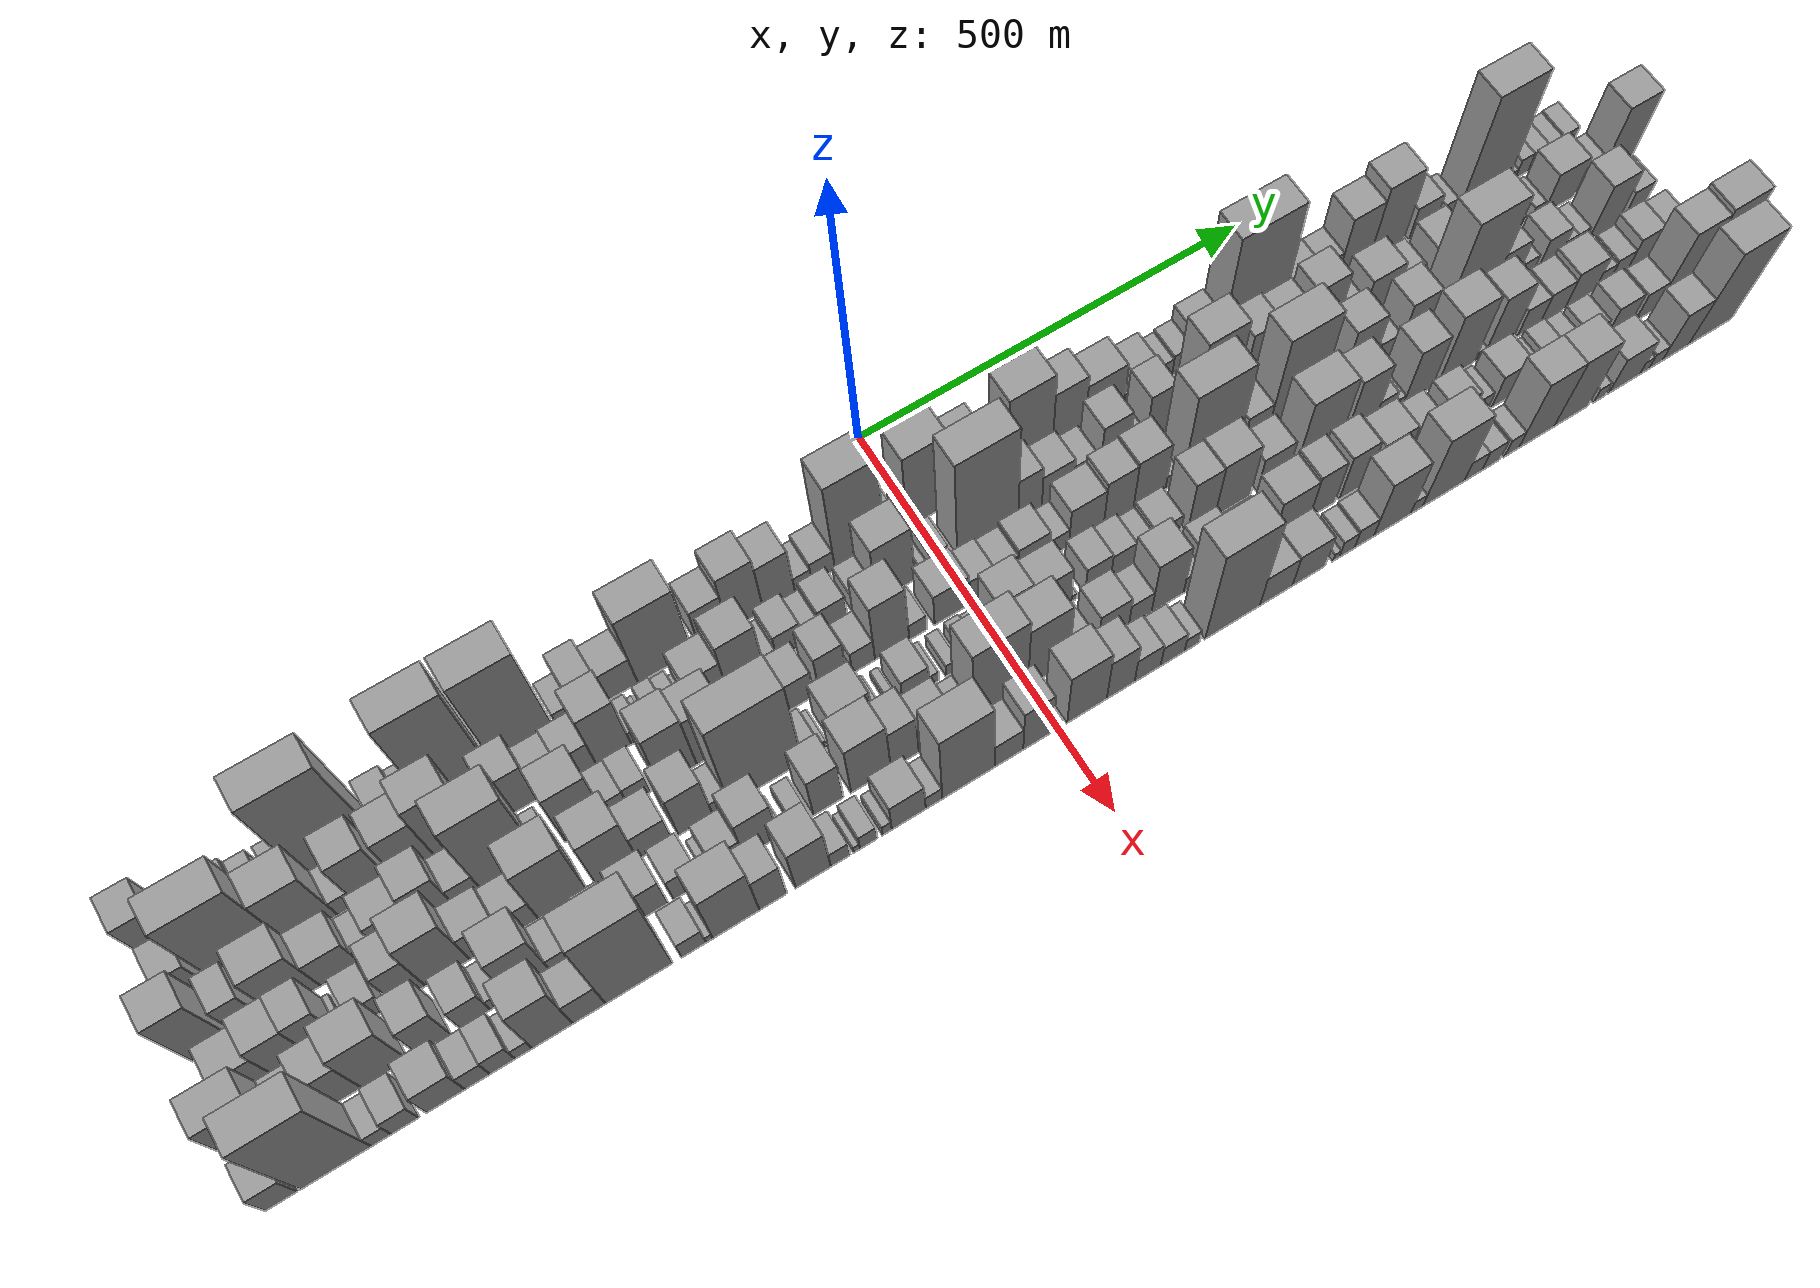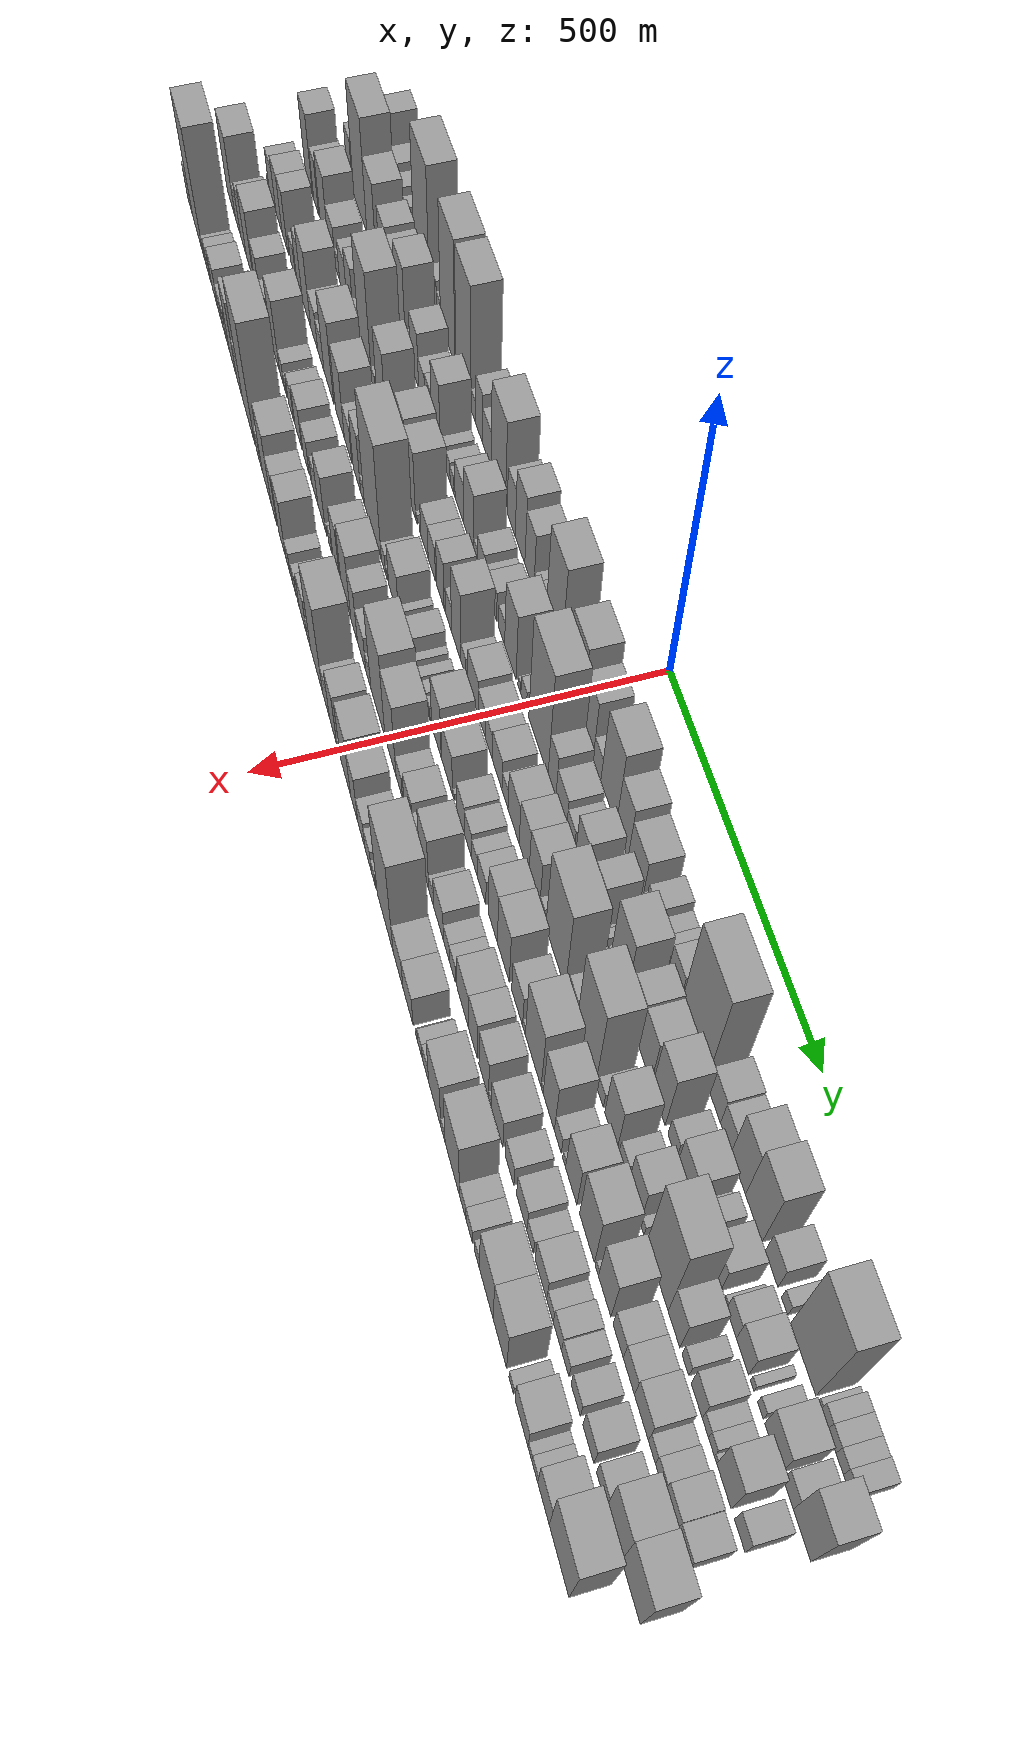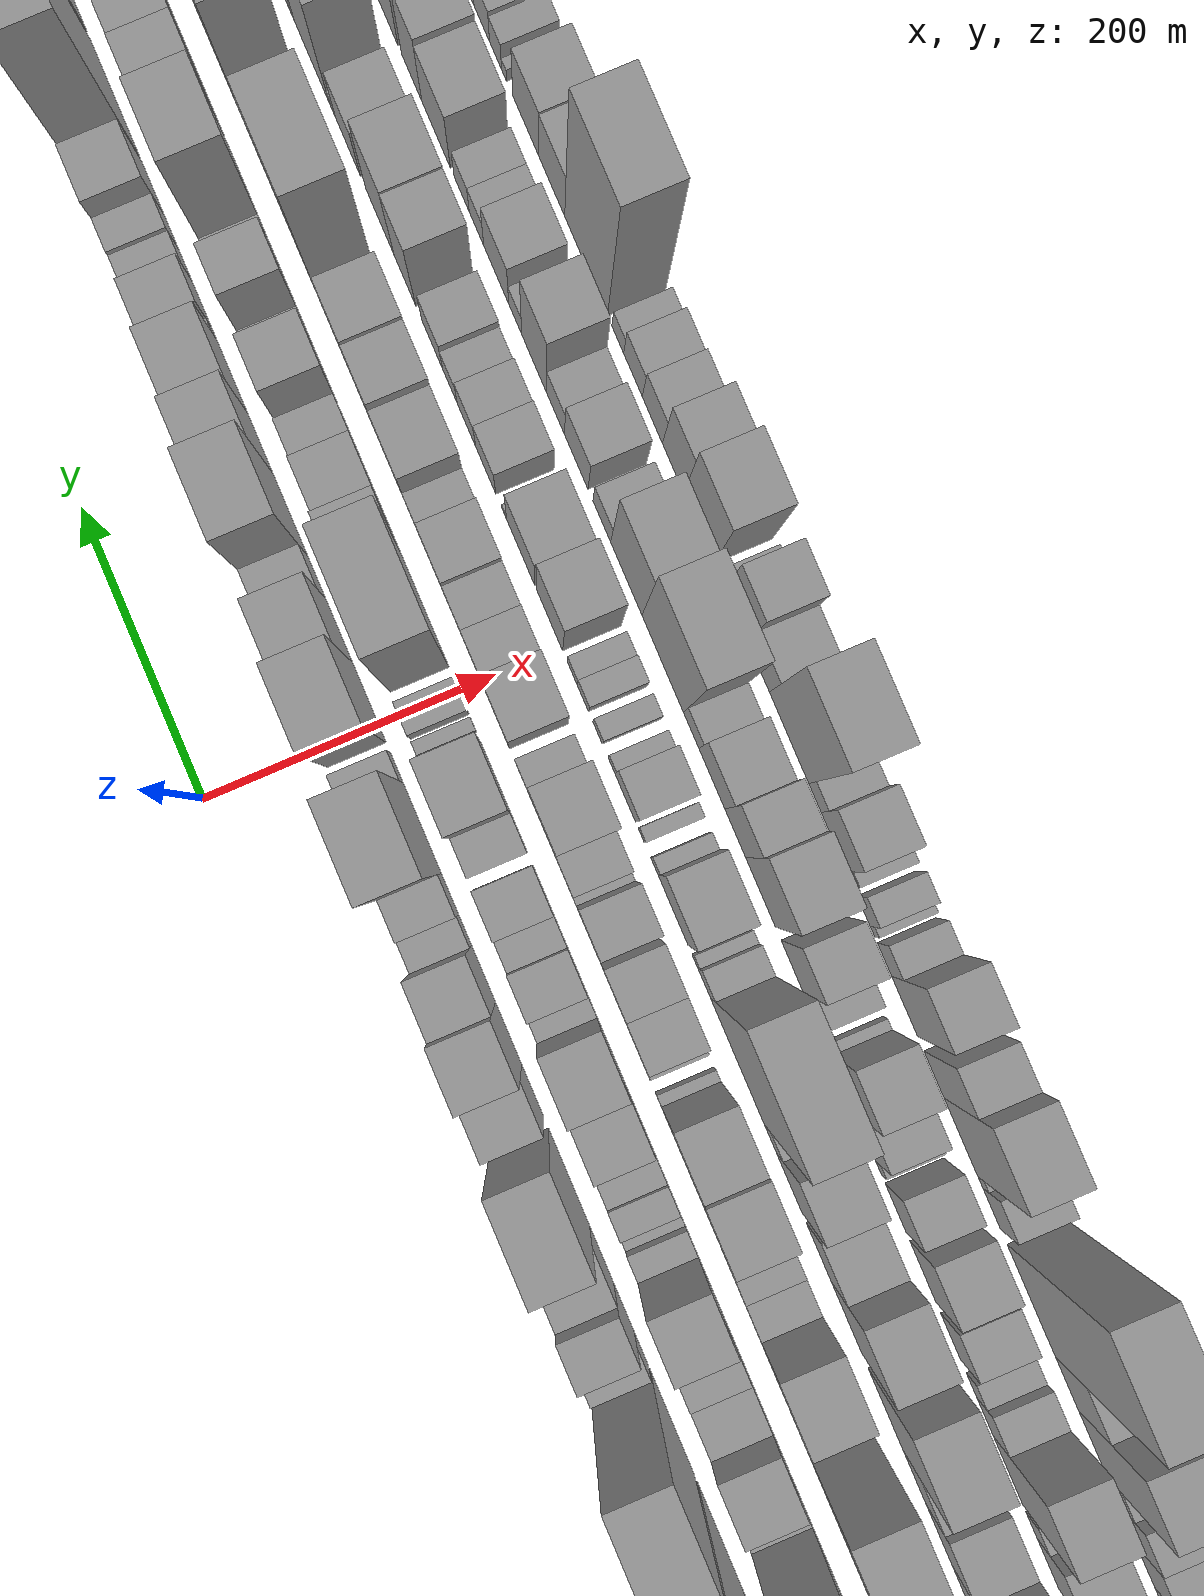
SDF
<sdf version="1.6">
 <world name="default">
  <scene>
   <sky><clouds><speed>12</speed></clouds></sky>
   <ambient>0.4 0.4 0.4 1</ambient>
   <background>0.7 0.7 0.7 1</background>
   <shadows>1</shadows>
  </scene>
  <gravity>0 0 -9.8066</gravity>
  <magnetic_field>6e-06 2.3e-05 -4.2e-05</magnetic_field>
  <physics default="0" name="default_physics" type="ode">
   <ode>
    <solver>
     <type>quick</type>
     <iters>10</iters>
     <sor>1.0</sor>
     <use_dynamic_moi_rescaling>0</use_dynamic_moi_rescaling>
    </solver>
    <constraints>
     <cfm>0</cfm>
     <erp>0.2</erp>
     <contact_max_correcting_vel>100</contact_max_correcting_vel>
     <contact_surface_layer>0.001</contact_surface_layer>
    </constraints>
   </ode>
   <max_step_size>0.004</max_step_size>
   <real_time_factor>1</real_time_factor>
   <real_time_update_rate>250</real_time_update_rate>
  </physics>
  <light name="sun" type="directional">
   <pose>0 0 10 0 0 0</pose>
   <diffuse>0.8 0.8 0.8 1</diffuse>
   <specular>0.2 0.2 0.2 1</specular>
   <attenuation>
    <range>1000</range>
    <constant>0.9</constant>
    <linear>0.01</linear>
    <quadratic>0.001</quadratic>
   </attenuation>
   <direction>-0.5 0.1 -0.9</direction>
  </light>
  <model name="building_1">
   <static>1</static>
   <pose>100.0000 -863.6245 0 0.000000 0.000000 0.000000</pose>
   <link name="link">
    <pose>0 0 60.00 0 0 0</pose>
    <collision name="collision"><geometry><box><size>40.0000 36.7511 120.0000</size></box></geometry></collision>
    <visual name="visual">
     <cast_shadows>0</cast_shadows>
     <geometry><box><size>40.0000 36.7511 120.0000</size></box></geometry>
     <material>
      <script>
       <uri>model://grey_wall/materials/scripts</uri>
       <uri>model://grey_wall/materials/textures</uri>
       <name>vrc/grey_wall</name>
      </script>
     </material>
    </visual>
   </link>
  </model>
  <model name="building_2">
   <static>1</static>
   <pose>100.0000 -823.6228 0 0.000000 0.000000 0.000000</pose>
   <link name="link">
    <pose>0 0 34.50 0 0 0</pose>
    <collision name="collision"><geometry><box><size>40.0000 35.2522 69.0000</size></box></geometry></collision>
    <visual name="visual">
     <cast_shadows>0</cast_shadows>
     <geometry><box><size>40.0000 35.2522 69.0000</size></box></geometry>
     <material>
      <script>
       <uri>model://grey_wall/materials/scripts</uri>
       <uri>model://grey_wall/materials/textures</uri>
       <name>vrc/grey_wall</name>
      </script>
     </material>
    </visual>
   </link>
  </model>
  <model name="building_3">
   <static>1</static>
   <pose>100.0000 -791.5884 0 0.000000 0.000000 0.000000</pose>
   <link name="link">
    <pose>0 0 27.00 0 0 0</pose>
    <collision name="collision"><geometry><box><size>40.0000 28.8167 54.0000</size></box></geometry></collision>
    <visual name="visual">
     <cast_shadows>0</cast_shadows>
     <geometry><box><size>40.0000 28.8167 54.0000</size></box></geometry>
     <material>
      <script>
       <uri>model://grey_wall/materials/scripts</uri>
       <uri>model://grey_wall/materials/textures</uri>
       <name>vrc/grey_wall</name>
      </script>
     </material>
    </visual>
   </link>
  </model>
  <model name="building_4">
   <static>1</static>
   <pose>100.0000 -765.5253 0 0.000000 0.000000 0.000000</pose>
   <link name="link">
    <pose>0 0 19.50 0 0 0</pose>
    <collision name="collision"><geometry><box><size>40.0000 23.3096 39.0000</size></box></geometry></collision>
    <visual name="visual">
     <cast_shadows>0</cast_shadows>
     <geometry><box><size>40.0000 23.3096 39.0000</size></box></geometry>
     <material>
      <script>
       <uri>model://grey_wall/materials/scripts</uri>
       <uri>model://grey_wall/materials/textures</uri>
       <name>vrc/grey_wall</name>
      </script>
     </material>
    </visual>
   </link>
  </model>
  <model name="building_5">
   <static>1</static>
   <pose>100.0000 -736.3220 0 0.000000 0.000000 0.000000</pose>
   <link name="link">
    <pose>0 0 18.00 0 0 0</pose>
    <collision name="collision"><geometry><box><size>40.0000 21.0969 36.0000</size></box></geometry></collision>
    <visual name="visual">
     <cast_shadows>0</cast_shadows>
     <geometry><box><size>40.0000 21.0969 36.0000</size></box></geometry>
     <material>
      <script>
       <uri>model://grey_wall/materials/scripts</uri>
       <uri>model://grey_wall/materials/textures</uri>
       <name>vrc/grey_wall</name>
      </script>
     </material>
    </visual>
   </link>
  </model>
  <model name="building_6">
   <static>1</static>
   <pose>100.0000 -679.9073 0 0.000000 0.000000 0.000000</pose>
   <link name="link">
    <pose>0 0 109.50 0 0 0</pose>
    <collision name="collision"><geometry><box><size>40.0000 79.7324 219.0000</size></box></geometry></collision>
    <visual name="visual">
     <cast_shadows>0</cast_shadows>
     <geometry><box><size>40.0000 79.7324 219.0000</size></box></geometry>
     <material>
      <script>
       <uri>model://grey_wall/materials/scripts</uri>
       <uri>model://grey_wall/materials/textures</uri>
       <name>vrc/grey_wall</name>
      </script>
     </material>
    </visual>
   </link>
  </model>
  <model name="building_7">
   <static>1</static>
   <pose>100.0000 -618.2458 0 0.000000 0.000000 0.000000</pose>
   <link name="link">
    <pose>0 0 28.50 0 0 0</pose>
    <collision name="collision"><geometry><box><size>40.0000 31.5905 57.0000</size></box></geometry></collision>
    <visual name="visual">
     <cast_shadows>0</cast_shadows>
     <geometry><box><size>40.0000 31.5905 57.0000</size></box></geometry>
     <material>
      <script>
       <uri>model://grey_wall/materials/scripts</uri>
       <uri>model://grey_wall/materials/textures</uri>
       <name>vrc/grey_wall</name>
      </script>
     </material>
    </visual>
   </link>
  </model>
  <model name="building_8">
   <static>1</static>
   <pose>100.0000 -592.3424 0 0.000000 0.000000 0.000000</pose>
   <link name="link">
    <pose>0 0 19.50 0 0 0</pose>
    <collision name="collision"><geometry><box><size>40.0000 20.2162 39.0000</size></box></geometry></collision>
    <visual name="visual">
     <cast_shadows>0</cast_shadows>
     <geometry><box><size>40.0000 20.2162 39.0000</size></box></geometry>
     <material>
      <script>
       <uri>model://grey_wall/materials/scripts</uri>
       <uri>model://grey_wall/materials/textures</uri>
       <name>vrc/grey_wall</name>
      </script>
     </material>
    </visual>
   </link>
  </model>
  <model name="building_9">
   <static>1</static>
   <pose>100.0000 -546.5553 0 0.000000 0.000000 0.000000</pose>
   <link name="link">
    <pose>0 0 111.00 0 0 0</pose>
    <collision name="collision"><geometry><box><size>40.0000 71.3579 222.0000</size></box></geometry></collision>
    <visual name="visual">
     <cast_shadows>0</cast_shadows>
     <geometry><box><size>40.0000 71.3579 222.0000</size></box></geometry>
     <material>
      <script>
       <uri>model://grey_wall/materials/scripts</uri>
       <uri>model://grey_wall/materials/textures</uri>
       <name>vrc/grey_wall</name>
      </script>
     </material>
    </visual>
   </link>
  </model>
  <model name="building_10">
   <static>1</static>
   <pose>100.0000 -470.8362 0 0.000000 0.000000 0.000000</pose>
   <link name="link">
    <pose>0 0 111.00 0 0 0</pose>
    <collision name="collision"><geometry><box><size>40.0000 70.0803 222.0000</size></box></geometry></collision>
    <visual name="visual">
     <cast_shadows>0</cast_shadows>
     <geometry><box><size>40.0000 70.0803 222.0000</size></box></geometry>
     <material>
      <script>
       <uri>model://grey_wall/materials/scripts</uri>
       <uri>model://grey_wall/materials/textures</uri>
       <name>vrc/grey_wall</name>
      </script>
     </material>
    </visual>
   </link>
  </model>
  <model name="building_11">
   <static>1</static>
   <pose>100.0000 -421.5764 0 0.000000 0.000000 0.000000</pose>
   <link name="link">
    <pose>0 0 21.00 0 0 0</pose>
    <collision name="collision"><geometry><box><size>40.0000 22.4394 42.0000</size></box></geometry></collision>
    <visual name="visual">
     <cast_shadows>0</cast_shadows>
     <geometry><box><size>40.0000 22.4394 42.0000</size></box></geometry>
     <material>
      <script>
       <uri>model://grey_wall/materials/scripts</uri>
       <uri>model://grey_wall/materials/textures</uri>
       <name>vrc/grey_wall</name>
      </script>
     </material>
    </visual>
   </link>
  </model>
  <model name="building_12">
   <static>1</static>
   <pose>100.0000 -394.1800 0 0.000000 0.000000 0.000000</pose>
   <link name="link">
    <pose>0 0 46.50 0 0 0</pose>
    <collision name="collision"><geometry><box><size>40.0000 32.3534 93.0000</size></box></geometry></collision>
    <visual name="visual">
     <cast_shadows>0</cast_shadows>
     <geometry><box><size>40.0000 32.3534 93.0000</size></box></geometry>
     <material>
      <script>
       <uri>model://grey_wall/materials/scripts</uri>
       <uri>model://grey_wall/materials/textures</uri>
       <name>vrc/grey_wall</name>
      </script>
     </material>
    </visual>
   </link>
  </model>
  <model name="building_13">
   <static>1</static>
   <pose>100.0000 -358.8857 0 0.000000 0.000000 0.000000</pose>
   <link name="link">
    <pose>0 0 34.50 0 0 0</pose>
    <collision name="collision"><geometry><box><size>40.0000 38.2353 69.0000</size></box></geometry></collision>
    <visual name="visual">
     <cast_shadows>0</cast_shadows>
     <geometry><box><size>40.0000 38.2353 69.0000</size></box></geometry>
     <material>
      <script>
       <uri>model://grey_wall/materials/scripts</uri>
       <uri>model://grey_wall/materials/textures</uri>
       <name>vrc/grey_wall</name>
      </script>
     </material>
    </visual>
   </link>
  </model>
  <model name="building_14">
   <static>1</static>
   <pose>100.0000 -307.2008 0 0.000000 0.000000 0.000000</pose>
   <link name="link">
    <pose>0 0 82.50 0 0 0</pose>
    <collision name="collision"><geometry><box><size>40.0000 65.1345 165.0000</size></box></geometry></collision>
    <visual name="visual">
     <cast_shadows>0</cast_shadows>
     <geometry><box><size>40.0000 65.1345 165.0000</size></box></geometry>
     <material>
      <script>
       <uri>model://grey_wall/materials/scripts</uri>
       <uri>model://grey_wall/materials/textures</uri>
       <name>vrc/grey_wall</name>
      </script>
     </material>
    </visual>
   </link>
  </model>
  <model name="building_15">
   <static>1</static>
   <pose>100.0000 -248.9841 0 0.000000 0.000000 0.000000</pose>
   <link name="link">
    <pose>0 0 46.50 0 0 0</pose>
    <collision name="collision"><geometry><box><size>40.0000 35.2989 93.0000</size></box></geometry></collision>
    <visual name="visual">
     <cast_shadows>0</cast_shadows>
     <geometry><box><size>40.0000 35.2989 93.0000</size></box></geometry>
     <material>
      <script>
       <uri>model://grey_wall/materials/scripts</uri>
       <uri>model://grey_wall/materials/textures</uri>
       <name>vrc/grey_wall</name>
      </script>
     </material>
    </visual>
   </link>
  </model>
  <model name="building_16">
   <static>1</static>
   <pose>100.0000 -210.3302 0 0.000000 0.000000 0.000000</pose>
   <link name="link">
    <pose>0 0 66.00 0 0 0</pose>
    <collision name="collision"><geometry><box><size>40.0000 42.0089 132.0000</size></box></geometry></collision>
    <visual name="visual">
     <cast_shadows>0</cast_shadows>
     <geometry><box><size>40.0000 42.0089 132.0000</size></box></geometry>
     <material>
      <script>
       <uri>model://grey_wall/materials/scripts</uri>
       <uri>model://grey_wall/materials/textures</uri>
       <name>vrc/grey_wall</name>
      </script>
     </material>
    </visual>
   </link>
  </model>
  <model name="building_17">
   <static>1</static>
   <pose>100.0000 -170.2096 0 0.000000 0.000000 0.000000</pose>
   <link name="link">
    <pose>0 0 54.00 0 0 0</pose>
    <collision name="collision"><geometry><box><size>40.0000 38.2323 108.0000</size></box></geometry></collision>
    <visual name="visual">
     <cast_shadows>0</cast_shadows>
     <geometry><box><size>40.0000 38.2323 108.0000</size></box></geometry>
     <material>
      <script>
       <uri>model://grey_wall/materials/scripts</uri>
       <uri>model://grey_wall/materials/textures</uri>
       <name>vrc/grey_wall</name>
      </script>
     </material>
    </visual>
   </link>
  </model>
  <model name="building_18">
   <static>1</static>
   <pose>100.0000 -140.6961 0 0.000000 0.000000 0.000000</pose>
   <link name="link">
    <pose>0 0 18.00 0 0 0</pose>
    <collision name="collision"><geometry><box><size>40.0000 20.7948 36.0000</size></box></geometry></collision>
    <visual name="visual">
     <cast_shadows>0</cast_shadows>
     <geometry><box><size>40.0000 20.7948 36.0000</size></box></geometry>
     <material>
      <script>
       <uri>model://grey_wall/materials/scripts</uri>
       <uri>model://grey_wall/materials/textures</uri>
       <name>vrc/grey_wall</name>
      </script>
     </material>
    </visual>
   </link>
  </model>
  <model name="building_19">
   <static>1</static>
   <pose>100.0000 -116.2024 0 0.000000 0.000000 0.000000</pose>
   <link name="link">
    <pose>0 0 24.00 0 0 0</pose>
    <collision name="collision"><geometry><box><size>40.0000 28.1926 48.0000</size></box></geometry></collision>
    <visual name="visual">
     <cast_shadows>0</cast_shadows>
     <geometry><box><size>40.0000 28.1926 48.0000</size></box></geometry>
     <material>
      <script>
       <uri>model://grey_wall/materials/scripts</uri>
       <uri>model://grey_wall/materials/textures</uri>
       <name>vrc/grey_wall</name>
      </script>
     </material>
    </visual>
   </link>
  </model>
  <model name="building_20">
   <static>1</static>
   <pose>100.0000 -70.9713 0 0.000000 0.000000 0.000000</pose>
   <link name="link">
    <pose>0 0 99.00 0 0 0</pose>
    <collision name="collision"><geometry><box><size>40.0000 62.2696 198.0000</size></box></geometry></collision>
    <visual name="visual">
     <cast_shadows>0</cast_shadows>
     <geometry><box><size>40.0000 62.2696 198.0000</size></box></geometry>
     <material>
      <script>
       <uri>model://grey_wall/materials/scripts</uri>
       <uri>model://grey_wall/materials/textures</uri>
       <name>vrc/grey_wall</name>
      </script>
     </material>
    </visual>
   </link>
  </model>
  <model name="building_21">
   <static>1</static>
   <pose>100.0000 -29.6913 0 0.000000 0.000000 0.000000</pose>
   <link name="link">
    <pose>0 0 18.00 0 0 0</pose>
    <collision name="collision"><geometry><box><size>40.0000 20.2905 36.0000</size></box></geometry></collision>
    <visual name="visual">
     <cast_shadows>0</cast_shadows>
     <geometry><box><size>40.0000 20.2905 36.0000</size></box></geometry>
     <material>
      <script>
       <uri>model://grey_wall/materials/scripts</uri>
       <uri>model://grey_wall/materials/textures</uri>
       <name>vrc/grey_wall</name>
      </script>
     </material>
    </visual>
   </link>
  </model>
  <model name="building_22">
   <static>1</static>
   <pose>100.0000 15.0031 0 0.000000 0.000000 0.000000</pose>
   <link name="link">
    <pose>0 0 82.50 0 0 0</pose>
    <collision name="collision"><geometry><box><size>40.0000 55.0982 165.0000</size></box></geometry></collision>
    <visual name="visual">
     <cast_shadows>0</cast_shadows>
     <geometry><box><size>40.0000 55.0982 165.0000</size></box></geometry>
     <material>
      <script>
       <uri>model://grey_wall/materials/scripts</uri>
       <uri>model://grey_wall/materials/textures</uri>
       <name>vrc/grey_wall</name>
      </script>
     </material>
    </visual>
   </link>
  </model>
  <model name="building_23">
   <static>1</static>
   <pose>100.0000 64.5372 0 0.000000 0.000000 0.000000</pose>
   <link name="link">
    <pose>0 0 61.50 0 0 0</pose>
    <collision name="collision"><geometry><box><size>40.0000 43.9700 123.0000</size></box></geometry></collision>
    <visual name="visual">
     <cast_shadows>0</cast_shadows>
     <geometry><box><size>40.0000 43.9700 123.0000</size></box></geometry>
     <material>
      <script>
       <uri>model://grey_wall/materials/scripts</uri>
       <uri>model://grey_wall/materials/textures</uri>
       <name>vrc/grey_wall</name>
      </script>
     </material>
    </visual>
   </link>
  </model>
  <model name="building_24">
   <static>1</static>
   <pose>100.0000 101.1904 0 0.000000 0.000000 0.000000</pose>
   <link name="link">
    <pose>0 0 25.50 0 0 0</pose>
    <collision name="collision"><geometry><box><size>40.0000 29.3365 51.0000</size></box></geometry></collision>
    <visual name="visual">
     <cast_shadows>0</cast_shadows>
     <geometry><box><size>40.0000 29.3365 51.0000</size></box></geometry>
     <material>
      <script>
       <uri>model://grey_wall/materials/scripts</uri>
       <uri>model://grey_wall/materials/textures</uri>
       <name>vrc/grey_wall</name>
      </script>
     </material>
    </visual>
   </link>
  </model>
  <model name="building_25">
   <static>1</static>
   <pose>100.0000 144.4242 0 0.000000 0.000000 0.000000</pose>
   <link name="link">
    <pose>0 0 79.50 0 0 0</pose>
    <collision name="collision"><geometry><box><size>40.0000 57.1311 159.0000</size></box></geometry></collision>
    <visual name="visual">
     <cast_shadows>0</cast_shadows>
     <geometry><box><size>40.0000 57.1311 159.0000</size></box></geometry>
     <material>
      <script>
       <uri>model://grey_wall/materials/scripts</uri>
       <uri>model://grey_wall/materials/textures</uri>
       <name>vrc/grey_wall</name>
      </script>
     </material>
    </visual>
   </link>
  </model>
  <model name="building_26">
   <static>1</static>
   <pose>100.0000 194.0996 0 0.000000 0.000000 0.000000</pose>
   <link name="link">
    <pose>0 0 57.00 0 0 0</pose>
    <collision name="collision"><geometry><box><size>40.0000 42.2197 114.0000</size></box></geometry></collision>
    <visual name="visual">
     <cast_shadows>0</cast_shadows>
     <geometry><box><size>40.0000 42.2197 114.0000</size></box></geometry>
     <material>
      <script>
       <uri>model://grey_wall/materials/scripts</uri>
       <uri>model://grey_wall/materials/textures</uri>
       <name>vrc/grey_wall</name>
      </script>
     </material>
    </visual>
   </link>
  </model>
  <model name="building_27">
   <static>1</static>
   <pose>100.0000 240.7146 0 0.000000 0.000000 0.000000</pose>
   <link name="link">
    <pose>0 0 45.00 0 0 0</pose>
    <collision name="collision"><geometry><box><size>40.0000 51.0102 90.0000</size></box></geometry></collision>
    <visual name="visual">
     <cast_shadows>0</cast_shadows>
     <geometry><box><size>40.0000 51.0102 90.0000</size></box></geometry>
     <material>
      <script>
       <uri>model://grey_wall/materials/scripts</uri>
       <uri>model://grey_wall/materials/textures</uri>
       <name>vrc/grey_wall</name>
      </script>
     </material>
    </visual>
   </link>
  </model>
  <model name="building_28">
   <static>1</static>
   <pose>100.0000 270.7836 0 0.000000 0.000000 0.000000</pose>
   <link name="link">
    <pose>0 0 10.50 0 0 0</pose>
    <collision name="collision"><geometry><box><size>40.0000 9.1279 21.0000</size></box></geometry></collision>
    <visual name="visual">
     <cast_shadows>0</cast_shadows>
     <geometry><box><size>40.0000 9.1279 21.0000</size></box></geometry>
     <material>
      <script>
       <uri>model://grey_wall/materials/scripts</uri>
       <uri>model://grey_wall/materials/textures</uri>
       <name>vrc/grey_wall</name>
      </script>
     </material>
    </visual>
   </link>
  </model>
  <model name="building_29">
   <static>1</static>
   <pose>100.0000 291.2869 0 0.000000 0.000000 0.000000</pose>
   <link name="link">
    <pose>0 0 30.00 0 0 0</pose>
    <collision name="collision"><geometry><box><size>40.0000 31.8785 60.0000</size></box></geometry></collision>
    <visual name="visual">
     <cast_shadows>0</cast_shadows>
     <geometry><box><size>40.0000 31.8785 60.0000</size></box></geometry>
     <material>
      <script>
       <uri>model://grey_wall/materials/scripts</uri>
       <uri>model://grey_wall/materials/textures</uri>
       <name>vrc/grey_wall</name>
      </script>
     </material>
    </visual>
   </link>
  </model>
  <model name="building_30">
   <static>1</static>
   <pose>100.0000 318.4510 0 0.000000 0.000000 0.000000</pose>
   <link name="link">
    <pose>0 0 19.50 0 0 0</pose>
    <collision name="collision"><geometry><box><size>40.0000 22.4497 39.0000</size></box></geometry></collision>
    <visual name="visual">
     <cast_shadows>0</cast_shadows>
     <geometry><box><size>40.0000 22.4497 39.0000</size></box></geometry>
     <material>
      <script>
       <uri>model://grey_wall/materials/scripts</uri>
       <uri>model://grey_wall/materials/textures</uri>
       <name>vrc/grey_wall</name>
      </script>
     </material>
    </visual>
   </link>
  </model>
  <model name="building_31">
   <static>1</static>
   <pose>100.0000 341.3287 0 0.000000 0.000000 0.000000</pose>
   <link name="link">
    <pose>0 0 22.50 0 0 0</pose>
    <collision name="collision"><geometry><box><size>40.0000 23.3058 45.0000</size></box></geometry></collision>
    <visual name="visual">
     <cast_shadows>0</cast_shadows>
     <geometry><box><size>40.0000 23.3058 45.0000</size></box></geometry>
     <material>
      <script>
       <uri>model://grey_wall/materials/scripts</uri>
       <uri>model://grey_wall/materials/textures</uri>
       <name>vrc/grey_wall</name>
      </script>
     </material>
    </visual>
   </link>
  </model>
  <model name="building_32">
   <static>1</static>
   <pose>100.0000 372.1104 0 0.000000 0.000000 0.000000</pose>
   <link name="link">
    <pose>0 0 37.50 0 0 0</pose>
    <collision name="collision"><geometry><box><size>40.0000 38.2575 75.0000</size></box></geometry></collision>
    <visual name="visual">
     <cast_shadows>0</cast_shadows>
     <geometry><box><size>40.0000 38.2575 75.0000</size></box></geometry>
     <material>
      <script>
       <uri>model://grey_wall/materials/scripts</uri>
       <uri>model://grey_wall/materials/textures</uri>
       <name>vrc/grey_wall</name>
      </script>
     </material>
    </visual>
   </link>
  </model>
  <model name="building_33">
   <static>1</static>
   <pose>100.0000 435.8190 0 0.000000 0.000000 0.000000</pose>
   <link name="link">
    <pose>0 0 112.50 0 0 0</pose>
    <collision name="collision"><geometry><box><size>40.0000 83.1598 225.0000</size></box></geometry></collision>
    <visual name="visual">
     <cast_shadows>0</cast_shadows>
     <geometry><box><size>40.0000 83.1598 225.0000</size></box></geometry>
     <material>
      <script>
       <uri>model://grey_wall/materials/scripts</uri>
       <uri>model://grey_wall/materials/textures</uri>
       <name>vrc/grey_wall</name>
      </script>
     </material>
    </visual>
   </link>
  </model>
  <model name="building_34">
   <static>1</static>
   <pose>100.0000 502.7653 0 0.000000 0.000000 0.000000</pose>
   <link name="link">
    <pose>0 0 33.00 0 0 0</pose>
    <collision name="collision"><geometry><box><size>40.0000 38.7329 66.0000</size></box></geometry></collision>
    <visual name="visual">
     <cast_shadows>0</cast_shadows>
     <geometry><box><size>40.0000 38.7329 66.0000</size></box></geometry>
     <material>
      <script>
       <uri>model://grey_wall/materials/scripts</uri>
       <uri>model://grey_wall/materials/textures</uri>
       <name>vrc/grey_wall</name>
      </script>
     </material>
    </visual>
   </link>
  </model>
  <model name="building_35">
   <static>1</static>
   <pose>100.0000 538.1720 0 0.000000 0.000000 0.000000</pose>
   <link name="link">
    <pose>0 0 30.00 0 0 0</pose>
    <collision name="collision"><geometry><box><size>40.0000 32.0804 60.0000</size></box></geometry></collision>
    <visual name="visual">
     <cast_shadows>0</cast_shadows>
     <geometry><box><size>40.0000 32.0804 60.0000</size></box></geometry>
     <material>
      <script>
       <uri>model://grey_wall/materials/scripts</uri>
       <uri>model://grey_wall/materials/textures</uri>
       <name>vrc/grey_wall</name>
      </script>
     </material>
    </visual>
   </link>
  </model>
  <model name="building_36">
   <static>1</static>
   <pose>100.0000 575.8749 0 0.000000 0.000000 0.000000</pose>
   <link name="link">
    <pose>0 0 63.00 0 0 0</pose>
    <collision name="collision"><geometry><box><size>40.0000 43.3255 126.0000</size></box></geometry></collision>
    <visual name="visual">
     <cast_shadows>0</cast_shadows>
     <geometry><box><size>40.0000 43.3255 126.0000</size></box></geometry>
     <material>
      <script>
       <uri>model://grey_wall/materials/scripts</uri>
       <uri>model://grey_wall/materials/textures</uri>
       <name>vrc/grey_wall</name>
      </script>
     </material>
    </visual>
   </link>
  </model>
  <model name="building_37">
   <static>1</static>
   <pose>100.0000 621.8524 0 0.000000 0.000000 0.000000</pose>
   <link name="link">
    <pose>0 0 75.00 0 0 0</pose>
    <collision name="collision"><geometry><box><size>40.0000 48.6295 150.0000</size></box></geometry></collision>
    <visual name="visual">
     <cast_shadows>0</cast_shadows>
     <geometry><box><size>40.0000 48.6295 150.0000</size></box></geometry>
     <material>
      <script>
       <uri>model://grey_wall/materials/scripts</uri>
       <uri>model://grey_wall/materials/textures</uri>
       <name>vrc/grey_wall</name>
      </script>
     </material>
    </visual>
   </link>
  </model>
  <model name="building_38">
   <static>1</static>
   <pose>100.0000 673.1736 0 0.000000 0.000000 0.000000</pose>
   <link name="link">
    <pose>0 0 31.50 0 0 0</pose>
    <collision name="collision"><geometry><box><size>40.0000 36.0130 63.0000</size></box></geometry></collision>
    <visual name="visual">
     <cast_shadows>0</cast_shadows>
     <geometry><box><size>40.0000 36.0130 63.0000</size></box></geometry>
     <material>
      <script>
       <uri>model://grey_wall/materials/scripts</uri>
       <uri>model://grey_wall/materials/textures</uri>
       <name>vrc/grey_wall</name>
      </script>
     </material>
    </visual>
   </link>
  </model>
  <model name="building_39">
   <static>1</static>
   <pose>100.0000 709.8207 0 0.000000 0.000000 0.000000</pose>
   <link name="link">
    <pose>0 0 16.50 0 0 0</pose>
    <collision name="collision"><geometry><box><size>40.0000 17.2811 33.0000</size></box></geometry></collision>
    <visual name="visual">
     <cast_shadows>0</cast_shadows>
     <geometry><box><size>40.0000 17.2811 33.0000</size></box></geometry>
     <material>
      <script>
       <uri>model://grey_wall/materials/scripts</uri>
       <uri>model://grey_wall/materials/textures</uri>
       <name>vrc/grey_wall</name>
      </script>
     </material>
    </visual>
   </link>
  </model>
  <model name="building_40">
   <static>1</static>
   <pose>100.0000 760.8265 0 0.000000 0.000000 0.000000</pose>
   <link name="link">
    <pose>0 0 108.00 0 0 0</pose>
    <collision name="collision"><geometry><box><size>40.0000 68.7305 216.0000</size></box></geometry></collision>
    <visual name="visual">
     <cast_shadows>0</cast_shadows>
     <geometry><box><size>40.0000 68.7305 216.0000</size></box></geometry>
     <material>
      <script>
       <uri>model://grey_wall/materials/scripts</uri>
       <uri>model://grey_wall/materials/textures</uri>
       <name>vrc/grey_wall</name>
      </script>
     </material>
    </visual>
   </link>
  </model>
  <model name="building_41">
   <static>1</static>
   <pose>100.0000 803.9687 0 0.000000 0.000000 0.000000</pose>
   <link name="link">
    <pose>0 0 9.00 0 0 0</pose>
    <collision name="collision"><geometry><box><size>40.0000 7.5538 18.0000</size></box></geometry></collision>
    <visual name="visual">
     <cast_shadows>0</cast_shadows>
     <geometry><box><size>40.0000 7.5538 18.0000</size></box></geometry>
     <material>
      <script>
       <uri>model://grey_wall/materials/scripts</uri>
       <uri>model://grey_wall/materials/textures</uri>
       <name>vrc/grey_wall</name>
      </script>
     </material>
    </visual>
   </link>
  </model>
  <model name="building_42">
   <static>1</static>
   <pose>100.0000 817.0140 0 0.000000 0.000000 0.000000</pose>
   <link name="link">
    <pose>0 0 18.00 0 0 0</pose>
    <collision name="collision"><geometry><box><size>40.0000 18.5368 36.0000</size></box></geometry></collision>
    <visual name="visual">
     <cast_shadows>0</cast_shadows>
     <geometry><box><size>40.0000 18.5368 36.0000</size></box></geometry>
     <material>
      <script>
       <uri>model://grey_wall/materials/scripts</uri>
       <uri>model://grey_wall/materials/textures</uri>
       <name>vrc/grey_wall</name>
      </script>
     </material>
    </visual>
   </link>
  </model>
  <model name="building_43">
   <static>1</static>
   <pose>100.0000 837.0378 0 0.000000 0.000000 0.000000</pose>
   <link name="link">
    <pose>0 0 18.00 0 0 0</pose>
    <collision name="collision"><geometry><box><size>40.0000 21.5109 36.0000</size></box></geometry></collision>
    <visual name="visual">
     <cast_shadows>0</cast_shadows>
     <geometry><box><size>40.0000 21.5109 36.0000</size></box></geometry>
     <material>
      <script>
       <uri>model://grey_wall/materials/scripts</uri>
       <uri>model://grey_wall/materials/textures</uri>
       <name>vrc/grey_wall</name>
      </script>
     </material>
    </visual>
   </link>
  </model>
  <model name="building_44">
   <static>1</static>
   <pose>100.0000 857.4511 0 0.000000 0.000000 0.000000</pose>
   <link name="link">
    <pose>0 0 18.00 0 0 0</pose>
    <collision name="collision"><geometry><box><size>40.0000 19.3156 36.0000</size></box></geometry></collision>
    <visual name="visual">
     <cast_shadows>0</cast_shadows>
     <geometry><box><size>40.0000 19.3156 36.0000</size></box></geometry>
     <material>
      <script>
       <uri>model://grey_wall/materials/scripts</uri>
       <uri>model://grey_wall/materials/textures</uri>
       <name>vrc/grey_wall</name>
      </script>
     </material>
    </visual>
   </link>
  </model>
  <model name="building_45">
   <static>1</static>
   <pose>100.0000 878.6003 0 0.000000 0.000000 0.000000</pose>
   <link name="link">
    <pose>0 0 19.50 0 0 0</pose>
    <collision name="collision"><geometry><box><size>40.0000 22.9828 39.0000</size></box></geometry></collision>
    <visual name="visual">
     <cast_shadows>0</cast_shadows>
     <geometry><box><size>40.0000 22.9828 39.0000</size></box></geometry>
     <material>
      <script>
       <uri>model://grey_wall/materials/scripts</uri>
       <uri>model://grey_wall/materials/textures</uri>
       <name>vrc/grey_wall</name>
      </script>
     </material>
    </visual>
   </link>
  </model>
  <model name="building_46">
   <static>1</static>
   <pose>155.0000 -881.8193 0 0.000000 0.000000 0.000000</pose>
   <link name="link">
    <pose>0 0 7.50 0 0 0</pose>
    <collision name="collision"><geometry><box><size>40.0000 6.3614 15.0000</size></box></geometry></collision>
    <visual name="visual">
     <cast_shadows>0</cast_shadows>
     <geometry><box><size>40.0000 6.3614 15.0000</size></box></geometry>
     <material>
      <script>
       <uri>model://grey_wall/materials/scripts</uri>
       <uri>model://grey_wall/materials/textures</uri>
       <name>vrc/grey_wall</name>
      </script>
     </material>
    </visual>
   </link>
  </model>
  <model name="building_47">
   <static>1</static>
   <pose>155.0000 -858.5176 0 0.000000 0.000000 0.000000</pose>
   <link name="link">
    <pose>0 0 46.50 0 0 0</pose>
    <collision name="collision"><geometry><box><size>40.0000 32.2419 93.0000</size></box></geometry></collision>
    <visual name="visual">
     <cast_shadows>0</cast_shadows>
     <geometry><box><size>40.0000 32.2419 93.0000</size></box></geometry>
     <material>
      <script>
       <uri>model://grey_wall/materials/scripts</uri>
       <uri>model://grey_wall/materials/textures</uri>
       <name>vrc/grey_wall</name>
      </script>
     </material>
    </visual>
   </link>
  </model>
  <model name="building_48">
   <static>1</static>
   <pose>155.0000 -798.1355 0 0.000000 0.000000 0.000000</pose>
   <link name="link">
    <pose>0 0 100.50 0 0 0</pose>
    <collision name="collision"><geometry><box><size>40.0000 74.5224 201.0000</size></box></geometry></collision>
    <visual name="visual">
     <cast_shadows>0</cast_shadows>
     <geometry><box><size>40.0000 74.5224 201.0000</size></box></geometry>
     <material>
      <script>
       <uri>model://grey_wall/materials/scripts</uri>
       <uri>model://grey_wall/materials/textures</uri>
       <name>vrc/grey_wall</name>
      </script>
     </material>
    </visual>
   </link>
  </model>
  <model name="building_49">
   <static>1</static>
   <pose>155.0000 -734.7934 0 0.000000 0.000000 0.000000</pose>
   <link name="link">
    <pose>0 0 69.00 0 0 0</pose>
    <collision name="collision"><geometry><box><size>40.0000 52.1619 138.0000</size></box></geometry></collision>
    <visual name="visual">
     <cast_shadows>0</cast_shadows>
     <geometry><box><size>40.0000 52.1619 138.0000</size></box></geometry>
     <material>
      <script>
       <uri>model://grey_wall/materials/scripts</uri>
       <uri>model://grey_wall/materials/textures</uri>
       <name>vrc/grey_wall</name>
      </script>
     </material>
    </visual>
   </link>
  </model>
  <model name="building_50">
   <static>1</static>
   <pose>155.0000 -698.1956 0 0.000000 0.000000 0.000000</pose>
   <link name="link">
    <pose>0 0 21.00 0 0 0</pose>
    <collision name="collision"><geometry><box><size>40.0000 21.0338 42.0000</size></box></geometry></collision>
    <visual name="visual">
     <cast_shadows>0</cast_shadows>
     <geometry><box><size>40.0000 21.0338 42.0000</size></box></geometry>
     <material>
      <script>
       <uri>model://grey_wall/materials/scripts</uri>
       <uri>model://grey_wall/materials/textures</uri>
       <name>vrc/grey_wall</name>
      </script>
     </material>
    </visual>
   </link>
  </model>
  <model name="building_51">
   <static>1</static>
   <pose>155.0000 -667.2379 0 0.000000 0.000000 0.000000</pose>
   <link name="link">
    <pose>0 0 61.50 0 0 0</pose>
    <collision name="collision"><geometry><box><size>40.0000 40.8817 123.0000</size></box></geometry></collision>
    <visual name="visual">
     <cast_shadows>0</cast_shadows>
     <geometry><box><size>40.0000 40.8817 123.0000</size></box></geometry>
     <material>
      <script>
       <uri>model://grey_wall/materials/scripts</uri>
       <uri>model://grey_wall/materials/textures</uri>
       <name>vrc/grey_wall</name>
      </script>
     </material>
    </visual>
   </link>
  </model>
  <model name="building_52">
   <static>1</static>
   <pose>155.0000 -620.8911 0 0.000000 0.000000 0.000000</pose>
   <link name="link">
    <pose>0 0 58.50 0 0 0</pose>
    <collision name="collision"><geometry><box><size>40.0000 41.8119 117.0000</size></box></geometry></collision>
    <visual name="visual">
     <cast_shadows>0</cast_shadows>
     <geometry><box><size>40.0000 41.8119 117.0000</size></box></geometry>
     <material>
      <script>
       <uri>model://grey_wall/materials/scripts</uri>
       <uri>model://grey_wall/materials/textures</uri>
       <name>vrc/grey_wall</name>
      </script>
     </material>
    </visual>
   </link>
  </model>
  <model name="building_53">
   <static>1</static>
   <pose>155.0000 -575.1969 0 0.000000 0.000000 0.000000</pose>
   <link name="link">
    <pose>0 0 75.00 0 0 0</pose>
    <collision name="collision"><geometry><box><size>40.0000 49.5766 150.0000</size></box></geometry></collision>
    <visual name="visual">
     <cast_shadows>0</cast_shadows>
     <geometry><box><size>40.0000 49.5766 150.0000</size></box></geometry>
     <material>
      <script>
       <uri>model://grey_wall/materials/scripts</uri>
       <uri>model://grey_wall/materials/textures</uri>
       <name>vrc/grey_wall</name>
      </script>
     </material>
    </visual>
   </link>
  </model>
  <model name="building_54">
   <static>1</static>
   <pose>155.0000 -539.7854 0 0.000000 0.000000 0.000000</pose>
   <link name="link">
    <pose>0 0 19.50 0 0 0</pose>
    <collision name="collision"><geometry><box><size>40.0000 21.2463 39.0000</size></box></geometry></collision>
    <visual name="visual">
     <cast_shadows>0</cast_shadows>
     <geometry><box><size>40.0000 21.2463 39.0000</size></box></geometry>
     <material>
      <script>
       <uri>model://grey_wall/materials/scripts</uri>
       <uri>model://grey_wall/materials/textures</uri>
       <name>vrc/grey_wall</name>
      </script>
     </material>
    </visual>
   </link>
  </model>
  <model name="building_55">
   <static>1</static>
   <pose>155.0000 -504.7969 0 0.000000 0.000000 0.000000</pose>
   <link name="link">
    <pose>0 0 51.00 0 0 0</pose>
    <collision name="collision"><geometry><box><size>40.0000 40.7308 102.0000</size></box></geometry></collision>
    <visual name="visual">
     <cast_shadows>0</cast_shadows>
     <geometry><box><size>40.0000 40.7308 102.0000</size></box></geometry>
     <material>
      <script>
       <uri>model://grey_wall/materials/scripts</uri>
       <uri>model://grey_wall/materials/textures</uri>
       <name>vrc/grey_wall</name>
      </script>
     </material>
    </visual>
   </link>
  </model>
  <model name="building_56">
   <static>1</static>
   <pose>155.0000 -468.3659 0 0.000000 0.000000 0.000000</pose>
   <link name="link">
    <pose>0 0 30.00 0 0 0</pose>
    <collision name="collision"><geometry><box><size>40.0000 32.1312 60.0000</size></box></geometry></collision>
    <visual name="visual">
     <cast_shadows>0</cast_shadows>
     <geometry><box><size>40.0000 32.1312 60.0000</size></box></geometry>
     <material>
      <script>
       <uri>model://grey_wall/materials/scripts</uri>
       <uri>model://grey_wall/materials/textures</uri>
       <name>vrc/grey_wall</name>
      </script>
     </material>
    </visual>
   </link>
  </model>
  <model name="building_57">
   <static>1</static>
   <pose>155.0000 -435.2672 0 0.000000 0.000000 0.000000</pose>
   <link name="link">
    <pose>0 0 33.00 0 0 0</pose>
    <collision name="collision"><geometry><box><size>40.0000 34.0661 66.0000</size></box></geometry></collision>
    <visual name="visual">
     <cast_shadows>0</cast_shadows>
     <geometry><box><size>40.0000 34.0661 66.0000</size></box></geometry>
     <material>
      <script>
       <uri>model://grey_wall/materials/scripts</uri>
       <uri>model://grey_wall/materials/textures</uri>
       <name>vrc/grey_wall</name>
      </script>
     </material>
    </visual>
   </link>
  </model>
  <model name="building_58">
   <static>1</static>
   <pose>155.0000 -397.9051 0 0.000000 0.000000 0.000000</pose>
   <link name="link">
    <pose>0 0 64.50 0 0 0</pose>
    <collision name="collision"><geometry><box><size>40.0000 40.6582 129.0000</size></box></geometry></collision>
    <visual name="visual">
     <cast_shadows>0</cast_shadows>
     <geometry><box><size>40.0000 40.6582 129.0000</size></box></geometry>
     <material>
      <script>
       <uri>model://grey_wall/materials/scripts</uri>
       <uri>model://grey_wall/materials/textures</uri>
       <name>vrc/grey_wall</name>
      </script>
     </material>
    </visual>
   </link>
  </model>
  <model name="building_59">
   <static>1</static>
   <pose>155.0000 -368.8836 0 0.000000 0.000000 0.000000</pose>
   <link name="link">
    <pose>0 0 16.50 0 0 0</pose>
    <collision name="collision"><geometry><box><size>40.0000 17.3847 33.0000</size></box></geometry></collision>
    <visual name="visual">
     <cast_shadows>0</cast_shadows>
     <geometry><box><size>40.0000 17.3847 33.0000</size></box></geometry>
     <material>
      <script>
       <uri>model://grey_wall/materials/scripts</uri>
       <uri>model://grey_wall/materials/textures</uri>
       <name>vrc/grey_wall</name>
      </script>
     </material>
    </visual>
   </link>
  </model>
  <model name="building_60">
   <static>1</static>
   <pose>155.0000 -356.5489 0 0.000000 0.000000 0.000000</pose>
   <link name="link">
    <pose>0 0 9.00 0 0 0</pose>
    <collision name="collision"><geometry><box><size>40.0000 7.2847 18.0000</size></box></geometry></collision>
    <visual name="visual">
     <cast_shadows>0</cast_shadows>
     <geometry><box><size>40.0000 7.2847 18.0000</size></box></geometry>
     <material>
      <script>
       <uri>model://grey_wall/materials/scripts</uri>
       <uri>model://grey_wall/materials/textures</uri>
       <name>vrc/grey_wall</name>
      </script>
     </material>
    </visual>
   </link>
  </model>
  <model name="building_61">
   <static>1</static>
   <pose>155.0000 -340.0556 0 0.000000 0.000000 0.000000</pose>
   <link name="link">
    <pose>0 0 19.50 0 0 0</pose>
    <collision name="collision"><geometry><box><size>40.0000 19.7020 39.0000</size></box></geometry></collision>
    <visual name="visual">
     <cast_shadows>0</cast_shadows>
     <geometry><box><size>40.0000 19.7020 39.0000</size></box></geometry>
     <material>
      <script>
       <uri>model://grey_wall/materials/scripts</uri>
       <uri>model://grey_wall/materials/textures</uri>
       <name>vrc/grey_wall</name>
      </script>
     </material>
    </visual>
   </link>
  </model>
  <model name="building_62">
   <static>1</static>
   <pose>155.0000 -321.5133 0 0.000000 0.000000 0.000000</pose>
   <link name="link">
    <pose>0 0 16.50 0 0 0</pose>
    <collision name="collision"><geometry><box><size>40.0000 17.3825 33.0000</size></box></geometry></collision>
    <visual name="visual">
     <cast_shadows>0</cast_shadows>
     <geometry><box><size>40.0000 17.3825 33.0000</size></box></geometry>
     <material>
      <script>
       <uri>model://grey_wall/materials/scripts</uri>
       <uri>model://grey_wall/materials/textures</uri>
       <name>vrc/grey_wall</name>
      </script>
     </material>
    </visual>
   </link>
  </model>
  <model name="building_63">
   <static>1</static>
   <pose>155.0000 -309.8123 0 0.000000 0.000000 0.000000</pose>
   <link name="link">
    <pose>0 0 7.50 0 0 0</pose>
    <collision name="collision"><geometry><box><size>40.0000 6.0196 15.0000</size></box></geometry></collision>
    <visual name="visual">
     <cast_shadows>0</cast_shadows>
     <geometry><box><size>40.0000 6.0196 15.0000</size></box></geometry>
     <material>
      <script>
       <uri>model://grey_wall/materials/scripts</uri>
       <uri>model://grey_wall/materials/textures</uri>
       <name>vrc/grey_wall</name>
      </script>
     </material>
    </visual>
   </link>
  </model>
  <model name="building_64">
   <static>1</static>
   <pose>155.0000 -286.1898 0 0.000000 0.000000 0.000000</pose>
   <link name="link">
    <pose>0 0 37.50 0 0 0</pose>
    <collision name="collision"><geometry><box><size>40.0000 41.2254 75.0000</size></box></geometry></collision>
    <visual name="visual">
     <cast_shadows>0</cast_shadows>
     <geometry><box><size>40.0000 41.2254 75.0000</size></box></geometry>
     <material>
      <script>
       <uri>model://grey_wall/materials/scripts</uri>
       <uri>model://grey_wall/materials/textures</uri>
       <name>vrc/grey_wall</name>
      </script>
     </material>
    </visual>
   </link>
  </model>
  <model name="building_65">
   <static>1</static>
   <pose>155.0000 -243.1755 0 0.000000 0.000000 0.000000</pose>
   <link name="link">
    <pose>0 0 57.00 0 0 0</pose>
    <collision name="collision"><geometry><box><size>40.0000 44.8031 114.0000</size></box></geometry></collision>
    <visual name="visual">
     <cast_shadows>0</cast_shadows>
     <geometry><box><size>40.0000 44.8031 114.0000</size></box></geometry>
     <material>
      <script>
       <uri>model://grey_wall/materials/scripts</uri>
       <uri>model://grey_wall/materials/textures</uri>
       <name>vrc/grey_wall</name>
      </script>
     </material>
    </visual>
   </link>
  </model>
  <model name="building_66">
   <static>1</static>
   <pose>155.0000 -212.9853 0 0.000000 0.000000 0.000000</pose>
   <link name="link">
    <pose>0 0 15.00 0 0 0</pose>
    <collision name="collision"><geometry><box><size>40.0000 15.5773 30.0000</size></box></geometry></collision>
    <visual name="visual">
     <cast_shadows>0</cast_shadows>
     <geometry><box><size>40.0000 15.5773 30.0000</size></box></geometry>
     <material>
      <script>
       <uri>model://grey_wall/materials/scripts</uri>
       <uri>model://grey_wall/materials/textures</uri>
       <name>vrc/grey_wall</name>
      </script>
     </material>
    </visual>
   </link>
  </model>
  <model name="building_67">
   <static>1</static>
   <pose>155.0000 -189.4821 0 0.000000 0.000000 0.000000</pose>
   <link name="link">
    <pose>0 0 30.00 0 0 0</pose>
    <collision name="collision"><geometry><box><size>40.0000 31.4292 60.0000</size></box></geometry></collision>
    <visual name="visual">
     <cast_shadows>0</cast_shadows>
     <geometry><box><size>40.0000 31.4292 60.0000</size></box></geometry>
     <material>
      <script>
       <uri>model://grey_wall/materials/scripts</uri>
       <uri>model://grey_wall/materials/textures</uri>
       <name>vrc/grey_wall</name>
      </script>
     </material>
    </visual>
   </link>
  </model>
  <model name="building_68">
   <static>1</static>
   <pose>155.0000 -163.1522 0 0.000000 0.000000 0.000000</pose>
   <link name="link">
    <pose>0 0 21.00 0 0 0</pose>
    <collision name="collision"><geometry><box><size>40.0000 21.2305 42.0000</size></box></geometry></collision>
    <visual name="visual">
     <cast_shadows>0</cast_shadows>
     <geometry><box><size>40.0000 21.2305 42.0000</size></box></geometry>
     <material>
      <script>
       <uri>model://grey_wall/materials/scripts</uri>
       <uri>model://grey_wall/materials/textures</uri>
       <name>vrc/grey_wall</name>
      </script>
     </material>
    </visual>
   </link>
  </model>
  <model name="building_69">
   <static>1</static>
   <pose>155.0000 -135.9480 0 0.000000 0.000000 0.000000</pose>
   <link name="link">
    <pose>0 0 30.00 0 0 0</pose>
    <collision name="collision"><geometry><box><size>40.0000 33.1781 60.0000</size></box></geometry></collision>
    <visual name="visual">
     <cast_shadows>0</cast_shadows>
     <geometry><box><size>40.0000 33.1781 60.0000</size></box></geometry>
     <material>
      <script>
       <uri>model://grey_wall/materials/scripts</uri>
       <uri>model://grey_wall/materials/textures</uri>
       <name>vrc/grey_wall</name>
      </script>
     </material>
    </visual>
   </link>
  </model>
  <model name="building_70">
   <static>1</static>
   <pose>155.0000 -98.1413 0 0.000000 0.000000 0.000000</pose>
   <link name="link">
    <pose>0 0 24.00 0 0 0</pose>
    <collision name="collision"><geometry><box><size>40.0000 26.4352 48.0000</size></box></geometry></collision>
    <visual name="visual">
     <cast_shadows>0</cast_shadows>
     <geometry><box><size>40.0000 26.4352 48.0000</size></box></geometry>
     <material>
      <script>
       <uri>model://grey_wall/materials/scripts</uri>
       <uri>model://grey_wall/materials/textures</uri>
       <name>vrc/grey_wall</name>
      </script>
     </material>
    </visual>
   </link>
  </model>
  <model name="building_71">
   <static>1</static>
   <pose>155.0000 -60.9231 0 0.000000 0.000000 0.000000</pose>
   <link name="link">
    <pose>0 0 66.00 0 0 0</pose>
    <collision name="collision"><geometry><box><size>40.0000 48.0013 132.0000</size></box></geometry></collision>
    <visual name="visual">
     <cast_shadows>0</cast_shadows>
     <geometry><box><size>40.0000 48.0013 132.0000</size></box></geometry>
     <material>
      <script>
       <uri>model://grey_wall/materials/scripts</uri>
       <uri>model://grey_wall/materials/textures</uri>
       <name>vrc/grey_wall</name>
      </script>
     </material>
    </visual>
   </link>
  </model>
  <model name="building_72">
   <static>1</static>
   <pose>155.0000 -24.2835 0 0.000000 0.000000 0.000000</pose>
   <link name="link">
    <pose>0 0 10.50 0 0 0</pose>
    <collision name="collision"><geometry><box><size>40.0000 9.2779 21.0000</size></box></geometry></collision>
    <visual name="visual">
     <cast_shadows>0</cast_shadows>
     <geometry><box><size>40.0000 9.2779 21.0000</size></box></geometry>
     <material>
      <script>
       <uri>model://grey_wall/materials/scripts</uri>
       <uri>model://grey_wall/materials/textures</uri>
       <name>vrc/grey_wall</name>
      </script>
     </material>
    </visual>
   </link>
  </model>
  <model name="building_73">
   <static>1</static>
   <pose>155.0000 -5.4014 0 0.000000 0.000000 0.000000</pose>
   <link name="link">
    <pose>0 0 19.50 0 0 0</pose>
    <collision name="collision"><geometry><box><size>40.0000 22.4862 39.0000</size></box></geometry></collision>
    <visual name="visual">
     <cast_shadows>0</cast_shadows>
     <geometry><box><size>40.0000 22.4862 39.0000</size></box></geometry>
     <material>
      <script>
       <uri>model://grey_wall/materials/scripts</uri>
       <uri>model://grey_wall/materials/textures</uri>
       <name>vrc/grey_wall</name>
      </script>
     </material>
    </visual>
   </link>
  </model>
  <model name="building_74">
   <static>1</static>
   <pose>155.0000 54.4046 0 0.000000 0.000000 0.000000</pose>
   <link name="link">
    <pose>0 0 108.00 0 0 0</pose>
    <collision name="collision"><geometry><box><size>40.0000 77.1258 216.0000</size></box></geometry></collision>
    <visual name="visual">
     <cast_shadows>0</cast_shadows>
     <geometry><box><size>40.0000 77.1258 216.0000</size></box></geometry>
     <material>
      <script>
       <uri>model://grey_wall/materials/scripts</uri>
       <uri>model://grey_wall/materials/textures</uri>
       <name>vrc/grey_wall</name>
      </script>
     </material>
    </visual>
   </link>
  </model>
  <model name="building_75">
   <static>1</static>
   <pose>155.0000 108.0499 0 0.000000 0.000000 0.000000</pose>
   <link name="link">
    <pose>0 0 46.50 0 0 0</pose>
    <collision name="collision"><geometry><box><size>40.0000 30.1649 93.0000</size></box></geometry></collision>
    <visual name="visual">
     <cast_shadows>0</cast_shadows>
     <geometry><box><size>40.0000 30.1649 93.0000</size></box></geometry>
     <material>
      <script>
       <uri>model://grey_wall/materials/scripts</uri>
       <uri>model://grey_wall/materials/textures</uri>
       <name>vrc/grey_wall</name>
      </script>
     </material>
    </visual>
   </link>
  </model>
  <model name="building_76">
   <static>1</static>
   <pose>155.0000 143.5891 0 0.000000 0.000000 0.000000</pose>
   <link name="link">
    <pose>0 0 34.50 0 0 0</pose>
    <collision name="collision"><geometry><box><size>40.0000 40.9134 69.0000</size></box></geometry></collision>
    <visual name="visual">
     <cast_shadows>0</cast_shadows>
     <geometry><box><size>40.0000 40.9134 69.0000</size></box></geometry>
     <material>
      <script>
       <uri>model://grey_wall/materials/scripts</uri>
       <uri>model://grey_wall/materials/textures</uri>
       <name>vrc/grey_wall</name>
      </script>
     </material>
    </visual>
   </link>
  </model>
  <model name="building_77">
   <static>1</static>
   <pose>155.0000 178.4997 0 0.000000 0.000000 0.000000</pose>
   <link name="link">
    <pose>0 0 25.50 0 0 0</pose>
    <collision name="collision"><geometry><box><size>40.0000 28.9078 51.0000</size></box></geometry></collision>
    <visual name="visual">
     <cast_shadows>0</cast_shadows>
     <geometry><box><size>40.0000 28.9078 51.0000</size></box></geometry>
     <material>
      <script>
       <uri>model://grey_wall/materials/scripts</uri>
       <uri>model://grey_wall/materials/textures</uri>
       <name>vrc/grey_wall</name>
      </script>
     </material>
    </visual>
   </link>
  </model>
  <model name="building_78">
   <static>1</static>
   <pose>155.0000 216.4168 0 0.000000 0.000000 0.000000</pose>
   <link name="link">
    <pose>0 0 51.00 0 0 0</pose>
    <collision name="collision"><geometry><box><size>40.0000 36.9264 102.0000</size></box></geometry></collision>
    <visual name="visual">
     <cast_shadows>0</cast_shadows>
     <geometry><box><size>40.0000 36.9264 102.0000</size></box></geometry>
     <material>
      <script>
       <uri>model://grey_wall/materials/scripts</uri>
       <uri>model://grey_wall/materials/textures</uri>
       <name>vrc/grey_wall</name>
      </script>
     </material>
    </visual>
   </link>
  </model>
  <model name="building_79">
   <static>1</static>
   <pose>155.0000 247.8972 0 0.000000 0.000000 0.000000</pose>
   <link name="link">
    <pose>0 0 16.50 0 0 0</pose>
    <collision name="collision"><geometry><box><size>40.0000 18.0346 33.0000</size></box></geometry></collision>
    <visual name="visual">
     <cast_shadows>0</cast_shadows>
     <geometry><box><size>40.0000 18.0346 33.0000</size></box></geometry>
     <material>
      <script>
       <uri>model://grey_wall/materials/scripts</uri>
       <uri>model://grey_wall/materials/textures</uri>
       <name>vrc/grey_wall</name>
      </script>
     </material>
    </visual>
   </link>
  </model>
  <model name="building_80">
   <static>1</static>
   <pose>155.0000 273.6293 0 0.000000 0.000000 0.000000</pose>
   <link name="link">
    <pose>0 0 55.50 0 0 0</pose>
    <collision name="collision"><geometry><box><size>40.0000 33.4297 111.0000</size></box></geometry></collision>
    <visual name="visual">
     <cast_shadows>0</cast_shadows>
     <geometry><box><size>40.0000 33.4297 111.0000</size></box></geometry>
     <material>
      <script>
       <uri>model://grey_wall/materials/scripts</uri>
       <uri>model://grey_wall/materials/textures</uri>
       <name>vrc/grey_wall</name>
      </script>
     </material>
    </visual>
   </link>
  </model>
  <model name="building_81">
   <static>1</static>
   <pose>155.0000 293.7984 0 0.000000 0.000000 0.000000</pose>
   <link name="link">
    <pose>0 0 7.50 0 0 0</pose>
    <collision name="collision"><geometry><box><size>40.0000 6.9085 15.0000</size></box></geometry></collision>
    <visual name="visual">
     <cast_shadows>0</cast_shadows>
     <geometry><box><size>40.0000 6.9085 15.0000</size></box></geometry>
     <material>
      <script>
       <uri>model://grey_wall/materials/scripts</uri>
       <uri>model://grey_wall/materials/textures</uri>
       <name>vrc/grey_wall</name>
      </script>
     </material>
    </visual>
   </link>
  </model>
  <model name="building_82">
   <static>1</static>
   <pose>155.0000 303.1619 0 0.000000 0.000000 0.000000</pose>
   <link name="link">
    <pose>0 0 12.00 0 0 0</pose>
    <collision name="collision"><geometry><box><size>40.0000 11.8185 24.0000</size></box></geometry></collision>
    <visual name="visual">
     <cast_shadows>0</cast_shadows>
     <geometry><box><size>40.0000 11.8185 24.0000</size></box></geometry>
     <material>
      <script>
       <uri>model://grey_wall/materials/scripts</uri>
       <uri>model://grey_wall/materials/textures</uri>
       <name>vrc/grey_wall</name>
      </script>
     </material>
    </visual>
   </link>
  </model>
  <model name="building_83">
   <static>1</static>
   <pose>155.0000 319.4880 0 0.000000 0.000000 0.000000</pose>
   <link name="link">
    <pose>0 0 10.50 0 0 0</pose>
    <collision name="collision"><geometry><box><size>40.0000 8.8337 21.0000</size></box></geometry></collision>
    <visual name="visual">
     <cast_shadows>0</cast_shadows>
     <geometry><box><size>40.0000 8.8337 21.0000</size></box></geometry>
     <material>
      <script>
       <uri>model://grey_wall/materials/scripts</uri>
       <uri>model://grey_wall/materials/textures</uri>
       <name>vrc/grey_wall</name>
      </script>
     </material>
    </visual>
   </link>
  </model>
  <model name="building_84">
   <static>1</static>
   <pose>155.0000 350.1157 0 0.000000 0.000000 0.000000</pose>
   <link name="link">
    <pose>0 0 79.50 0 0 0</pose>
    <collision name="collision"><geometry><box><size>40.0000 52.4217 159.0000</size></box></geometry></collision>
    <visual name="visual">
     <cast_shadows>0</cast_shadows>
     <geometry><box><size>40.0000 52.4217 159.0000</size></box></geometry>
     <material>
      <script>
       <uri>model://grey_wall/materials/scripts</uri>
       <uri>model://grey_wall/materials/textures</uri>
       <name>vrc/grey_wall</name>
      </script>
     </material>
    </visual>
   </link>
  </model>
  <model name="building_85">
   <static>1</static>
   <pose>155.0000 404.3906 0 0.000000 0.000000 0.000000</pose>
   <link name="link">
    <pose>0 0 58.50 0 0 0</pose>
    <collision name="collision"><geometry><box><size>40.0000 36.1281 117.0000</size></box></geometry></collision>
    <visual name="visual">
     <cast_shadows>0</cast_shadows>
     <geometry><box><size>40.0000 36.1281 117.0000</size></box></geometry>
     <material>
      <script>
       <uri>model://grey_wall/materials/scripts</uri>
       <uri>model://grey_wall/materials/textures</uri>
       <name>vrc/grey_wall</name>
      </script>
     </material>
    </visual>
   </link>
  </model>
  <model name="building_86">
   <static>1</static>
   <pose>155.0000 442.9850 0 0.000000 0.000000 0.000000</pose>
   <link name="link">
    <pose>0 0 55.50 0 0 0</pose>
    <collision name="collision"><geometry><box><size>40.0000 41.0607 111.0000</size></box></geometry></collision>
    <visual name="visual">
     <cast_shadows>0</cast_shadows>
     <geometry><box><size>40.0000 41.0607 111.0000</size></box></geometry>
     <material>
      <script>
       <uri>model://grey_wall/materials/scripts</uri>
       <uri>model://grey_wall/materials/textures</uri>
       <name>vrc/grey_wall</name>
      </script>
     </material>
    </visual>
   </link>
  </model>
  <model name="building_87">
   <static>1</static>
   <pose>155.0000 488.6157 0 0.000000 0.000000 0.000000</pose>
   <link name="link">
    <pose>0 0 67.50 0 0 0</pose>
    <collision name="collision"><geometry><box><size>40.0000 42.2006 135.0000</size></box></geometry></collision>
    <visual name="visual">
     <cast_shadows>0</cast_shadows>
     <geometry><box><size>40.0000 42.2006 135.0000</size></box></geometry>
     <material>
      <script>
       <uri>model://grey_wall/materials/scripts</uri>
       <uri>model://grey_wall/materials/textures</uri>
       <name>vrc/grey_wall</name>
      </script>
     </material>
    </visual>
   </link>
  </model>
  <model name="building_88">
   <static>1</static>
   <pose>155.0000 531.9829 0 0.000000 0.000000 0.000000</pose>
   <link name="link">
    <pose>0 0 24.00 0 0 0</pose>
    <collision name="collision"><geometry><box><size>40.0000 26.5337 48.0000</size></box></geometry></collision>
    <visual name="visual">
     <cast_shadows>0</cast_shadows>
     <geometry><box><size>40.0000 26.5337 48.0000</size></box></geometry>
     <material>
      <script>
       <uri>model://grey_wall/materials/scripts</uri>
       <uri>model://grey_wall/materials/textures</uri>
       <name>vrc/grey_wall</name>
      </script>
     </material>
    </visual>
   </link>
  </model>
  <model name="building_89">
   <static>1</static>
   <pose>155.0000 571.9804 0 0.000000 0.000000 0.000000</pose>
   <link name="link">
    <pose>0 0 40.50 0 0 0</pose>
    <collision name="collision"><geometry><box><size>40.0000 45.4613 81.0000</size></box></geometry></collision>
    <visual name="visual">
     <cast_shadows>0</cast_shadows>
     <geometry><box><size>40.0000 45.4613 81.0000</size></box></geometry>
     <material>
      <script>
       <uri>model://grey_wall/materials/scripts</uri>
       <uri>model://grey_wall/materials/textures</uri>
       <name>vrc/grey_wall</name>
      </script>
     </material>
    </visual>
   </link>
  </model>
  <model name="building_90">
   <static>1</static>
   <pose>155.0000 599.2020 0 0.000000 0.000000 0.000000</pose>
   <link name="link">
    <pose>0 0 9.00 0 0 0</pose>
    <collision name="collision"><geometry><box><size>40.0000 8.9819 18.0000</size></box></geometry></collision>
    <visual name="visual">
     <cast_shadows>0</cast_shadows>
     <geometry><box><size>40.0000 8.9819 18.0000</size></box></geometry>
     <material>
      <script>
       <uri>model://grey_wall/materials/scripts</uri>
       <uri>model://grey_wall/materials/textures</uri>
       <name>vrc/grey_wall</name>
      </script>
     </material>
    </visual>
   </link>
  </model>
  <model name="building_91">
   <static>1</static>
   <pose>155.0000 616.0212 0 0.000000 0.000000 0.000000</pose>
   <link name="link">
    <pose>0 0 24.00 0 0 0</pose>
    <collision name="collision"><geometry><box><size>40.0000 24.6564 48.0000</size></box></geometry></collision>
    <visual name="visual">
     <cast_shadows>0</cast_shadows>
     <geometry><box><size>40.0000 24.6564 48.0000</size></box></geometry>
     <material>
      <script>
       <uri>model://grey_wall/materials/scripts</uri>
       <uri>model://grey_wall/materials/textures</uri>
       <name>vrc/grey_wall</name>
      </script>
     </material>
    </visual>
   </link>
  </model>
  <model name="building_92">
   <static>1</static>
   <pose>155.0000 658.9368 0 0.000000 0.000000 0.000000</pose>
   <link name="link">
    <pose>0 0 36.00 0 0 0</pose>
    <collision name="collision"><geometry><box><size>40.0000 41.1748 72.0000</size></box></geometry></collision>
    <visual name="visual">
     <cast_shadows>0</cast_shadows>
     <geometry><box><size>40.0000 41.1748 72.0000</size></box></geometry>
     <material>
      <script>
       <uri>model://grey_wall/materials/scripts</uri>
       <uri>model://grey_wall/materials/textures</uri>
       <name>vrc/grey_wall</name>
      </script>
     </material>
    </visual>
   </link>
  </model>
  <model name="building_93">
   <static>1</static>
   <pose>155.0000 692.7965 0 0.000000 0.000000 0.000000</pose>
   <link name="link">
    <pose>0 0 10.50 0 0 0</pose>
    <collision name="collision"><geometry><box><size>40.0000 8.5447 21.0000</size></box></geometry></collision>
    <visual name="visual">
     <cast_shadows>0</cast_shadows>
     <geometry><box><size>40.0000 8.5447 21.0000</size></box></geometry>
     <material>
      <script>
       <uri>model://grey_wall/materials/scripts</uri>
       <uri>model://grey_wall/materials/textures</uri>
       <name>vrc/grey_wall</name>
      </script>
     </material>
    </visual>
   </link>
  </model>
  <model name="building_94">
   <static>1</static>
   <pose>155.0000 711.4034 0 0.000000 0.000000 0.000000</pose>
   <link name="link">
    <pose>0 0 27.00 0 0 0</pose>
    <collision name="collision"><geometry><box><size>40.0000 28.6690 54.0000</size></box></geometry></collision>
    <visual name="visual">
     <cast_shadows>0</cast_shadows>
     <geometry><box><size>40.0000 28.6690 54.0000</size></box></geometry>
     <material>
      <script>
       <uri>model://grey_wall/materials/scripts</uri>
       <uri>model://grey_wall/materials/textures</uri>
       <name>vrc/grey_wall</name>
      </script>
     </material>
    </visual>
   </link>
  </model>
  <model name="building_95">
   <static>1</static>
   <pose>155.0000 743.0413 0 0.000000 0.000000 0.000000</pose>
   <link name="link">
    <pose>0 0 34.50 0 0 0</pose>
    <collision name="collision"><geometry><box><size>40.0000 34.6069 69.0000</size></box></geometry></collision>
    <visual name="visual">
     <cast_shadows>0</cast_shadows>
     <geometry><box><size>40.0000 34.6069 69.0000</size></box></geometry>
     <material>
      <script>
       <uri>model://grey_wall/materials/scripts</uri>
       <uri>model://grey_wall/materials/textures</uri>
       <name>vrc/grey_wall</name>
      </script>
     </material>
    </visual>
   </link>
  </model>
  <model name="building_96">
   <static>1</static>
   <pose>155.0000 770.4422 0 0.000000 0.000000 0.000000</pose>
   <link name="link">
    <pose>0 0 10.50 0 0 0</pose>
    <collision name="collision"><geometry><box><size>40.0000 10.1949 21.0000</size></box></geometry></collision>
    <visual name="visual">
     <cast_shadows>0</cast_shadows>
     <geometry><box><size>40.0000 10.1949 21.0000</size></box></geometry>
     <material>
      <script>
       <uri>model://grey_wall/materials/scripts</uri>
       <uri>model://grey_wall/materials/textures</uri>
       <name>vrc/grey_wall</name>
      </script>
     </material>
    </visual>
   </link>
  </model>
  <model name="building_97">
   <static>1</static>
   <pose>155.0000 793.4193 0 0.000000 0.000000 0.000000</pose>
   <link name="link">
    <pose>0 0 15.00 0 0 0</pose>
    <collision name="collision"><geometry><box><size>40.0000 15.7592 30.0000</size></box></geometry></collision>
    <visual name="visual">
     <cast_shadows>0</cast_shadows>
     <geometry><box><size>40.0000 15.7592 30.0000</size></box></geometry>
     <material>
      <script>
       <uri>model://grey_wall/materials/scripts</uri>
       <uri>model://grey_wall/materials/textures</uri>
       <name>vrc/grey_wall</name>
      </script>
     </material>
    </visual>
   </link>
  </model>
  <model name="building_98">
   <static>1</static>
   <pose>155.0000 827.5954 0 0.000000 0.000000 0.000000</pose>
   <link name="link">
    <pose>0 0 39.00 0 0 0</pose>
    <collision name="collision"><geometry><box><size>40.0000 44.5930 78.0000</size></box></geometry></collision>
    <visual name="visual">
     <cast_shadows>0</cast_shadows>
     <geometry><box><size>40.0000 44.5930 78.0000</size></box></geometry>
     <material>
      <script>
       <uri>model://grey_wall/materials/scripts</uri>
       <uri>model://grey_wall/materials/textures</uri>
       <name>vrc/grey_wall</name>
      </script>
     </material>
    </visual>
   </link>
  </model>
  <model name="building_99">
   <static>1</static>
   <pose>155.0000 868.5410 0 0.000000 0.000000 0.000000</pose>
   <link name="link">
    <pose>0 0 25.50 0 0 0</pose>
    <collision name="collision"><geometry><box><size>40.0000 27.2983 51.0000</size></box></geometry></collision>
    <visual name="visual">
     <cast_shadows>0</cast_shadows>
     <geometry><box><size>40.0000 27.2983 51.0000</size></box></geometry>
     <material>
      <script>
       <uri>model://grey_wall/materials/scripts</uri>
       <uri>model://grey_wall/materials/textures</uri>
       <name>vrc/grey_wall</name>
      </script>
     </material>
    </visual>
   </link>
  </model>
  <model name="building_100">
   <static>1</static>
   <pose>155.0000 905.0949 0 0.000000 0.000000 0.000000</pose>
   <link name="link">
    <pose>0 0 72.00 0 0 0</pose>
    <collision name="collision"><geometry><box><size>40.0000 45.8095 144.0000</size></box></geometry></collision>
    <visual name="visual">
     <cast_shadows>0</cast_shadows>
     <geometry><box><size>40.0000 45.8095 144.0000</size></box></geometry>
     <material>
      <script>
       <uri>model://grey_wall/materials/scripts</uri>
       <uri>model://grey_wall/materials/textures</uri>
       <name>vrc/grey_wall</name>
      </script>
     </material>
    </visual>
   </link>
  </model>
  <model name="building_101">
   <static>1</static>
   <pose>210.0000 -868.3328 0 0.000000 0.000000 0.000000</pose>
   <link name="link">
    <pose>0 0 72.00 0 0 0</pose>
    <collision name="collision"><geometry><box><size>40.0000 43.3345 144.0000</size></box></geometry></collision>
    <visual name="visual">
     <cast_shadows>0</cast_shadows>
     <geometry><box><size>40.0000 43.3345 144.0000</size></box></geometry>
     <material>
      <script>
       <uri>model://grey_wall/materials/scripts</uri>
       <uri>model://grey_wall/materials/textures</uri>
       <name>vrc/grey_wall</name>
      </script>
     </material>
    </visual>
   </link>
  </model>
  <model name="building_102">
   <static>1</static>
   <pose>210.0000 -843.5669 0 0.000000 0.000000 0.000000</pose>
   <link name="link">
    <pose>0 0 7.50 0 0 0</pose>
    <collision name="collision"><geometry><box><size>40.0000 6.1973 15.0000</size></box></geometry></collision>
    <visual name="visual">
     <cast_shadows>0</cast_shadows>
     <geometry><box><size>40.0000 6.1973 15.0000</size></box></geometry>
     <material>
      <script>
       <uri>model://grey_wall/materials/scripts</uri>
       <uri>model://grey_wall/materials/textures</uri>
       <name>vrc/grey_wall</name>
      </script>
     </material>
    </visual>
   </link>
  </model>
  <model name="building_103">
   <static>1</static>
   <pose>210.0000 -825.9588 0 0.000000 0.000000 0.000000</pose>
   <link name="link">
    <pose>0 0 48.00 0 0 0</pose>
    <collision name="collision"><geometry><box><size>40.0000 29.0188 96.0000</size></box></geometry></collision>
    <visual name="visual">
     <cast_shadows>0</cast_shadows>
     <geometry><box><size>40.0000 29.0188 96.0000</size></box></geometry>
     <material>
      <script>
       <uri>model://grey_wall/materials/scripts</uri>
       <uri>model://grey_wall/materials/textures</uri>
       <name>vrc/grey_wall</name>
      </script>
     </material>
    </visual>
   </link>
  </model>
  <model name="building_104">
   <static>1</static>
   <pose>210.0000 -778.0956 0 0.000000 0.000000 0.000000</pose>
   <link name="link">
    <pose>0 0 61.50 0 0 0</pose>
    <collision name="collision"><geometry><box><size>40.0000 48.7075 123.0000</size></box></geometry></collision>
    <visual name="visual">
     <cast_shadows>0</cast_shadows>
     <geometry><box><size>40.0000 48.7075 123.0000</size></box></geometry>
     <material>
      <script>
       <uri>model://grey_wall/materials/scripts</uri>
       <uri>model://grey_wall/materials/textures</uri>
       <name>vrc/grey_wall</name>
      </script>
     </material>
    </visual>
   </link>
  </model>
  <model name="building_105">
   <static>1</static>
   <pose>210.0000 -732.2129 0 0.000000 0.000000 0.000000</pose>
   <link name="link">
    <pose>0 0 37.50 0 0 0</pose>
    <collision name="collision"><geometry><box><size>40.0000 43.0579 75.0000</size></box></geometry></collision>
    <visual name="visual">
     <cast_shadows>0</cast_shadows>
     <geometry><box><size>40.0000 43.0579 75.0000</size></box></geometry>
     <material>
      <script>
       <uri>model://grey_wall/materials/scripts</uri>
       <uri>model://grey_wall/materials/textures</uri>
       <name>vrc/grey_wall</name>
      </script>
     </material>
    </visual>
   </link>
  </model>
  <model name="building_106">
   <static>1</static>
   <pose>210.0000 -699.2016 0 0.000000 0.000000 0.000000</pose>
   <link name="link">
    <pose>0 0 19.50 0 0 0</pose>
    <collision name="collision"><geometry><box><size>40.0000 22.9647 39.0000</size></box></geometry></collision>
    <visual name="visual">
     <cast_shadows>0</cast_shadows>
     <geometry><box><size>40.0000 22.9647 39.0000</size></box></geometry>
     <material>
      <script>
       <uri>model://grey_wall/materials/scripts</uri>
       <uri>model://grey_wall/materials/textures</uri>
       <name>vrc/grey_wall</name>
      </script>
     </material>
    </visual>
   </link>
  </model>
  <model name="building_107">
   <static>1</static>
   <pose>210.0000 -666.4718 0 0.000000 0.000000 0.000000</pose>
   <link name="link">
    <pose>0 0 39.00 0 0 0</pose>
    <collision name="collision"><geometry><box><size>40.0000 42.4951 78.0000</size></box></geometry></collision>
    <visual name="visual">
     <cast_shadows>0</cast_shadows>
     <geometry><box><size>40.0000 42.4951 78.0000</size></box></geometry>
     <material>
      <script>
       <uri>model://grey_wall/materials/scripts</uri>
       <uri>model://grey_wall/materials/textures</uri>
       <name>vrc/grey_wall</name>
      </script>
     </material>
    </visual>
   </link>
  </model>
  <model name="building_108">
   <static>1</static>
   <pose>210.0000 -625.9888 0 0.000000 0.000000 0.000000</pose>
   <link name="link">
    <pose>0 0 52.50 0 0 0</pose>
    <collision name="collision"><geometry><box><size>40.0000 38.4707 105.0000</size></box></geometry></collision>
    <visual name="visual">
     <cast_shadows>0</cast_shadows>
     <geometry><box><size>40.0000 38.4707 105.0000</size></box></geometry>
     <material>
      <script>
       <uri>model://grey_wall/materials/scripts</uri>
       <uri>model://grey_wall/materials/textures</uri>
       <name>vrc/grey_wall</name>
      </script>
     </material>
    </visual>
   </link>
  </model>
  <model name="building_109">
   <static>1</static>
   <pose>210.0000 -591.8014 0 0.000000 0.000000 0.000000</pose>
   <link name="link">
    <pose>0 0 27.00 0 0 0</pose>
    <collision name="collision"><geometry><box><size>40.0000 29.9043 54.0000</size></box></geometry></collision>
    <visual name="visual">
     <cast_shadows>0</cast_shadows>
     <geometry><box><size>40.0000 29.9043 54.0000</size></box></geometry>
     <material>
      <script>
       <uri>model://grey_wall/materials/scripts</uri>
       <uri>model://grey_wall/materials/textures</uri>
       <name>vrc/grey_wall</name>
      </script>
     </material>
    </visual>
   </link>
  </model>
  <model name="building_110">
   <static>1</static>
   <pose>210.0000 -543.9302 0 0.000000 0.000000 0.000000</pose>
   <link name="link">
    <pose>0 0 99.00 0 0 0</pose>
    <collision name="collision"><geometry><box><size>40.0000 65.8381 198.0000</size></box></geometry></collision>
    <visual name="visual">
     <cast_shadows>0</cast_shadows>
     <geometry><box><size>40.0000 65.8381 198.0000</size></box></geometry>
     <material>
      <script>
       <uri>model://grey_wall/materials/scripts</uri>
       <uri>model://grey_wall/materials/textures</uri>
       <name>vrc/grey_wall</name>
      </script>
     </material>
    </visual>
   </link>
  </model>
  <model name="building_111">
   <static>1</static>
   <pose>210.0000 -502.2881 0 0.000000 0.000000 0.000000</pose>
   <link name="link">
    <pose>0 0 15.00 0 0 0</pose>
    <collision name="collision"><geometry><box><size>40.0000 17.4461 30.0000</size></box></geometry></collision>
    <visual name="visual">
     <cast_shadows>0</cast_shadows>
     <geometry><box><size>40.0000 17.4461 30.0000</size></box></geometry>
     <material>
      <script>
       <uri>model://grey_wall/materials/scripts</uri>
       <uri>model://grey_wall/materials/textures</uri>
       <name>vrc/grey_wall</name>
      </script>
     </material>
    </visual>
   </link>
  </model>
  <model name="building_112">
   <static>1</static>
   <pose>210.0000 -460.0240 0 0.000000 0.000000 0.000000</pose>
   <link name="link">
    <pose>0 0 67.50 0 0 0</pose>
    <collision name="collision"><geometry><box><size>40.0000 47.0819 135.0000</size></box></geometry></collision>
    <visual name="visual">
     <cast_shadows>0</cast_shadows>
     <geometry><box><size>40.0000 47.0819 135.0000</size></box></geometry>
     <material>
      <script>
       <uri>model://grey_wall/materials/scripts</uri>
       <uri>model://grey_wall/materials/textures</uri>
       <name>vrc/grey_wall</name>
      </script>
     </material>
    </visual>
   </link>
  </model>
  <model name="building_113">
   <static>1</static>
   <pose>210.0000 -424.2575 0 0.000000 0.000000 0.000000</pose>
   <link name="link">
    <pose>0 0 22.50 0 0 0</pose>
    <collision name="collision"><geometry><box><size>40.0000 24.4511 45.0000</size></box></geometry></collision>
    <visual name="visual">
     <cast_shadows>0</cast_shadows>
     <geometry><box><size>40.0000 24.4511 45.0000</size></box></geometry>
     <material>
      <script>
       <uri>model://grey_wall/materials/scripts</uri>
       <uri>model://grey_wall/materials/textures</uri>
       <name>vrc/grey_wall</name>
      </script>
     </material>
    </visual>
   </link>
  </model>
  <model name="building_114">
   <static>1</static>
   <pose>210.0000 -398.5468 0 0.000000 0.000000 0.000000</pose>
   <link name="link">
    <pose>0 0 24.00 0 0 0</pose>
    <collision name="collision"><geometry><box><size>40.0000 26.9703 48.0000</size></box></geometry></collision>
    <visual name="visual">
     <cast_shadows>0</cast_shadows>
     <geometry><box><size>40.0000 26.9703 48.0000</size></box></geometry>
     <material>
      <script>
       <uri>model://grey_wall/materials/scripts</uri>
       <uri>model://grey_wall/materials/textures</uri>
       <name>vrc/grey_wall</name>
      </script>
     </material>
    </visual>
   </link>
  </model>
  <model name="building_115">
   <static>1</static>
   <pose>210.0000 -353.4570 0 0.000000 0.000000 0.000000</pose>
   <link name="link">
    <pose>0 0 69.00 0 0 0</pose>
    <collision name="collision"><geometry><box><size>40.0000 43.2093 138.0000</size></box></geometry></collision>
    <visual name="visual">
     <cast_shadows>0</cast_shadows>
     <geometry><box><size>40.0000 43.2093 138.0000</size></box></geometry>
     <material>
      <script>
       <uri>model://grey_wall/materials/scripts</uri>
       <uri>model://grey_wall/materials/textures</uri>
       <name>vrc/grey_wall</name>
      </script>
     </material>
    </visual>
   </link>
  </model>
  <model name="building_116">
   <static>1</static>
   <pose>210.0000 -309.7563 0 0.000000 0.000000 0.000000</pose>
   <link name="link">
    <pose>0 0 64.50 0 0 0</pose>
    <collision name="collision"><geometry><box><size>40.0000 44.1921 129.0000</size></box></geometry></collision>
    <visual name="visual">
     <cast_shadows>0</cast_shadows>
     <geometry><box><size>40.0000 44.1921 129.0000</size></box></geometry>
     <material>
      <script>
       <uri>model://grey_wall/materials/scripts</uri>
       <uri>model://grey_wall/materials/textures</uri>
       <name>vrc/grey_wall</name>
      </script>
     </material>
    </visual>
   </link>
  </model>
  <model name="building_117">
   <static>1</static>
   <pose>210.0000 -283.8407 0 0.000000 0.000000 0.000000</pose>
   <link name="link">
    <pose>0 0 9.00 0 0 0</pose>
    <collision name="collision"><geometry><box><size>40.0000 7.6391 18.0000</size></box></geometry></collision>
    <visual name="visual">
     <cast_shadows>0</cast_shadows>
     <geometry><box><size>40.0000 7.6391 18.0000</size></box></geometry>
     <material>
      <script>
       <uri>model://grey_wall/materials/scripts</uri>
       <uri>model://grey_wall/materials/textures</uri>
       <name>vrc/grey_wall</name>
      </script>
     </material>
    </visual>
   </link>
  </model>
  <model name="building_118">
   <static>1</static>
   <pose>210.0000 -265.9255 0 0.000000 0.000000 0.000000</pose>
   <link name="link">
    <pose>0 0 9.00 0 0 0</pose>
    <collision name="collision"><geometry><box><size>40.0000 8.1911 18.0000</size></box></geometry></collision>
    <visual name="visual">
     <cast_shadows>0</cast_shadows>
     <geometry><box><size>40.0000 8.1911 18.0000</size></box></geometry>
     <material>
      <script>
       <uri>model://grey_wall/materials/scripts</uri>
       <uri>model://grey_wall/materials/textures</uri>
       <name>vrc/grey_wall</name>
      </script>
     </material>
    </visual>
   </link>
  </model>
  <model name="building_119">
   <static>1</static>
   <pose>210.0000 -244.5932 0 0.000000 0.000000 0.000000</pose>
   <link name="link">
    <pose>0 0 33.00 0 0 0</pose>
    <collision name="collision"><geometry><box><size>40.0000 34.4735 66.0000</size></box></geometry></collision>
    <visual name="visual">
     <cast_shadows>0</cast_shadows>
     <geometry><box><size>40.0000 34.4735 66.0000</size></box></geometry>
     <material>
      <script>
       <uri>model://grey_wall/materials/scripts</uri>
       <uri>model://grey_wall/materials/textures</uri>
       <name>vrc/grey_wall</name>
      </script>
     </material>
    </visual>
   </link>
  </model>
  <model name="building_120">
   <static>1</static>
   <pose>210.0000 -210.0786 0 0.000000 0.000000 0.000000</pose>
   <link name="link">
    <pose>0 0 34.50 0 0 0</pose>
    <collision name="collision"><geometry><box><size>40.0000 34.5557 69.0000</size></box></geometry></collision>
    <visual name="visual">
     <cast_shadows>0</cast_shadows>
     <geometry><box><size>40.0000 34.5557 69.0000</size></box></geometry>
     <material>
      <script>
       <uri>model://grey_wall/materials/scripts</uri>
       <uri>model://grey_wall/materials/textures</uri>
       <name>vrc/grey_wall</name>
      </script>
     </material>
    </visual>
   </link>
  </model>
  <model name="building_121">
   <static>1</static>
   <pose>210.0000 -170.1714 0 0.000000 0.000000 0.000000</pose>
   <link name="link">
    <pose>0 0 46.50 0 0 0</pose>
    <collision name="collision"><geometry><box><size>40.0000 33.2586 93.0000</size></box></geometry></collision>
    <visual name="visual">
     <cast_shadows>0</cast_shadows>
     <geometry><box><size>40.0000 33.2586 93.0000</size></box></geometry>
     <material>
      <script>
       <uri>model://grey_wall/materials/scripts</uri>
       <uri>model://grey_wall/materials/textures</uri>
       <name>vrc/grey_wall</name>
      </script>
     </material>
    </visual>
   </link>
  </model>
  <model name="building_122">
   <static>1</static>
   <pose>210.0000 -150.2718 0 0.000000 0.000000 0.000000</pose>
   <link name="link">
    <pose>0 0 7.50 0 0 0</pose>
    <collision name="collision"><geometry><box><size>40.0000 6.5407 15.0000</size></box></geometry></collision>
    <visual name="visual">
     <cast_shadows>0</cast_shadows>
     <geometry><box><size>40.0000 6.5407 15.0000</size></box></geometry>
     <material>
      <script>
       <uri>model://grey_wall/materials/scripts</uri>
       <uri>model://grey_wall/materials/textures</uri>
       <name>vrc/grey_wall</name>
      </script>
     </material>
    </visual>
   </link>
  </model>
  <model name="building_123">
   <static>1</static>
   <pose>210.0000 -133.2126 0 0.000000 0.000000 0.000000</pose>
   <link name="link">
    <pose>0 0 27.00 0 0 0</pose>
    <collision name="collision"><geometry><box><size>40.0000 27.5777 54.0000</size></box></geometry></collision>
    <visual name="visual">
     <cast_shadows>0</cast_shadows>
     <geometry><box><size>40.0000 27.5777 54.0000</size></box></geometry>
     <material>
      <script>
       <uri>model://grey_wall/materials/scripts</uri>
       <uri>model://grey_wall/materials/textures</uri>
       <name>vrc/grey_wall</name>
      </script>
     </material>
    </visual>
   </link>
  </model>
  <model name="building_124">
   <static>1</static>
   <pose>210.0000 -98.5318 0 0.000000 0.000000 0.000000</pose>
   <link name="link">
    <pose>0 0 69.00 0 0 0</pose>
    <collision name="collision"><geometry><box><size>40.0000 41.7841 138.0000</size></box></geometry></collision>
    <visual name="visual">
     <cast_shadows>0</cast_shadows>
     <geometry><box><size>40.0000 41.7841 138.0000</size></box></geometry>
     <material>
      <script>
       <uri>model://grey_wall/materials/scripts</uri>
       <uri>model://grey_wall/materials/textures</uri>
       <name>vrc/grey_wall</name>
      </script>
     </material>
    </visual>
   </link>
  </model>
  <model name="building_125">
   <static>1</static>
   <pose>210.0000 -66.5874 0 0.000000 0.000000 0.000000</pose>
   <link name="link">
    <pose>0 0 19.50 0 0 0</pose>
    <collision name="collision"><geometry><box><size>40.0000 22.1046 39.0000</size></box></geometry></collision>
    <visual name="visual">
     <cast_shadows>0</cast_shadows>
     <geometry><box><size>40.0000 22.1046 39.0000</size></box></geometry>
     <material>
      <script>
       <uri>model://grey_wall/materials/scripts</uri>
       <uri>model://grey_wall/materials/textures</uri>
       <name>vrc/grey_wall</name>
      </script>
     </material>
    </visual>
   </link>
  </model>
  <model name="building_126">
   <static>1</static>
   <pose>210.0000 -24.7874 0 0.000000 0.000000 0.000000</pose>
   <link name="link">
    <pose>0 0 37.50 0 0 0</pose>
    <collision name="collision"><geometry><box><size>40.0000 43.4955 75.0000</size></box></geometry></collision>
    <visual name="visual">
     <cast_shadows>0</cast_shadows>
     <geometry><box><size>40.0000 43.4955 75.0000</size></box></geometry>
     <material>
      <script>
       <uri>model://grey_wall/materials/scripts</uri>
       <uri>model://grey_wall/materials/textures</uri>
       <name>vrc/grey_wall</name>
      </script>
     </material>
    </visual>
   </link>
  </model>
  <model name="building_127">
   <static>1</static>
   <pose>210.0000 12.3852 0 0.000000 0.000000 0.000000</pose>
   <link name="link">
    <pose>0 0 30.00 0 0 0</pose>
    <collision name="collision"><geometry><box><size>40.0000 30.8497 60.0000</size></box></geometry></collision>
    <visual name="visual">
     <cast_shadows>0</cast_shadows>
     <geometry><box><size>40.0000 30.8497 60.0000</size></box></geometry>
     <material>
      <script>
       <uri>model://grey_wall/materials/scripts</uri>
       <uri>model://grey_wall/materials/textures</uri>
       <name>vrc/grey_wall</name>
      </script>
     </material>
    </visual>
   </link>
  </model>
  <model name="building_128">
   <static>1</static>
   <pose>210.0000 42.7533 0 0.000000 0.000000 0.000000</pose>
   <link name="link">
    <pose>0 0 27.00 0 0 0</pose>
    <collision name="collision"><geometry><box><size>40.0000 29.8865 54.0000</size></box></geometry></collision>
    <visual name="visual">
     <cast_shadows>0</cast_shadows>
     <geometry><box><size>40.0000 29.8865 54.0000</size></box></geometry>
     <material>
      <script>
       <uri>model://grey_wall/materials/scripts</uri>
       <uri>model://grey_wall/materials/textures</uri>
       <name>vrc/grey_wall</name>
      </script>
     </material>
    </visual>
   </link>
  </model>
  <model name="building_129">
   <static>1</static>
   <pose>210.0000 77.4298 0 0.000000 0.000000 0.000000</pose>
   <link name="link">
    <pose>0 0 33.00 0 0 0</pose>
    <collision name="collision"><geometry><box><size>40.0000 39.4665 66.0000</size></box></geometry></collision>
    <visual name="visual">
     <cast_shadows>0</cast_shadows>
     <geometry><box><size>40.0000 39.4665 66.0000</size></box></geometry>
     <material>
      <script>
       <uri>model://grey_wall/materials/scripts</uri>
       <uri>model://grey_wall/materials/textures</uri>
       <name>vrc/grey_wall</name>
      </script>
     </material>
    </visual>
   </link>
  </model>
  <model name="building_130">
   <static>1</static>
   <pose>210.0000 109.3993 0 0.000000 0.000000 0.000000</pose>
   <link name="link">
    <pose>0 0 21.00 0 0 0</pose>
    <collision name="collision"><geometry><box><size>40.0000 24.4725 42.0000</size></box></geometry></collision>
    <visual name="visual">
     <cast_shadows>0</cast_shadows>
     <geometry><box><size>40.0000 24.4725 42.0000</size></box></geometry>
     <material>
      <script>
       <uri>model://grey_wall/materials/scripts</uri>
       <uri>model://grey_wall/materials/textures</uri>
       <name>vrc/grey_wall</name>
      </script>
     </material>
    </visual>
   </link>
  </model>
  <model name="building_131">
   <static>1</static>
   <pose>210.0000 143.8722 0 0.000000 0.000000 0.000000</pose>
   <link name="link">
    <pose>0 0 43.50 0 0 0</pose>
    <collision name="collision"><geometry><box><size>40.0000 44.4734 87.0000</size></box></geometry></collision>
    <visual name="visual">
     <cast_shadows>0</cast_shadows>
     <geometry><box><size>40.0000 44.4734 87.0000</size></box></geometry>
     <material>
      <script>
       <uri>model://grey_wall/materials/scripts</uri>
       <uri>model://grey_wall/materials/textures</uri>
       <name>vrc/grey_wall</name>
      </script>
     </material>
    </visual>
   </link>
  </model>
  <model name="building_132">
   <static>1</static>
   <pose>210.0000 185.2780 0 0.000000 0.000000 0.000000</pose>
   <link name="link">
    <pose>0 0 51.00 0 0 0</pose>
    <collision name="collision"><geometry><box><size>40.0000 38.3381 102.0000</size></box></geometry></collision>
    <visual name="visual">
     <cast_shadows>0</cast_shadows>
     <geometry><box><size>40.0000 38.3381 102.0000</size></box></geometry>
     <material>
      <script>
       <uri>model://grey_wall/materials/scripts</uri>
       <uri>model://grey_wall/materials/textures</uri>
       <name>vrc/grey_wall</name>
      </script>
     </material>
    </visual>
   </link>
  </model>
  <model name="building_133">
   <static>1</static>
   <pose>210.0000 225.2152 0 0.000000 0.000000 0.000000</pose>
   <link name="link">
    <pose>0 0 54.00 0 0 0</pose>
    <collision name="collision"><geometry><box><size>40.0000 41.5363 108.0000</size></box></geometry></collision>
    <visual name="visual">
     <cast_shadows>0</cast_shadows>
     <geometry><box><size>40.0000 41.5363 108.0000</size></box></geometry>
     <material>
      <script>
       <uri>model://grey_wall/materials/scripts</uri>
       <uri>model://grey_wall/materials/textures</uri>
       <name>vrc/grey_wall</name>
      </script>
     </material>
    </visual>
   </link>
  </model>
  <model name="building_134">
   <static>1</static>
   <pose>210.0000 254.0594 0 0.000000 0.000000 0.000000</pose>
   <link name="link">
    <pose>0 0 15.00 0 0 0</pose>
    <collision name="collision"><geometry><box><size>40.0000 16.1522 30.0000</size></box></geometry></collision>
    <visual name="visual">
     <cast_shadows>0</cast_shadows>
     <geometry><box><size>40.0000 16.1522 30.0000</size></box></geometry>
     <material>
      <script>
       <uri>model://grey_wall/materials/scripts</uri>
       <uri>model://grey_wall/materials/textures</uri>
       <name>vrc/grey_wall</name>
      </script>
     </material>
    </visual>
   </link>
  </model>
  <model name="building_135">
   <static>1</static>
   <pose>210.0000 305.4260 0 0.000000 0.000000 0.000000</pose>
   <link name="link">
    <pose>0 0 93.00 0 0 0</pose>
    <collision name="collision"><geometry><box><size>40.0000 72.5810 186.0000</size></box></geometry></collision>
    <visual name="visual">
     <cast_shadows>0</cast_shadows>
     <geometry><box><size>40.0000 72.5810 186.0000</size></box></geometry>
     <material>
      <script>
       <uri>model://grey_wall/materials/scripts</uri>
       <uri>model://grey_wall/materials/textures</uri>
       <name>vrc/grey_wall</name>
      </script>
     </material>
    </visual>
   </link>
  </model>
  <model name="building_136">
   <static>1</static>
   <pose>210.0000 345.4363 0 0.000000 0.000000 0.000000</pose>
   <link name="link">
    <pose>0 0 7.50 0 0 0</pose>
    <collision name="collision"><geometry><box><size>40.0000 7.4396 15.0000</size></box></geometry></collision>
    <visual name="visual">
     <cast_shadows>0</cast_shadows>
     <geometry><box><size>40.0000 7.4396 15.0000</size></box></geometry>
     <material>
      <script>
       <uri>model://grey_wall/materials/scripts</uri>
       <uri>model://grey_wall/materials/textures</uri>
       <name>vrc/grey_wall</name>
      </script>
     </material>
    </visual>
   </link>
  </model>
  <model name="building_137">
   <static>1</static>
   <pose>210.0000 365.7581 0 0.000000 0.000000 0.000000</pose>
   <link name="link">
    <pose>0 0 28.50 0 0 0</pose>
    <collision name="collision"><geometry><box><size>40.0000 33.2039 57.0000</size></box></geometry></collision>
    <visual name="visual">
     <cast_shadows>0</cast_shadows>
     <geometry><box><size>40.0000 33.2039 57.0000</size></box></geometry>
     <material>
      <script>
       <uri>model://grey_wall/materials/scripts</uri>
       <uri>model://grey_wall/materials/textures</uri>
       <name>vrc/grey_wall</name>
      </script>
     </material>
    </visual>
   </link>
  </model>
  <model name="building_138">
   <static>1</static>
   <pose>210.0000 415.9028 0 0.000000 0.000000 0.000000</pose>
   <link name="link">
    <pose>0 0 96.00 0 0 0</pose>
    <collision name="collision"><geometry><box><size>40.0000 67.0856 192.0000</size></box></geometry></collision>
    <visual name="visual">
     <cast_shadows>0</cast_shadows>
     <geometry><box><size>40.0000 67.0856 192.0000</size></box></geometry>
     <material>
      <script>
       <uri>model://grey_wall/materials/scripts</uri>
       <uri>model://grey_wall/materials/textures</uri>
       <name>vrc/grey_wall</name>
      </script>
     </material>
    </visual>
   </link>
  </model>
  <model name="building_139">
   <static>1</static>
   <pose>210.0000 464.8618 0 0.000000 0.000000 0.000000</pose>
   <link name="link">
    <pose>0 0 19.50 0 0 0</pose>
    <collision name="collision"><geometry><box><size>40.0000 20.8324 39.0000</size></box></geometry></collision>
    <visual name="visual">
     <cast_shadows>0</cast_shadows>
     <geometry><box><size>40.0000 20.8324 39.0000</size></box></geometry>
     <material>
      <script>
       <uri>model://grey_wall/materials/scripts</uri>
       <uri>model://grey_wall/materials/textures</uri>
       <name>vrc/grey_wall</name>
      </script>
     </material>
    </visual>
   </link>
  </model>
  <model name="building_140">
   <static>1</static>
   <pose>210.0000 500.6678 0 0.000000 0.000000 0.000000</pose>
   <link name="link">
    <pose>0 0 58.50 0 0 0</pose>
    <collision name="collision"><geometry><box><size>40.0000 40.7796 117.0000</size></box></geometry></collision>
    <visual name="visual">
     <cast_shadows>0</cast_shadows>
     <geometry><box><size>40.0000 40.7796 117.0000</size></box></geometry>
     <material>
      <script>
       <uri>model://grey_wall/materials/scripts</uri>
       <uri>model://grey_wall/materials/textures</uri>
       <name>vrc/grey_wall</name>
      </script>
     </material>
    </visual>
   </link>
  </model>
  <model name="building_141">
   <static>1</static>
   <pose>210.0000 539.1835 0 0.000000 0.000000 0.000000</pose>
   <link name="link">
    <pose>0 0 24.00 0 0 0</pose>
    <collision name="collision"><geometry><box><size>40.0000 26.2518 48.0000</size></box></geometry></collision>
    <visual name="visual">
     <cast_shadows>0</cast_shadows>
     <geometry><box><size>40.0000 26.2518 48.0000</size></box></geometry>
     <material>
      <script>
       <uri>model://grey_wall/materials/scripts</uri>
       <uri>model://grey_wall/materials/textures</uri>
       <name>vrc/grey_wall</name>
      </script>
     </material>
    </visual>
   </link>
  </model>
  <model name="building_142">
   <static>1</static>
   <pose>210.0000 577.0656 0 0.000000 0.000000 0.000000</pose>
   <link name="link">
    <pose>0 0 51.00 0 0 0</pose>
    <collision name="collision"><geometry><box><size>40.0000 39.5125 102.0000</size></box></geometry></collision>
    <visual name="visual">
     <cast_shadows>0</cast_shadows>
     <geometry><box><size>40.0000 39.5125 102.0000</size></box></geometry>
     <material>
      <script>
       <uri>model://grey_wall/materials/scripts</uri>
       <uri>model://grey_wall/materials/textures</uri>
       <name>vrc/grey_wall</name>
      </script>
     </material>
    </visual>
   </link>
  </model>
  <model name="building_143">
   <static>1</static>
   <pose>210.0000 602.8694 0 0.000000 0.000000 0.000000</pose>
   <link name="link">
    <pose>0 0 13.50 0 0 0</pose>
    <collision name="collision"><geometry><box><size>40.0000 12.0950 27.0000</size></box></geometry></collision>
    <visual name="visual">
     <cast_shadows>0</cast_shadows>
     <geometry><box><size>40.0000 12.0950 27.0000</size></box></geometry>
     <material>
      <script>
       <uri>model://grey_wall/materials/scripts</uri>
       <uri>model://grey_wall/materials/textures</uri>
       <name>vrc/grey_wall</name>
      </script>
     </material>
    </visual>
   </link>
  </model>
  <model name="building_144">
   <static>1</static>
   <pose>210.0000 650.5392 0 0.000000 0.000000 0.000000</pose>
   <link name="link">
    <pose>0 0 105.00 0 0 0</pose>
    <collision name="collision"><geometry><box><size>40.0000 67.2447 210.0000</size></box></geometry></collision>
    <visual name="visual">
     <cast_shadows>0</cast_shadows>
     <geometry><box><size>40.0000 67.2447 210.0000</size></box></geometry>
     <material>
      <script>
       <uri>model://grey_wall/materials/scripts</uri>
       <uri>model://grey_wall/materials/textures</uri>
       <name>vrc/grey_wall</name>
      </script>
     </material>
    </visual>
   </link>
  </model>
  <model name="building_145">
   <static>1</static>
   <pose>210.0000 701.8258 0 0.000000 0.000000 0.000000</pose>
   <link name="link">
    <pose>0 0 46.50 0 0 0</pose>
    <collision name="collision"><geometry><box><size>40.0000 35.3285 93.0000</size></box></geometry></collision>
    <visual name="visual">
     <cast_shadows>0</cast_shadows>
     <geometry><box><size>40.0000 35.3285 93.0000</size></box></geometry>
     <material>
      <script>
       <uri>model://grey_wall/materials/scripts</uri>
       <uri>model://grey_wall/materials/textures</uri>
       <name>vrc/grey_wall</name>
      </script>
     </material>
    </visual>
   </link>
  </model>
  <model name="building_146">
   <static>1</static>
   <pose>210.0000 735.7352 0 0.000000 0.000000 0.000000</pose>
   <link name="link">
    <pose>0 0 19.50 0 0 0</pose>
    <collision name="collision"><geometry><box><size>40.0000 20.4902 39.0000</size></box></geometry></collision>
    <visual name="visual">
     <cast_shadows>0</cast_shadows>
     <geometry><box><size>40.0000 20.4902 39.0000</size></box></geometry>
     <material>
      <script>
       <uri>model://grey_wall/materials/scripts</uri>
       <uri>model://grey_wall/materials/textures</uri>
       <name>vrc/grey_wall</name>
      </script>
     </material>
    </visual>
   </link>
  </model>
  <model name="building_147">
   <static>1</static>
   <pose>210.0000 769.1930 0 0.000000 0.000000 0.000000</pose>
   <link name="link">
    <pose>0 0 31.50 0 0 0</pose>
    <collision name="collision"><geometry><box><size>40.0000 32.4254 63.0000</size></box></geometry></collision>
    <visual name="visual">
     <cast_shadows>0</cast_shadows>
     <geometry><box><size>40.0000 32.4254 63.0000</size></box></geometry>
     <material>
      <script>
       <uri>model://grey_wall/materials/scripts</uri>
       <uri>model://grey_wall/materials/textures</uri>
       <name>vrc/grey_wall</name>
      </script>
     </material>
    </visual>
   </link>
  </model>
  <model name="building_148">
   <static>1</static>
   <pose>210.0000 794.3450 0 0.000000 0.000000 0.000000</pose>
   <link name="link">
    <pose>0 0 16.50 0 0 0</pose>
    <collision name="collision"><geometry><box><size>40.0000 17.8786 33.0000</size></box></geometry></collision>
    <visual name="visual">
     <cast_shadows>0</cast_shadows>
     <geometry><box><size>40.0000 17.8786 33.0000</size></box></geometry>
     <material>
      <script>
       <uri>model://grey_wall/materials/scripts</uri>
       <uri>model://grey_wall/materials/textures</uri>
       <name>vrc/grey_wall</name>
      </script>
     </material>
    </visual>
   </link>
  </model>
  <model name="building_149">
   <static>1</static>
   <pose>210.0000 811.6215 0 0.000000 0.000000 0.000000</pose>
   <link name="link">
    <pose>0 0 16.50 0 0 0</pose>
    <collision name="collision"><geometry><box><size>40.0000 16.6745 33.0000</size></box></geometry></collision>
    <visual name="visual">
     <cast_shadows>0</cast_shadows>
     <geometry><box><size>40.0000 16.6745 33.0000</size></box></geometry>
     <material>
      <script>
       <uri>model://grey_wall/materials/scripts</uri>
       <uri>model://grey_wall/materials/textures</uri>
       <name>vrc/grey_wall</name>
      </script>
     </material>
    </visual>
   </link>
  </model>
  <model name="building_150">
   <static>1</static>
   <pose>210.0000 823.3465 0 0.000000 0.000000 0.000000</pose>
   <link name="link">
    <pose>0 0 7.50 0 0 0</pose>
    <collision name="collision"><geometry><box><size>40.0000 6.7756 15.0000</size></box></geometry></collision>
    <visual name="visual">
     <cast_shadows>0</cast_shadows>
     <geometry><box><size>40.0000 6.7756 15.0000</size></box></geometry>
     <material>
      <script>
       <uri>model://grey_wall/materials/scripts</uri>
       <uri>model://grey_wall/materials/textures</uri>
       <name>vrc/grey_wall</name>
      </script>
     </material>
    </visual>
   </link>
  </model>
  <model name="building_151">
   <static>1</static>
   <pose>210.0000 846.8042 0 0.000000 0.000000 0.000000</pose>
   <link name="link">
    <pose>0 0 54.00 0 0 0</pose>
    <collision name="collision"><geometry><box><size>40.0000 40.1398 108.0000</size></box></geometry></collision>
    <visual name="visual">
     <cast_shadows>0</cast_shadows>
     <geometry><box><size>40.0000 40.1398 108.0000</size></box></geometry>
     <material>
      <script>
       <uri>model://grey_wall/materials/scripts</uri>
       <uri>model://grey_wall/materials/textures</uri>
       <name>vrc/grey_wall</name>
      </script>
     </material>
    </visual>
   </link>
  </model>
  <model name="building_152">
   <static>1</static>
   <pose>210.0000 890.4211 0 0.000000 0.000000 0.000000</pose>
   <link name="link">
    <pose>0 0 28.50 0 0 0</pose>
    <collision name="collision"><geometry><box><size>40.0000 29.0940 57.0000</size></box></geometry></collision>
    <visual name="visual">
     <cast_shadows>0</cast_shadows>
     <geometry><box><size>40.0000 29.0940 57.0000</size></box></geometry>
     <material>
      <script>
       <uri>model://grey_wall/materials/scripts</uri>
       <uri>model://grey_wall/materials/textures</uri>
       <name>vrc/grey_wall</name>
      </script>
     </material>
    </visual>
   </link>
  </model>
  <model name="building_153">
   <static>1</static>
   <pose>265.0000 -877.0085 0 0.000000 0.000000 0.000000</pose>
   <link name="link">
    <pose>0 0 12.00 0 0 0</pose>
    <collision name="collision"><geometry><box><size>40.0000 11.9830 24.0000</size></box></geometry></collision>
    <visual name="visual">
     <cast_shadows>0</cast_shadows>
     <geometry><box><size>40.0000 11.9830 24.0000</size></box></geometry>
     <material>
      <script>
       <uri>model://grey_wall/materials/scripts</uri>
       <uri>model://grey_wall/materials/textures</uri>
       <name>vrc/grey_wall</name>
      </script>
     </material>
    </visual>
   </link>
  </model>
  <model name="building_154">
   <static>1</static>
   <pose>265.0000 -849.7943 0 0.000000 0.000000 0.000000</pose>
   <link name="link">
    <pose>0 0 40.50 0 0 0</pose>
    <collision name="collision"><geometry><box><size>40.0000 42.4454 81.0000</size></box></geometry></collision>
    <visual name="visual">
     <cast_shadows>0</cast_shadows>
     <geometry><box><size>40.0000 42.4454 81.0000</size></box></geometry>
     <material>
      <script>
       <uri>model://grey_wall/materials/scripts</uri>
       <uri>model://grey_wall/materials/textures</uri>
       <name>vrc/grey_wall</name>
      </script>
     </material>
    </visual>
   </link>
  </model>
  <model name="building_155">
   <static>1</static>
   <pose>265.0000 -809.1397 0 0.000000 0.000000 0.000000</pose>
   <link name="link">
    <pose>0 0 52.50 0 0 0</pose>
    <collision name="collision"><geometry><box><size>40.0000 38.8639 105.0000</size></box></geometry></collision>
    <visual name="visual">
     <cast_shadows>0</cast_shadows>
     <geometry><box><size>40.0000 38.8639 105.0000</size></box></geometry>
     <material>
      <script>
       <uri>model://grey_wall/materials/scripts</uri>
       <uri>model://grey_wall/materials/textures</uri>
       <name>vrc/grey_wall</name>
      </script>
     </material>
    </visual>
   </link>
  </model>
  <model name="building_156">
   <static>1</static>
   <pose>265.0000 -773.1990 0 0.000000 0.000000 0.000000</pose>
   <link name="link">
    <pose>0 0 54.00 0 0 0</pose>
    <collision name="collision"><geometry><box><size>40.0000 33.0173 108.0000</size></box></geometry></collision>
    <visual name="visual">
     <cast_shadows>0</cast_shadows>
     <geometry><box><size>40.0000 33.0173 108.0000</size></box></geometry>
     <material>
      <script>
       <uri>model://grey_wall/materials/scripts</uri>
       <uri>model://grey_wall/materials/textures</uri>
       <name>vrc/grey_wall</name>
      </script>
     </material>
    </visual>
   </link>
  </model>
  <model name="building_157">
   <static>1</static>
   <pose>265.0000 -753.2108 0 0.000000 0.000000 0.000000</pose>
   <link name="link">
    <pose>0 0 7.50 0 0 0</pose>
    <collision name="collision"><geometry><box><size>40.0000 6.9592 15.0000</size></box></geometry></collision>
    <visual name="visual">
     <cast_shadows>0</cast_shadows>
     <geometry><box><size>40.0000 6.9592 15.0000</size></box></geometry>
     <material>
      <script>
       <uri>model://grey_wall/materials/scripts</uri>
       <uri>model://grey_wall/materials/textures</uri>
       <name>vrc/grey_wall</name>
      </script>
     </material>
    </visual>
   </link>
  </model>
  <model name="building_158">
   <static>1</static>
   <pose>265.0000 -723.7856 0 0.000000 0.000000 0.000000</pose>
   <link name="link">
    <pose>0 0 27.00 0 0 0</pose>
    <collision name="collision"><geometry><box><size>40.0000 31.8911 54.0000</size></box></geometry></collision>
    <visual name="visual">
     <cast_shadows>0</cast_shadows>
     <geometry><box><size>40.0000 31.8911 54.0000</size></box></geometry>
     <material>
      <script>
       <uri>model://grey_wall/materials/scripts</uri>
       <uri>model://grey_wall/materials/textures</uri>
       <name>vrc/grey_wall</name>
      </script>
     </material>
    </visual>
   </link>
  </model>
  <model name="building_159">
   <static>1</static>
   <pose>265.0000 -683.5607 0 0.000000 0.000000 0.000000</pose>
   <link name="link">
    <pose>0 0 51.00 0 0 0</pose>
    <collision name="collision"><geometry><box><size>40.0000 32.5587 102.0000</size></box></geometry></collision>
    <visual name="visual">
     <cast_shadows>0</cast_shadows>
     <geometry><box><size>40.0000 32.5587 102.0000</size></box></geometry>
     <material>
      <script>
       <uri>model://grey_wall/materials/scripts</uri>
       <uri>model://grey_wall/materials/textures</uri>
       <name>vrc/grey_wall</name>
      </script>
     </material>
    </visual>
   </link>
  </model>
  <model name="building_160">
   <static>1</static>
   <pose>265.0000 -642.9691 0 0.000000 0.000000 0.000000</pose>
   <link name="link">
    <pose>0 0 69.00 0 0 0</pose>
    <collision name="collision"><geometry><box><size>40.0000 48.6245 138.0000</size></box></geometry></collision>
    <visual name="visual">
     <cast_shadows>0</cast_shadows>
     <geometry><box><size>40.0000 48.6245 138.0000</size></box></geometry>
     <material>
      <script>
       <uri>model://grey_wall/materials/scripts</uri>
       <uri>model://grey_wall/materials/textures</uri>
       <name>vrc/grey_wall</name>
      </script>
     </material>
    </visual>
   </link>
  </model>
  <model name="building_161">
   <static>1</static>
   <pose>265.0000 -598.4714 0 0.000000 0.000000 0.000000</pose>
   <link name="link">
    <pose>0 0 36.00 0 0 0</pose>
    <collision name="collision"><geometry><box><size>40.0000 40.3708 72.0000</size></box></geometry></collision>
    <visual name="visual">
     <cast_shadows>0</cast_shadows>
     <geometry><box><size>40.0000 40.3708 72.0000</size></box></geometry>
     <material>
      <script>
       <uri>model://grey_wall/materials/scripts</uri>
       <uri>model://grey_wall/materials/textures</uri>
       <name>vrc/grey_wall</name>
      </script>
     </material>
    </visual>
   </link>
  </model>
  <model name="building_162">
   <static>1</static>
   <pose>265.0000 -560.6384 0 0.000000 0.000000 0.000000</pose>
   <link name="link">
    <pose>0 0 30.00 0 0 0</pose>
    <collision name="collision"><geometry><box><size>40.0000 35.2953 60.0000</size></box></geometry></collision>
    <visual name="visual">
     <cast_shadows>0</cast_shadows>
     <geometry><box><size>40.0000 35.2953 60.0000</size></box></geometry>
     <material>
      <script>
       <uri>model://grey_wall/materials/scripts</uri>
       <uri>model://grey_wall/materials/textures</uri>
       <name>vrc/grey_wall</name>
      </script>
     </material>
    </visual>
   </link>
  </model>
  <model name="building_163">
   <static>1</static>
   <pose>265.0000 -515.6331 0 0.000000 0.000000 0.000000</pose>
   <link name="link">
    <pose>0 0 75.00 0 0 0</pose>
    <collision name="collision"><geometry><box><size>40.0000 54.7153 150.0000</size></box></geometry></collision>
    <visual name="visual">
     <cast_shadows>0</cast_shadows>
     <geometry><box><size>40.0000 54.7153 150.0000</size></box></geometry>
     <material>
      <script>
       <uri>model://grey_wall/materials/scripts</uri>
       <uri>model://grey_wall/materials/textures</uri>
       <name>vrc/grey_wall</name>
      </script>
     </material>
    </visual>
   </link>
  </model>
  <model name="building_164">
   <static>1</static>
   <pose>265.0000 -454.4694 0 0.000000 0.000000 0.000000</pose>
   <link name="link">
    <pose>0 0 63.00 0 0 0</pose>
    <collision name="collision"><geometry><box><size>40.0000 47.6121 126.0000</size></box></geometry></collision>
    <visual name="visual">
     <cast_shadows>0</cast_shadows>
     <geometry><box><size>40.0000 47.6121 126.0000</size></box></geometry>
     <material>
      <script>
       <uri>model://grey_wall/materials/scripts</uri>
       <uri>model://grey_wall/materials/textures</uri>
       <name>vrc/grey_wall</name>
      </script>
     </material>
    </visual>
   </link>
  </model>
  <model name="building_165">
   <static>1</static>
   <pose>265.0000 -410.8296 0 0.000000 0.000000 0.000000</pose>
   <link name="link">
    <pose>0 0 34.50 0 0 0</pose>
    <collision name="collision"><geometry><box><size>40.0000 39.6673 69.0000</size></box></geometry></collision>
    <visual name="visual">
     <cast_shadows>0</cast_shadows>
     <geometry><box><size>40.0000 39.6673 69.0000</size></box></geometry>
     <material>
      <script>
       <uri>model://grey_wall/materials/scripts</uri>
       <uri>model://grey_wall/materials/textures</uri>
       <name>vrc/grey_wall</name>
      </script>
     </material>
    </visual>
   </link>
  </model>
  <model name="building_166">
   <static>1</static>
   <pose>265.0000 -364.2346 0 0.000000 0.000000 0.000000</pose>
   <link name="link">
    <pose>0 0 55.50 0 0 0</pose>
    <collision name="collision"><geometry><box><size>40.0000 39.5228 111.0000</size></box></geometry></collision>
    <visual name="visual">
     <cast_shadows>0</cast_shadows>
     <geometry><box><size>40.0000 39.5228 111.0000</size></box></geometry>
     <material>
      <script>
       <uri>model://grey_wall/materials/scripts</uri>
       <uri>model://grey_wall/materials/textures</uri>
       <name>vrc/grey_wall</name>
      </script>
     </material>
    </visual>
   </link>
  </model>
  <model name="building_167">
   <static>1</static>
   <pose>265.0000 -334.8420 0 0.000000 0.000000 0.000000</pose>
   <link name="link">
    <pose>0 0 18.00 0 0 0</pose>
    <collision name="collision"><geometry><box><size>40.0000 19.2624 36.0000</size></box></geometry></collision>
    <visual name="visual">
     <cast_shadows>0</cast_shadows>
     <geometry><box><size>40.0000 19.2624 36.0000</size></box></geometry>
     <material>
      <script>
       <uri>model://grey_wall/materials/scripts</uri>
       <uri>model://grey_wall/materials/textures</uri>
       <name>vrc/grey_wall</name>
      </script>
     </material>
    </visual>
   </link>
  </model>
  <model name="building_168">
   <static>1</static>
   <pose>265.0000 -282.2367 0 0.000000 0.000000 0.000000</pose>
   <link name="link">
    <pose>0 0 111.00 0 0 0</pose>
    <collision name="collision"><geometry><box><size>40.0000 85.9481 222.0000</size></box></geometry></collision>
    <visual name="visual">
     <cast_shadows>0</cast_shadows>
     <geometry><box><size>40.0000 85.9481 222.0000</size></box></geometry>
     <material>
      <script>
       <uri>model://grey_wall/materials/scripts</uri>
       <uri>model://grey_wall/materials/textures</uri>
       <name>vrc/grey_wall</name>
      </script>
     </material>
    </visual>
   </link>
  </model>
  <model name="building_169">
   <static>1</static>
   <pose>265.0000 -229.0171 0 0.000000 0.000000 0.000000</pose>
   <link name="link">
    <pose>0 0 19.50 0 0 0</pose>
    <collision name="collision"><geometry><box><size>40.0000 20.4911 39.0000</size></box></geometry></collision>
    <visual name="visual">
     <cast_shadows>0</cast_shadows>
     <geometry><box><size>40.0000 20.4911 39.0000</size></box></geometry>
     <material>
      <script>
       <uri>model://grey_wall/materials/scripts</uri>
       <uri>model://grey_wall/materials/textures</uri>
       <name>vrc/grey_wall</name>
      </script>
     </material>
    </visual>
   </link>
  </model>
  <model name="building_170">
   <static>1</static>
   <pose>265.0000 -214.2909 0 0.000000 0.000000 0.000000</pose>
   <link name="link">
    <pose>0 0 10.50 0 0 0</pose>
    <collision name="collision"><geometry><box><size>40.0000 8.9614 21.0000</size></box></geometry></collision>
    <visual name="visual">
     <cast_shadows>0</cast_shadows>
     <geometry><box><size>40.0000 8.9614 21.0000</size></box></geometry>
     <material>
      <script>
       <uri>model://grey_wall/materials/scripts</uri>
       <uri>model://grey_wall/materials/textures</uri>
       <name>vrc/grey_wall</name>
      </script>
     </material>
    </visual>
   </link>
  </model>
  <model name="building_171">
   <static>1</static>
   <pose>265.0000 -179.7488 0 0.000000 0.000000 0.000000</pose>
   <link name="link">
    <pose>0 0 42.00 0 0 0</pose>
    <collision name="collision"><geometry><box><size>40.0000 48.1229 84.0000</size></box></geometry></collision>
    <visual name="visual">
     <cast_shadows>0</cast_shadows>
     <geometry><box><size>40.0000 48.1229 84.0000</size></box></geometry>
     <material>
      <script>
       <uri>model://grey_wall/materials/scripts</uri>
       <uri>model://grey_wall/materials/textures</uri>
       <name>vrc/grey_wall</name>
      </script>
     </material>
    </visual>
   </link>
  </model>
  <model name="building_172">
   <static>1</static>
   <pose>265.0000 -149.8676 0 0.000000 0.000000 0.000000</pose>
   <link name="link">
    <pose>0 0 13.50 0 0 0</pose>
    <collision name="collision"><geometry><box><size>40.0000 11.6395 27.0000</size></box></geometry></collision>
    <visual name="visual">
     <cast_shadows>0</cast_shadows>
     <geometry><box><size>40.0000 11.6395 27.0000</size></box></geometry>
     <material>
      <script>
       <uri>model://grey_wall/materials/scripts</uri>
       <uri>model://grey_wall/materials/textures</uri>
       <name>vrc/grey_wall</name>
      </script>
     </material>
    </visual>
   </link>
  </model>
  <model name="building_173">
   <static>1</static>
   <pose>265.0000 -128.9775 0 0.000000 0.000000 0.000000</pose>
   <link name="link">
    <pose>0 0 10.50 0 0 0</pose>
    <collision name="collision"><geometry><box><size>40.0000 10.1407 21.0000</size></box></geometry></collision>
    <visual name="visual">
     <cast_shadows>0</cast_shadows>
     <geometry><box><size>40.0000 10.1407 21.0000</size></box></geometry>
     <material>
      <script>
       <uri>model://grey_wall/materials/scripts</uri>
       <uri>model://grey_wall/materials/textures</uri>
       <name>vrc/grey_wall</name>
      </script>
     </material>
    </visual>
   </link>
  </model>
  <model name="building_174">
   <static>1</static>
   <pose>265.0000 -103.5524 0 0.000000 0.000000 0.000000</pose>
   <link name="link">
    <pose>0 0 28.50 0 0 0</pose>
    <collision name="collision"><geometry><box><size>40.0000 32.7095 57.0000</size></box></geometry></collision>
    <visual name="visual">
     <cast_shadows>0</cast_shadows>
     <geometry><box><size>40.0000 32.7095 57.0000</size></box></geometry>
     <material>
      <script>
       <uri>model://grey_wall/materials/scripts</uri>
       <uri>model://grey_wall/materials/textures</uri>
       <name>vrc/grey_wall</name>
      </script>
     </material>
    </visual>
   </link>
  </model>
  <model name="building_175">
   <static>1</static>
   <pose>265.0000 -81.3703 0 0.000000 0.000000 0.000000</pose>
   <link name="link">
    <pose>0 0 13.50 0 0 0</pose>
    <collision name="collision"><geometry><box><size>40.0000 11.6546 27.0000</size></box></geometry></collision>
    <visual name="visual">
     <cast_shadows>0</cast_shadows>
     <geometry><box><size>40.0000 11.6546 27.0000</size></box></geometry>
     <material>
      <script>
       <uri>model://grey_wall/materials/scripts</uri>
       <uri>model://grey_wall/materials/textures</uri>
       <name>vrc/grey_wall</name>
      </script>
     </material>
    </visual>
   </link>
  </model>
  <model name="building_176">
   <static>1</static>
   <pose>265.0000 -58.9010 0 0.000000 0.000000 0.000000</pose>
   <link name="link">
    <pose>0 0 15.00 0 0 0</pose>
    <collision name="collision"><geometry><box><size>40.0000 15.2840 30.0000</size></box></geometry></collision>
    <visual name="visual">
     <cast_shadows>0</cast_shadows>
     <geometry><box><size>40.0000 15.2840 30.0000</size></box></geometry>
     <material>
      <script>
       <uri>model://grey_wall/materials/scripts</uri>
       <uri>model://grey_wall/materials/textures</uri>
       <name>vrc/grey_wall</name>
      </script>
     </material>
    </visual>
   </link>
  </model>
  <model name="building_177">
   <static>1</static>
   <pose>265.0000 -35.1068 0 0.000000 0.000000 0.000000</pose>
   <link name="link">
    <pose>0 0 18.00 0 0 0</pose>
    <collision name="collision"><geometry><box><size>40.0000 18.3045 36.0000</size></box></geometry></collision>
    <visual name="visual">
     <cast_shadows>0</cast_shadows>
     <geometry><box><size>40.0000 18.3045 36.0000</size></box></geometry>
     <material>
      <script>
       <uri>model://grey_wall/materials/scripts</uri>
       <uri>model://grey_wall/materials/textures</uri>
       <name>vrc/grey_wall</name>
      </script>
     </material>
    </visual>
   </link>
  </model>
  <model name="building_178">
   <static>1</static>
   <pose>265.0000 -17.7194 0 0.000000 0.000000 0.000000</pose>
   <link name="link">
    <pose>0 0 15.00 0 0 0</pose>
    <collision name="collision"><geometry><box><size>40.0000 16.4702 30.0000</size></box></geometry></collision>
    <visual name="visual">
     <cast_shadows>0</cast_shadows>
     <geometry><box><size>40.0000 16.4702 30.0000</size></box></geometry>
     <material>
      <script>
       <uri>model://grey_wall/materials/scripts</uri>
       <uri>model://grey_wall/materials/textures</uri>
       <name>vrc/grey_wall</name>
      </script>
     </material>
    </visual>
   </link>
  </model>
  <model name="building_179">
   <static>1</static>
   <pose>265.0000 18.6278 0 0.000000 0.000000 0.000000</pose>
   <link name="link">
    <pose>0 0 55.50 0 0 0</pose>
    <collision name="collision"><geometry><box><size>40.0000 42.2244 111.0000</size></box></geometry></collision>
    <visual name="visual">
     <cast_shadows>0</cast_shadows>
     <geometry><box><size>40.0000 42.2244 111.0000</size></box></geometry>
     <material>
      <script>
       <uri>model://grey_wall/materials/scripts</uri>
       <uri>model://grey_wall/materials/textures</uri>
       <name>vrc/grey_wall</name>
      </script>
     </material>
    </visual>
   </link>
  </model>
  <model name="building_180">
   <static>1</static>
   <pose>265.0000 65.5832 0 0.000000 0.000000 0.000000</pose>
   <link name="link">
    <pose>0 0 43.50 0 0 0</pose>
    <collision name="collision"><geometry><box><size>40.0000 45.6862 87.0000</size></box></geometry></collision>
    <visual name="visual">
     <cast_shadows>0</cast_shadows>
     <geometry><box><size>40.0000 45.6862 87.0000</size></box></geometry>
     <material>
      <script>
       <uri>model://grey_wall/materials/scripts</uri>
       <uri>model://grey_wall/materials/textures</uri>
       <name>vrc/grey_wall</name>
      </script>
     </material>
    </visual>
   </link>
  </model>
  <model name="building_181">
   <static>1</static>
   <pose>265.0000 92.1627 0 0.000000 0.000000 0.000000</pose>
   <link name="link">
    <pose>0 0 7.50 0 0 0</pose>
    <collision name="collision"><geometry><box><size>40.0000 7.4728 15.0000</size></box></geometry></collision>
    <visual name="visual">
     <cast_shadows>0</cast_shadows>
     <geometry><box><size>40.0000 7.4728 15.0000</size></box></geometry>
     <material>
      <script>
       <uri>model://grey_wall/materials/scripts</uri>
       <uri>model://grey_wall/materials/textures</uri>
       <name>vrc/grey_wall</name>
      </script>
     </material>
    </visual>
   </link>
  </model>
  <model name="building_182">
   <static>1</static>
   <pose>265.0000 122.1841 0 0.000000 0.000000 0.000000</pose>
   <link name="link">
    <pose>0 0 31.50 0 0 0</pose>
    <collision name="collision"><geometry><box><size>40.0000 32.5700 63.0000</size></box></geometry></collision>
    <visual name="visual">
     <cast_shadows>0</cast_shadows>
     <geometry><box><size>40.0000 32.5700 63.0000</size></box></geometry>
     <material>
      <script>
       <uri>model://grey_wall/materials/scripts</uri>
       <uri>model://grey_wall/materials/textures</uri>
       <name>vrc/grey_wall</name>
      </script>
     </material>
    </visual>
   </link>
  </model>
  <model name="building_183">
   <static>1</static>
   <pose>265.0000 153.4349 0 0.000000 0.000000 0.000000</pose>
   <link name="link">
    <pose>0 0 28.50 0 0 0</pose>
    <collision name="collision"><geometry><box><size>40.0000 29.9317 57.0000</size></box></geometry></collision>
    <visual name="visual">
     <cast_shadows>0</cast_shadows>
     <geometry><box><size>40.0000 29.9317 57.0000</size></box></geometry>
     <material>
      <script>
       <uri>model://grey_wall/materials/scripts</uri>
       <uri>model://grey_wall/materials/textures</uri>
       <name>vrc/grey_wall</name>
      </script>
     </material>
    </visual>
   </link>
  </model>
  <model name="building_184">
   <static>1</static>
   <pose>265.0000 180.4928 0 0.000000 0.000000 0.000000</pose>
   <link name="link">
    <pose>0 0 22.50 0 0 0</pose>
    <collision name="collision"><geometry><box><size>40.0000 24.1840 45.0000</size></box></geometry></collision>
    <visual name="visual">
     <cast_shadows>0</cast_shadows>
     <geometry><box><size>40.0000 24.1840 45.0000</size></box></geometry>
     <material>
      <script>
       <uri>model://grey_wall/materials/scripts</uri>
       <uri>model://grey_wall/materials/textures</uri>
       <name>vrc/grey_wall</name>
      </script>
     </material>
    </visual>
   </link>
  </model>
  <model name="building_185">
   <static>1</static>
   <pose>265.0000 209.6259 0 0.000000 0.000000 0.000000</pose>
   <link name="link">
    <pose>0 0 28.50 0 0 0</pose>
    <collision name="collision"><geometry><box><size>40.0000 34.0822 57.0000</size></box></geometry></collision>
    <visual name="visual">
     <cast_shadows>0</cast_shadows>
     <geometry><box><size>40.0000 34.0822 57.0000</size></box></geometry>
     <material>
      <script>
       <uri>model://grey_wall/materials/scripts</uri>
       <uri>model://grey_wall/materials/textures</uri>
       <name>vrc/grey_wall</name>
      </script>
     </material>
    </visual>
   </link>
  </model>
  <model name="building_186">
   <static>1</static>
   <pose>265.0000 254.6039 0 0.000000 0.000000 0.000000</pose>
   <link name="link">
    <pose>0 0 58.50 0 0 0</pose>
    <collision name="collision"><geometry><box><size>40.0000 35.8738 117.0000</size></box></geometry></collision>
    <visual name="visual">
     <cast_shadows>0</cast_shadows>
     <geometry><box><size>40.0000 35.8738 117.0000</size></box></geometry>
     <material>
      <script>
       <uri>model://grey_wall/materials/scripts</uri>
       <uri>model://grey_wall/materials/textures</uri>
       <name>vrc/grey_wall</name>
      </script>
     </material>
    </visual>
   </link>
  </model>
  <model name="building_187">
   <static>1</static>
   <pose>265.0000 295.7460 0 0.000000 0.000000 0.000000</pose>
   <link name="link">
    <pose>0 0 60.00 0 0 0</pose>
    <collision name="collision"><geometry><box><size>40.0000 46.4103 120.0000</size></box></geometry></collision>
    <visual name="visual">
     <cast_shadows>0</cast_shadows>
     <geometry><box><size>40.0000 46.4103 120.0000</size></box></geometry>
     <material>
      <script>
       <uri>model://grey_wall/materials/scripts</uri>
       <uri>model://grey_wall/materials/textures</uri>
       <name>vrc/grey_wall</name>
      </script>
     </material>
    </visual>
   </link>
  </model>
  <model name="building_188">
   <static>1</static>
   <pose>265.0000 348.4726 0 0.000000 0.000000 0.000000</pose>
   <link name="link">
    <pose>0 0 37.50 0 0 0</pose>
    <collision name="collision"><geometry><box><size>40.0000 41.0430 75.0000</size></box></geometry></collision>
    <visual name="visual">
     <cast_shadows>0</cast_shadows>
     <geometry><box><size>40.0000 41.0430 75.0000</size></box></geometry>
     <material>
      <script>
       <uri>model://grey_wall/materials/scripts</uri>
       <uri>model://grey_wall/materials/textures</uri>
       <name>vrc/grey_wall</name>
      </script>
     </material>
    </visual>
   </link>
  </model>
  <model name="building_189">
   <static>1</static>
   <pose>265.0000 374.2201 0 0.000000 0.000000 0.000000</pose>
   <link name="link">
    <pose>0 0 10.50 0 0 0</pose>
    <collision name="collision"><geometry><box><size>40.0000 10.4519 21.0000</size></box></geometry></collision>
    <visual name="visual">
     <cast_shadows>0</cast_shadows>
     <geometry><box><size>40.0000 10.4519 21.0000</size></box></geometry>
     <material>
      <script>
       <uri>model://grey_wall/materials/scripts</uri>
       <uri>model://grey_wall/materials/textures</uri>
       <name>vrc/grey_wall</name>
      </script>
     </material>
    </visual>
   </link>
  </model>
  <model name="building_190">
   <static>1</static>
   <pose>265.0000 408.3897 0 0.000000 0.000000 0.000000</pose>
   <link name="link">
    <pose>0 0 73.50 0 0 0</pose>
    <collision name="collision"><geometry><box><size>40.0000 57.8872 147.0000</size></box></geometry></collision>
    <visual name="visual">
     <cast_shadows>0</cast_shadows>
     <geometry><box><size>40.0000 57.8872 147.0000</size></box></geometry>
     <material>
      <script>
       <uri>model://grey_wall/materials/scripts</uri>
       <uri>model://grey_wall/materials/textures</uri>
       <name>vrc/grey_wall</name>
      </script>
     </material>
    </visual>
   </link>
  </model>
  <model name="building_191">
   <static>1</static>
   <pose>265.0000 440.9816 0 0.000000 0.000000 0.000000</pose>
   <link name="link">
    <pose>0 0 7.50 0 0 0</pose>
    <collision name="collision"><geometry><box><size>40.0000 7.2967 15.0000</size></box></geometry></collision>
    <visual name="visual">
     <cast_shadows>0</cast_shadows>
     <geometry><box><size>40.0000 7.2967 15.0000</size></box></geometry>
     <material>
      <script>
       <uri>model://grey_wall/materials/scripts</uri>
       <uri>model://grey_wall/materials/textures</uri>
       <name>vrc/grey_wall</name>
      </script>
     </material>
    </visual>
   </link>
  </model>
  <model name="building_192">
   <static>1</static>
   <pose>265.0000 464.5896 0 0.000000 0.000000 0.000000</pose>
   <link name="link">
    <pose>0 0 64.50 0 0 0</pose>
    <collision name="collision"><geometry><box><size>40.0000 39.9193 129.0000</size></box></geometry></collision>
    <visual name="visual">
     <cast_shadows>0</cast_shadows>
     <geometry><box><size>40.0000 39.9193 129.0000</size></box></geometry>
     <material>
      <script>
       <uri>model://grey_wall/materials/scripts</uri>
       <uri>model://grey_wall/materials/textures</uri>
       <name>vrc/grey_wall</name>
      </script>
     </material>
    </visual>
   </link>
  </model>
  <model name="building_193">
   <static>1</static>
   <pose>265.0000 496.7167 0 0.000000 0.000000 0.000000</pose>
   <link name="link">
    <pose>0 0 22.50 0 0 0</pose>
    <collision name="collision"><geometry><box><size>40.0000 24.3349 45.0000</size></box></geometry></collision>
    <visual name="visual">
     <cast_shadows>0</cast_shadows>
     <geometry><box><size>40.0000 24.3349 45.0000</size></box></geometry>
     <material>
      <script>
       <uri>model://grey_wall/materials/scripts</uri>
       <uri>model://grey_wall/materials/textures</uri>
       <name>vrc/grey_wall</name>
      </script>
     </material>
    </visual>
   </link>
  </model>
  <model name="building_194">
   <static>1</static>
   <pose>265.0000 518.8913 0 0.000000 0.000000 0.000000</pose>
   <link name="link">
    <pose>0 0 10.50 0 0 0</pose>
    <collision name="collision"><geometry><box><size>40.0000 10.0142 21.0000</size></box></geometry></collision>
    <visual name="visual">
     <cast_shadows>0</cast_shadows>
     <geometry><box><size>40.0000 10.0142 21.0000</size></box></geometry>
     <material>
      <script>
       <uri>model://grey_wall/materials/scripts</uri>
       <uri>model://grey_wall/materials/textures</uri>
       <name>vrc/grey_wall</name>
      </script>
     </material>
    </visual>
   </link>
  </model>
  <model name="building_195">
   <static>1</static>
   <pose>265.0000 543.3055 0 0.000000 0.000000 0.000000</pose>
   <link name="link">
    <pose>0 0 57.00 0 0 0</pose>
    <collision name="collision"><geometry><box><size>40.0000 38.8143 114.0000</size></box></geometry></collision>
    <visual name="visual">
     <cast_shadows>0</cast_shadows>
     <geometry><box><size>40.0000 38.8143 114.0000</size></box></geometry>
     <material>
      <script>
       <uri>model://grey_wall/materials/scripts</uri>
       <uri>model://grey_wall/materials/textures</uri>
       <name>vrc/grey_wall</name>
      </script>
     </material>
    </visual>
   </link>
  </model>
  <model name="building_196">
   <static>1</static>
   <pose>265.0000 596.4431 0 0.000000 0.000000 0.000000</pose>
   <link name="link">
    <pose>0 0 72.00 0 0 0</pose>
    <collision name="collision"><geometry><box><size>40.0000 49.4608 144.0000</size></box></geometry></collision>
    <visual name="visual">
     <cast_shadows>0</cast_shadows>
     <geometry><box><size>40.0000 49.4608 144.0000</size></box></geometry>
     <material>
      <script>
       <uri>model://grey_wall/materials/scripts</uri>
       <uri>model://grey_wall/materials/textures</uri>
       <name>vrc/grey_wall</name>
      </script>
     </material>
    </visual>
   </link>
  </model>
  <model name="building_197">
   <static>1</static>
   <pose>265.0000 629.4022 0 0.000000 0.000000 0.000000</pose>
   <link name="link">
    <pose>0 0 10.50 0 0 0</pose>
    <collision name="collision"><geometry><box><size>40.0000 10.4574 21.0000</size></box></geometry></collision>
    <visual name="visual">
     <cast_shadows>0</cast_shadows>
     <geometry><box><size>40.0000 10.4574 21.0000</size></box></geometry>
     <material>
      <script>
       <uri>model://grey_wall/materials/scripts</uri>
       <uri>model://grey_wall/materials/textures</uri>
       <name>vrc/grey_wall</name>
      </script>
     </material>
    </visual>
   </link>
  </model>
  <model name="building_198">
   <static>1</static>
   <pose>265.0000 654.6490 0 0.000000 0.000000 0.000000</pose>
   <link name="link">
    <pose>0 0 61.50 0 0 0</pose>
    <collision name="collision"><geometry><box><size>40.0000 40.0362 123.0000</size></box></geometry></collision>
    <visual name="visual">
     <cast_shadows>0</cast_shadows>
     <geometry><box><size>40.0000 40.0362 123.0000</size></box></geometry>
     <material>
      <script>
       <uri>model://grey_wall/materials/scripts</uri>
       <uri>model://grey_wall/materials/textures</uri>
       <name>vrc/grey_wall</name>
      </script>
     </material>
    </visual>
   </link>
  </model>
  <model name="building_199">
   <static>1</static>
   <pose>265.0000 697.8861 0 0.000000 0.000000 0.000000</pose>
   <link name="link">
    <pose>0 0 28.50 0 0 0</pose>
    <collision name="collision"><geometry><box><size>40.0000 32.4381 57.0000</size></box></geometry></collision>
    <visual name="visual">
     <cast_shadows>0</cast_shadows>
     <geometry><box><size>40.0000 32.4381 57.0000</size></box></geometry>
     <material>
      <script>
       <uri>model://grey_wall/materials/scripts</uri>
       <uri>model://grey_wall/materials/textures</uri>
       <name>vrc/grey_wall</name>
      </script>
     </material>
    </visual>
   </link>
  </model>
  <model name="building_200">
   <static>1</static>
   <pose>265.0000 731.2987 0 0.000000 0.000000 0.000000</pose>
   <link name="link">
    <pose>0 0 30.00 0 0 0</pose>
    <collision name="collision"><geometry><box><size>40.0000 34.3870 60.0000</size></box></geometry></collision>
    <visual name="visual">
     <cast_shadows>0</cast_shadows>
     <geometry><box><size>40.0000 34.3870 60.0000</size></box></geometry>
     <material>
      <script>
       <uri>model://grey_wall/materials/scripts</uri>
       <uri>model://grey_wall/materials/textures</uri>
       <name>vrc/grey_wall</name>
      </script>
     </material>
    </visual>
   </link>
  </model>
  <model name="building_201">
   <static>1</static>
   <pose>265.0000 769.5660 0 0.000000 0.000000 0.000000</pose>
   <link name="link">
    <pose>0 0 36.00 0 0 0</pose>
    <collision name="collision"><geometry><box><size>40.0000 42.1476 72.0000</size></box></geometry></collision>
    <visual name="visual">
     <cast_shadows>0</cast_shadows>
     <geometry><box><size>40.0000 42.1476 72.0000</size></box></geometry>
     <material>
      <script>
       <uri>model://grey_wall/materials/scripts</uri>
       <uri>model://grey_wall/materials/textures</uri>
       <name>vrc/grey_wall</name>
      </script>
     </material>
    </visual>
   </link>
  </model>
  <model name="building_202">
   <static>1</static>
   <pose>265.0000 801.1476 0 0.000000 0.000000 0.000000</pose>
   <link name="link">
    <pose>0 0 19.50 0 0 0</pose>
    <collision name="collision"><geometry><box><size>40.0000 21.0156 39.0000</size></box></geometry></collision>
    <visual name="visual">
     <cast_shadows>0</cast_shadows>
     <geometry><box><size>40.0000 21.0156 39.0000</size></box></geometry>
     <material>
      <script>
       <uri>model://grey_wall/materials/scripts</uri>
       <uri>model://grey_wall/materials/textures</uri>
       <name>vrc/grey_wall</name>
      </script>
     </material>
    </visual>
   </link>
  </model>
  <model name="building_203">
   <static>1</static>
   <pose>265.0000 824.2823 0 0.000000 0.000000 0.000000</pose>
   <link name="link">
    <pose>0 0 22.50 0 0 0</pose>
    <collision name="collision"><geometry><box><size>40.0000 25.2537 45.0000</size></box></geometry></collision>
    <visual name="visual">
     <cast_shadows>0</cast_shadows>
     <geometry><box><size>40.0000 25.2537 45.0000</size></box></geometry>
     <material>
      <script>
       <uri>model://grey_wall/materials/scripts</uri>
       <uri>model://grey_wall/materials/textures</uri>
       <name>vrc/grey_wall</name>
      </script>
     </material>
    </visual>
   </link>
  </model>
  <model name="building_204">
   <static>1</static>
   <pose>265.0000 854.0067 0 0.000000 0.000000 0.000000</pose>
   <link name="link">
    <pose>0 0 33.00 0 0 0</pose>
    <collision name="collision"><geometry><box><size>40.0000 34.1953 66.0000</size></box></geometry></collision>
    <visual name="visual">
     <cast_shadows>0</cast_shadows>
     <geometry><box><size>40.0000 34.1953 66.0000</size></box></geometry>
     <material>
      <script>
       <uri>model://grey_wall/materials/scripts</uri>
       <uri>model://grey_wall/materials/textures</uri>
       <name>vrc/grey_wall</name>
      </script>
     </material>
    </visual>
   </link>
  </model>
  <model name="building_205">
   <static>1</static>
   <pose>265.0000 887.7795 0 0.000000 0.000000 0.000000</pose>
   <link name="link">
    <pose>0 0 30.00 0 0 0</pose>
    <collision name="collision"><geometry><box><size>40.0000 33.3503 60.0000</size></box></geometry></collision>
    <visual name="visual">
     <cast_shadows>0</cast_shadows>
     <geometry><box><size>40.0000 33.3503 60.0000</size></box></geometry>
     <material>
      <script>
       <uri>model://grey_wall/materials/scripts</uri>
       <uri>model://grey_wall/materials/textures</uri>
       <name>vrc/grey_wall</name>
      </script>
     </material>
    </visual>
   </link>
  </model>
  <model name="building_206">
   <static>1</static>
   <pose>320.0000 -862.4425 0 0.000000 0.000000 0.000000</pose>
   <link name="link">
    <pose>0 0 72.00 0 0 0</pose>
    <collision name="collision"><geometry><box><size>40.0000 55.1149 144.0000</size></box></geometry></collision>
    <visual name="visual">
     <cast_shadows>0</cast_shadows>
     <geometry><box><size>40.0000 55.1149 144.0000</size></box></geometry>
     <material>
      <script>
       <uri>model://grey_wall/materials/scripts</uri>
       <uri>model://grey_wall/materials/textures</uri>
       <name>vrc/grey_wall</name>
      </script>
     </material>
    </visual>
   </link>
  </model>
  <model name="building_207">
   <static>1</static>
   <pose>320.0000 -817.8560 0 0.000000 0.000000 0.000000</pose>
   <link name="link">
    <pose>0 0 33.00 0 0 0</pose>
    <collision name="collision"><geometry><box><size>40.0000 34.0582 66.0000</size></box></geometry></collision>
    <visual name="visual">
     <cast_shadows>0</cast_shadows>
     <geometry><box><size>40.0000 34.0582 66.0000</size></box></geometry>
     <material>
      <script>
       <uri>model://grey_wall/materials/scripts</uri>
       <uri>model://grey_wall/materials/textures</uri>
       <name>vrc/grey_wall</name>
      </script>
     </material>
    </visual>
   </link>
  </model>
  <model name="building_208">
   <static>1</static>
   <pose>320.0000 -782.1211 0 0.000000 0.000000 0.000000</pose>
   <link name="link">
    <pose>0 0 49.50 0 0 0</pose>
    <collision name="collision"><geometry><box><size>40.0000 37.4116 99.0000</size></box></geometry></collision>
    <visual name="visual">
     <cast_shadows>0</cast_shadows>
     <geometry><box><size>40.0000 37.4116 99.0000</size></box></geometry>
     <material>
      <script>
       <uri>model://grey_wall/materials/scripts</uri>
       <uri>model://grey_wall/materials/textures</uri>
       <name>vrc/grey_wall</name>
      </script>
     </material>
    </visual>
   </link>
  </model>
  <model name="building_209">
   <static>1</static>
   <pose>320.0000 -738.5668 0 0.000000 0.000000 0.000000</pose>
   <link name="link">
    <pose>0 0 64.50 0 0 0</pose>
    <collision name="collision"><geometry><box><size>40.0000 49.6970 129.0000</size></box></geometry></collision>
    <visual name="visual">
     <cast_shadows>0</cast_shadows>
     <geometry><box><size>40.0000 49.6970 129.0000</size></box></geometry>
     <material>
      <script>
       <uri>model://grey_wall/materials/scripts</uri>
       <uri>model://grey_wall/materials/textures</uri>
       <name>vrc/grey_wall</name>
      </script>
     </material>
    </visual>
   </link>
  </model>
  <model name="building_210">
   <static>1</static>
   <pose>320.0000 -685.8339 0 0.000000 0.000000 0.000000</pose>
   <link name="link">
    <pose>0 0 46.50 0 0 0</pose>
    <collision name="collision"><geometry><box><size>40.0000 35.7689 93.0000</size></box></geometry></collision>
    <visual name="visual">
     <cast_shadows>0</cast_shadows>
     <geometry><box><size>40.0000 35.7689 93.0000</size></box></geometry>
     <material>
      <script>
       <uri>model://grey_wall/materials/scripts</uri>
       <uri>model://grey_wall/materials/textures</uri>
       <name>vrc/grey_wall</name>
      </script>
     </material>
    </visual>
   </link>
  </model>
  <model name="building_211">
   <static>1</static>
   <pose>320.0000 -641.1679 0 0.000000 0.000000 0.000000</pose>
   <link name="link">
    <pose>0 0 33.00 0 0 0</pose>
    <collision name="collision"><geometry><box><size>40.0000 33.5631 66.0000</size></box></geometry></collision>
    <visual name="visual">
     <cast_shadows>0</cast_shadows>
     <geometry><box><size>40.0000 33.5631 66.0000</size></box></geometry>
     <material>
      <script>
       <uri>model://grey_wall/materials/scripts</uri>
       <uri>model://grey_wall/materials/textures</uri>
       <name>vrc/grey_wall</name>
      </script>
     </material>
    </visual>
   </link>
  </model>
  <model name="building_212">
   <static>1</static>
   <pose>320.0000 -615.8216 0 0.000000 0.000000 0.000000</pose>
   <link name="link">
    <pose>0 0 16.50 0 0 0</pose>
    <collision name="collision"><geometry><box><size>40.0000 17.1295 33.0000</size></box></geometry></collision>
    <visual name="visual">
     <cast_shadows>0</cast_shadows>
     <geometry><box><size>40.0000 17.1295 33.0000</size></box></geometry>
     <material>
      <script>
       <uri>model://grey_wall/materials/scripts</uri>
       <uri>model://grey_wall/materials/textures</uri>
       <name>vrc/grey_wall</name>
      </script>
     </material>
    </visual>
   </link>
  </model>
  <model name="building_213">
   <static>1</static>
   <pose>320.0000 -579.4058 0 0.000000 0.000000 0.000000</pose>
   <link name="link">
    <pose>0 0 66.00 0 0 0</pose>
    <collision name="collision"><geometry><box><size>40.0000 45.7021 132.0000</size></box></geometry></collision>
    <visual name="visual">
     <cast_shadows>0</cast_shadows>
     <geometry><box><size>40.0000 45.7021 132.0000</size></box></geometry>
     <material>
      <script>
       <uri>model://grey_wall/materials/scripts</uri>
       <uri>model://grey_wall/materials/textures</uri>
       <name>vrc/grey_wall</name>
      </script>
     </material>
    </visual>
   </link>
  </model>
  <model name="building_214">
   <static>1</static>
   <pose>320.0000 -543.8519 0 0.000000 0.000000 0.000000</pose>
   <link name="link">
    <pose>0 0 22.50 0 0 0</pose>
    <collision name="collision"><geometry><box><size>40.0000 25.4056 45.0000</size></box></geometry></collision>
    <visual name="visual">
     <cast_shadows>0</cast_shadows>
     <geometry><box><size>40.0000 25.4056 45.0000</size></box></geometry>
     <material>
      <script>
       <uri>model://grey_wall/materials/scripts</uri>
       <uri>model://grey_wall/materials/textures</uri>
       <name>vrc/grey_wall</name>
      </script>
     </material>
    </visual>
   </link>
  </model>
  <model name="building_215">
   <static>1</static>
   <pose>320.0000 -523.0719 0 0.000000 0.000000 0.000000</pose>
   <link name="link">
    <pose>0 0 15.00 0 0 0</pose>
    <collision name="collision"><geometry><box><size>40.0000 16.1544 30.0000</size></box></geometry></collision>
    <visual name="visual">
     <cast_shadows>0</cast_shadows>
     <geometry><box><size>40.0000 16.1544 30.0000</size></box></geometry>
     <material>
      <script>
       <uri>model://grey_wall/materials/scripts</uri>
       <uri>model://grey_wall/materials/textures</uri>
       <name>vrc/grey_wall</name>
      </script>
     </material>
    </visual>
   </link>
  </model>
  <model name="building_216">
   <static>1</static>
   <pose>320.0000 -490.4803 0 0.000000 0.000000 0.000000</pose>
   <link name="link">
    <pose>0 0 28.50 0 0 0</pose>
    <collision name="collision"><geometry><box><size>40.0000 31.0288 57.0000</size></box></geometry></collision>
    <visual name="visual">
     <cast_shadows>0</cast_shadows>
     <geometry><box><size>40.0000 31.0288 57.0000</size></box></geometry>
     <material>
      <script>
       <uri>model://grey_wall/materials/scripts</uri>
       <uri>model://grey_wall/materials/textures</uri>
       <name>vrc/grey_wall</name>
      </script>
     </material>
    </visual>
   </link>
  </model>
  <model name="building_217">
   <static>1</static>
   <pose>320.0000 -447.3682 0 0.000000 0.000000 0.000000</pose>
   <link name="link">
    <pose>0 0 39.00 0 0 0</pose>
    <collision name="collision"><geometry><box><size>40.0000 41.1954 78.0000</size></box></geometry></collision>
    <visual name="visual">
     <cast_shadows>0</cast_shadows>
     <geometry><box><size>40.0000 41.1954 78.0000</size></box></geometry>
     <material>
      <script>
       <uri>model://grey_wall/materials/scripts</uri>
       <uri>model://grey_wall/materials/textures</uri>
       <name>vrc/grey_wall</name>
      </script>
     </material>
    </visual>
   </link>
  </model>
  <model name="building_218">
   <static>1</static>
   <pose>320.0000 -404.3608 0 0.000000 0.000000 0.000000</pose>
   <link name="link">
    <pose>0 0 31.50 0 0 0</pose>
    <collision name="collision"><geometry><box><size>40.0000 32.8193 63.0000</size></box></geometry></collision>
    <visual name="visual">
     <cast_shadows>0</cast_shadows>
     <geometry><box><size>40.0000 32.8193 63.0000</size></box></geometry>
     <material>
      <script>
       <uri>model://grey_wall/materials/scripts</uri>
       <uri>model://grey_wall/materials/textures</uri>
       <name>vrc/grey_wall</name>
      </script>
     </material>
    </visual>
   </link>
  </model>
  <model name="building_219">
   <static>1</static>
   <pose>320.0000 -377.4186 0 0.000000 0.000000 0.000000</pose>
   <link name="link">
    <pose>0 0 10.50 0 0 0</pose>
    <collision name="collision"><geometry><box><size>40.0000 9.0652 21.0000</size></box></geometry></collision>
    <visual name="visual">
     <cast_shadows>0</cast_shadows>
     <geometry><box><size>40.0000 9.0652 21.0000</size></box></geometry>
     <material>
      <script>
       <uri>model://grey_wall/materials/scripts</uri>
       <uri>model://grey_wall/materials/textures</uri>
       <name>vrc/grey_wall</name>
      </script>
     </material>
    </visual>
   </link>
  </model>
  <model name="building_220">
   <static>1</static>
   <pose>320.0000 -356.3905 0 0.000000 0.000000 0.000000</pose>
   <link name="link">
    <pose>0 0 28.50 0 0 0</pose>
    <collision name="collision"><geometry><box><size>40.0000 32.9910 57.0000</size></box></geometry></collision>
    <visual name="visual">
     <cast_shadows>0</cast_shadows>
     <geometry><box><size>40.0000 32.9910 57.0000</size></box></geometry>
     <material>
      <script>
       <uri>model://grey_wall/materials/scripts</uri>
       <uri>model://grey_wall/materials/textures</uri>
       <name>vrc/grey_wall</name>
      </script>
     </material>
    </visual>
   </link>
  </model>
  <model name="building_221">
   <static>1</static>
   <pose>320.0000 -319.8094 0 0.000000 0.000000 0.000000</pose>
   <link name="link">
    <pose>0 0 52.50 0 0 0</pose>
    <collision name="collision"><geometry><box><size>40.0000 40.1712 105.0000</size></box></geometry></collision>
    <visual name="visual">
     <cast_shadows>0</cast_shadows>
     <geometry><box><size>40.0000 40.1712 105.0000</size></box></geometry>
     <material>
      <script>
       <uri>model://grey_wall/materials/scripts</uri>
       <uri>model://grey_wall/materials/textures</uri>
       <name>vrc/grey_wall</name>
      </script>
     </material>
    </visual>
   </link>
  </model>
  <model name="building_222">
   <static>1</static>
   <pose>320.0000 -296.0395 0 0.000000 0.000000 0.000000</pose>
   <link name="link">
    <pose>0 0 9.00 0 0 0</pose>
    <collision name="collision"><geometry><box><size>40.0000 7.3687 18.0000</size></box></geometry></collision>
    <visual name="visual">
     <cast_shadows>0</cast_shadows>
     <geometry><box><size>40.0000 7.3687 18.0000</size></box></geometry>
     <material>
      <script>
       <uri>model://grey_wall/materials/scripts</uri>
       <uri>model://grey_wall/materials/textures</uri>
       <name>vrc/grey_wall</name>
      </script>
     </material>
    </visual>
   </link>
  </model>
  <model name="building_223">
   <static>1</static>
   <pose>320.0000 -273.6734 0 0.000000 0.000000 0.000000</pose>
   <link name="link">
    <pose>0 0 16.50 0 0 0</pose>
    <collision name="collision"><geometry><box><size>40.0000 19.3634 33.0000</size></box></geometry></collision>
    <visual name="visual">
     <cast_shadows>0</cast_shadows>
     <geometry><box><size>40.0000 19.3634 33.0000</size></box></geometry>
     <material>
      <script>
       <uri>model://grey_wall/materials/scripts</uri>
       <uri>model://grey_wall/materials/textures</uri>
       <name>vrc/grey_wall</name>
      </script>
     </material>
    </visual>
   </link>
  </model>
  <model name="building_224">
   <static>1</static>
   <pose>320.0000 -241.3626 0 0.000000 0.000000 0.000000</pose>
   <link name="link">
    <pose>0 0 52.50 0 0 0</pose>
    <collision name="collision"><geometry><box><size>40.0000 35.2582 105.0000</size></box></geometry></collision>
    <visual name="visual">
     <cast_shadows>0</cast_shadows>
     <geometry><box><size>40.0000 35.2582 105.0000</size></box></geometry>
     <material>
      <script>
       <uri>model://grey_wall/materials/scripts</uri>
       <uri>model://grey_wall/materials/textures</uri>
       <name>vrc/grey_wall</name>
      </script>
     </material>
    </visual>
   </link>
  </model>
  <model name="building_225">
   <static>1</static>
   <pose>320.0000 -191.0510 0 0.000000 0.000000 0.000000</pose>
   <link name="link">
    <pose>0 0 64.50 0 0 0</pose>
    <collision name="collision"><geometry><box><size>40.0000 47.3650 129.0000</size></box></geometry></collision>
    <visual name="visual">
     <cast_shadows>0</cast_shadows>
     <geometry><box><size>40.0000 47.3650 129.0000</size></box></geometry>
     <material>
      <script>
       <uri>model://grey_wall/materials/scripts</uri>
       <uri>model://grey_wall/materials/textures</uri>
       <name>vrc/grey_wall</name>
      </script>
     </material>
    </visual>
   </link>
  </model>
  <model name="building_226">
   <static>1</static>
   <pose>320.0000 -150.7673 0 0.000000 0.000000 0.000000</pose>
   <link name="link">
    <pose>0 0 52.50 0 0 0</pose>
    <collision name="collision"><geometry><box><size>40.0000 33.2023 105.0000</size></box></geometry></collision>
    <visual name="visual">
     <cast_shadows>0</cast_shadows>
     <geometry><box><size>40.0000 33.2023 105.0000</size></box></geometry>
     <material>
      <script>
       <uri>model://grey_wall/materials/scripts</uri>
       <uri>model://grey_wall/materials/textures</uri>
       <name>vrc/grey_wall</name>
      </script>
     </material>
    </visual>
   </link>
  </model>
  <model name="building_227">
   <static>1</static>
   <pose>320.0000 -113.5482 0 0.000000 0.000000 0.000000</pose>
   <link name="link">
    <pose>0 0 36.00 0 0 0</pose>
    <collision name="collision"><geometry><box><size>40.0000 41.2360 72.0000</size></box></geometry></collision>
    <visual name="visual">
     <cast_shadows>0</cast_shadows>
     <geometry><box><size>40.0000 41.2360 72.0000</size></box></geometry>
     <material>
      <script>
       <uri>model://grey_wall/materials/scripts</uri>
       <uri>model://grey_wall/materials/textures</uri>
       <name>vrc/grey_wall</name>
      </script>
     </material>
    </visual>
   </link>
  </model>
  <model name="building_228">
   <static>1</static>
   <pose>320.0000 -80.6344 0 0.000000 0.000000 0.000000</pose>
   <link name="link">
    <pose>0 0 21.00 0 0 0</pose>
    <collision name="collision"><geometry><box><size>40.0000 24.5917 42.0000</size></box></geometry></collision>
    <visual name="visual">
     <cast_shadows>0</cast_shadows>
     <geometry><box><size>40.0000 24.5917 42.0000</size></box></geometry>
     <material>
      <script>
       <uri>model://grey_wall/materials/scripts</uri>
       <uri>model://grey_wall/materials/textures</uri>
       <name>vrc/grey_wall</name>
      </script>
     </material>
    </visual>
   </link>
  </model>
  <model name="building_229">
   <static>1</static>
   <pose>320.0000 -34.8282 0 0.000000 0.000000 0.000000</pose>
   <link name="link">
    <pose>0 0 90.00 0 0 0</pose>
    <collision name="collision"><geometry><box><size>40.0000 67.0207 180.0000</size></box></geometry></collision>
    <visual name="visual">
     <cast_shadows>0</cast_shadows>
     <geometry><box><size>40.0000 67.0207 180.0000</size></box></geometry>
     <material>
      <script>
       <uri>model://grey_wall/materials/scripts</uri>
       <uri>model://grey_wall/materials/textures</uri>
       <name>vrc/grey_wall</name>
      </script>
     </material>
    </visual>
   </link>
  </model>
  <model name="building_230">
   <static>1</static>
   <pose>320.0000 23.9792 0 0.000000 0.000000 0.000000</pose>
   <link name="link">
    <pose>0 0 76.50 0 0 0</pose>
    <collision name="collision"><geometry><box><size>40.0000 50.5940 153.0000</size></box></geometry></collision>
    <visual name="visual">
     <cast_shadows>0</cast_shadows>
     <geometry><box><size>40.0000 50.5940 153.0000</size></box></geometry>
     <material>
      <script>
       <uri>model://grey_wall/materials/scripts</uri>
       <uri>model://grey_wall/materials/textures</uri>
       <name>vrc/grey_wall</name>
      </script>
     </material>
    </visual>
   </link>
  </model>
  <model name="building_231">
   <static>1</static>
   <pose>320.0000 63.5781 0 0.000000 0.000000 0.000000</pose>
   <link name="link">
    <pose>0 0 24.00 0 0 0</pose>
    <collision name="collision"><geometry><box><size>40.0000 28.6039 48.0000</size></box></geometry></collision>
    <visual name="visual">
     <cast_shadows>0</cast_shadows>
     <geometry><box><size>40.0000 28.6039 48.0000</size></box></geometry>
     <material>
      <script>
       <uri>model://grey_wall/materials/scripts</uri>
       <uri>model://grey_wall/materials/textures</uri>
       <name>vrc/grey_wall</name>
      </script>
     </material>
    </visual>
   </link>
  </model>
  <model name="building_232">
   <static>1</static>
   <pose>320.0000 105.0578 0 0.000000 0.000000 0.000000</pose>
   <link name="link">
    <pose>0 0 37.50 0 0 0</pose>
    <collision name="collision"><geometry><box><size>40.0000 38.3554 75.0000</size></box></geometry></collision>
    <visual name="visual">
     <cast_shadows>0</cast_shadows>
     <geometry><box><size>40.0000 38.3554 75.0000</size></box></geometry>
     <material>
      <script>
       <uri>model://grey_wall/materials/scripts</uri>
       <uri>model://grey_wall/materials/textures</uri>
       <name>vrc/grey_wall</name>
      </script>
     </material>
    </visual>
   </link>
  </model>
  <model name="building_233">
   <static>1</static>
   <pose>320.0000 138.7681 0 0.000000 0.000000 0.000000</pose>
   <link name="link">
    <pose>0 0 27.00 0 0 0</pose>
    <collision name="collision"><geometry><box><size>40.0000 29.0652 54.0000</size></box></geometry></collision>
    <visual name="visual">
     <cast_shadows>0</cast_shadows>
     <geometry><box><size>40.0000 29.0652 54.0000</size></box></geometry>
     <material>
      <script>
       <uri>model://grey_wall/materials/scripts</uri>
       <uri>model://grey_wall/materials/textures</uri>
       <name>vrc/grey_wall</name>
      </script>
     </material>
    </visual>
   </link>
  </model>
  <model name="building_234">
   <static>1</static>
   <pose>320.0000 173.5642 0 0.000000 0.000000 0.000000</pose>
   <link name="link">
    <pose>0 0 60.00 0 0 0</pose>
    <collision name="collision"><geometry><box><size>40.0000 40.5270 120.0000</size></box></geometry></collision>
    <visual name="visual">
     <cast_shadows>0</cast_shadows>
     <geometry><box><size>40.0000 40.5270 120.0000</size></box></geometry>
     <material>
      <script>
       <uri>model://grey_wall/materials/scripts</uri>
       <uri>model://grey_wall/materials/textures</uri>
       <name>vrc/grey_wall</name>
      </script>
     </material>
    </visual>
   </link>
  </model>
  <model name="building_235">
   <static>1</static>
   <pose>320.0000 204.4089 0 0.000000 0.000000 0.000000</pose>
   <link name="link">
    <pose>0 0 19.50 0 0 0</pose>
    <collision name="collision"><geometry><box><size>40.0000 21.1623 39.0000</size></box></geometry></collision>
    <visual name="visual">
     <cast_shadows>0</cast_shadows>
     <geometry><box><size>40.0000 21.1623 39.0000</size></box></geometry>
     <material>
      <script>
       <uri>model://grey_wall/materials/scripts</uri>
       <uri>model://grey_wall/materials/textures</uri>
       <name>vrc/grey_wall</name>
      </script>
     </material>
    </visual>
   </link>
  </model>
  <model name="building_236">
   <static>1</static>
   <pose>320.0000 235.3920 0 0.000000 0.000000 0.000000</pose>
   <link name="link">
    <pose>0 0 37.50 0 0 0</pose>
    <collision name="collision"><geometry><box><size>40.0000 40.8041 75.0000</size></box></geometry></collision>
    <visual name="visual">
     <cast_shadows>0</cast_shadows>
     <geometry><box><size>40.0000 40.8041 75.0000</size></box></geometry>
     <material>
      <script>
       <uri>model://grey_wall/materials/scripts</uri>
       <uri>model://grey_wall/materials/textures</uri>
       <name>vrc/grey_wall</name>
      </script>
     </material>
    </visual>
   </link>
  </model>
  <model name="building_237">
   <static>1</static>
   <pose>320.0000 267.7202 0 0.000000 0.000000 0.000000</pose>
   <link name="link">
    <pose>0 0 22.50 0 0 0</pose>
    <collision name="collision"><geometry><box><size>40.0000 23.8522 45.0000</size></box></geometry></collision>
    <visual name="visual">
     <cast_shadows>0</cast_shadows>
     <geometry><box><size>40.0000 23.8522 45.0000</size></box></geometry>
     <material>
      <script>
       <uri>model://grey_wall/materials/scripts</uri>
       <uri>model://grey_wall/materials/textures</uri>
       <name>vrc/grey_wall</name>
      </script>
     </material>
    </visual>
   </link>
  </model>
  <model name="building_238">
   <static>1</static>
   <pose>320.0000 292.0743 0 0.000000 0.000000 0.000000</pose>
   <link name="link">
    <pose>0 0 22.50 0 0 0</pose>
    <collision name="collision"><geometry><box><size>40.0000 24.8560 45.0000</size></box></geometry></collision>
    <visual name="visual">
     <cast_shadows>0</cast_shadows>
     <geometry><box><size>40.0000 24.8560 45.0000</size></box></geometry>
     <material>
      <script>
       <uri>model://grey_wall/materials/scripts</uri>
       <uri>model://grey_wall/materials/textures</uri>
       <name>vrc/grey_wall</name>
      </script>
     </material>
    </visual>
   </link>
  </model>
  <model name="building_239">
   <static>1</static>
   <pose>320.0000 334.0748 0 0.000000 0.000000 0.000000</pose>
   <link name="link">
    <pose>0 0 43.50 0 0 0</pose>
    <collision name="collision"><geometry><box><size>40.0000 47.1450 87.0000</size></box></geometry></collision>
    <visual name="visual">
     <cast_shadows>0</cast_shadows>
     <geometry><box><size>40.0000 47.1450 87.0000</size></box></geometry>
     <material>
      <script>
       <uri>model://grey_wall/materials/scripts</uri>
       <uri>model://grey_wall/materials/textures</uri>
       <name>vrc/grey_wall</name>
      </script>
     </material>
    </visual>
   </link>
  </model>
  <model name="building_240">
   <static>1</static>
   <pose>320.0000 374.3887 0 0.000000 0.000000 0.000000</pose>
   <link name="link">
    <pose>0 0 48.00 0 0 0</pose>
    <collision name="collision"><geometry><box><size>40.0000 33.4829 96.0000</size></box></geometry></collision>
    <visual name="visual">
     <cast_shadows>0</cast_shadows>
     <geometry><box><size>40.0000 33.4829 96.0000</size></box></geometry>
     <material>
      <script>
       <uri>model://grey_wall/materials/scripts</uri>
       <uri>model://grey_wall/materials/textures</uri>
       <name>vrc/grey_wall</name>
      </script>
     </material>
    </visual>
   </link>
  </model>
  <model name="building_241">
   <static>1</static>
   <pose>320.0000 415.4538 0 0.000000 0.000000 0.000000</pose>
   <link name="link">
    <pose>0 0 49.50 0 0 0</pose>
    <collision name="collision"><geometry><box><size>40.0000 36.6473 99.0000</size></box></geometry></collision>
    <visual name="visual">
     <cast_shadows>0</cast_shadows>
     <geometry><box><size>40.0000 36.6473 99.0000</size></box></geometry>
     <material>
      <script>
       <uri>model://grey_wall/materials/scripts</uri>
       <uri>model://grey_wall/materials/textures</uri>
       <name>vrc/grey_wall</name>
      </script>
     </material>
    </visual>
   </link>
  </model>
  <model name="building_242">
   <static>1</static>
   <pose>320.0000 438.8785 0 0.000000 0.000000 0.000000</pose>
   <link name="link">
    <pose>0 0 10.50 0 0 0</pose>
    <collision name="collision"><geometry><box><size>40.0000 10.2020 21.0000</size></box></geometry></collision>
    <visual name="visual">
     <cast_shadows>0</cast_shadows>
     <geometry><box><size>40.0000 10.2020 21.0000</size></box></geometry>
     <material>
      <script>
       <uri>model://grey_wall/materials/scripts</uri>
       <uri>model://grey_wall/materials/textures</uri>
       <name>vrc/grey_wall</name>
      </script>
     </material>
    </visual>
   </link>
  </model>
  <model name="building_243">
   <static>1</static>
   <pose>320.0000 465.5580 0 0.000000 0.000000 0.000000</pose>
   <link name="link">
    <pose>0 0 39.00 0 0 0</pose>
    <collision name="collision"><geometry><box><size>40.0000 43.1569 78.0000</size></box></geometry></collision>
    <visual name="visual">
     <cast_shadows>0</cast_shadows>
     <geometry><box><size>40.0000 43.1569 78.0000</size></box></geometry>
     <material>
      <script>
       <uri>model://grey_wall/materials/scripts</uri>
       <uri>model://grey_wall/materials/textures</uri>
       <name>vrc/grey_wall</name>
      </script>
     </material>
    </visual>
   </link>
  </model>
  <model name="building_244">
   <static>1</static>
   <pose>320.0000 511.6909 0 0.000000 0.000000 0.000000</pose>
   <link name="link">
    <pose>0 0 28.50 0 0 0</pose>
    <collision name="collision"><geometry><box><size>40.0000 31.1090 57.0000</size></box></geometry></collision>
    <visual name="visual">
     <cast_shadows>0</cast_shadows>
     <geometry><box><size>40.0000 31.1090 57.0000</size></box></geometry>
     <material>
      <script>
       <uri>model://grey_wall/materials/scripts</uri>
       <uri>model://grey_wall/materials/textures</uri>
       <name>vrc/grey_wall</name>
      </script>
     </material>
    </visual>
   </link>
  </model>
  <model name="building_245">
   <static>1</static>
   <pose>320.0000 555.4670 0 0.000000 0.000000 0.000000</pose>
   <link name="link">
    <pose>0 0 33.00 0 0 0</pose>
    <collision name="collision"><geometry><box><size>40.0000 36.4432 66.0000</size></box></geometry></collision>
    <visual name="visual">
     <cast_shadows>0</cast_shadows>
     <geometry><box><size>40.0000 36.4432 66.0000</size></box></geometry>
     <material>
      <script>
       <uri>model://grey_wall/materials/scripts</uri>
       <uri>model://grey_wall/materials/textures</uri>
       <name>vrc/grey_wall</name>
      </script>
     </material>
    </visual>
   </link>
  </model>
  <model name="building_246">
   <static>1</static>
   <pose>320.0000 585.1542 0 0.000000 0.000000 0.000000</pose>
   <link name="link">
    <pose>0 0 21.00 0 0 0</pose>
    <collision name="collision"><geometry><box><size>40.0000 22.9313 42.0000</size></box></geometry></collision>
    <visual name="visual">
     <cast_shadows>0</cast_shadows>
     <geometry><box><size>40.0000 22.9313 42.0000</size></box></geometry>
     <material>
      <script>
       <uri>model://grey_wall/materials/scripts</uri>
       <uri>model://grey_wall/materials/textures</uri>
       <name>vrc/grey_wall</name>
      </script>
     </material>
    </visual>
   </link>
  </model>
  <model name="building_247">
   <static>1</static>
   <pose>320.0000 622.5017 0 0.000000 0.000000 0.000000</pose>
   <link name="link">
    <pose>0 0 34.50 0 0 0</pose>
    <collision name="collision"><geometry><box><size>40.0000 39.7637 69.0000</size></box></geometry></collision>
    <visual name="visual">
     <cast_shadows>0</cast_shadows>
     <geometry><box><size>40.0000 39.7637 69.0000</size></box></geometry>
     <material>
      <script>
       <uri>model://grey_wall/materials/scripts</uri>
       <uri>model://grey_wall/materials/textures</uri>
       <name>vrc/grey_wall</name>
      </script>
     </material>
    </visual>
   </link>
  </model>
  <model name="building_248">
   <static>1</static>
   <pose>320.0000 653.5473 0 0.000000 0.000000 0.000000</pose>
   <link name="link">
    <pose>0 0 19.50 0 0 0</pose>
    <collision name="collision"><geometry><box><size>40.0000 22.3275 39.0000</size></box></geometry></collision>
    <visual name="visual">
     <cast_shadows>0</cast_shadows>
     <geometry><box><size>40.0000 22.3275 39.0000</size></box></geometry>
     <material>
      <script>
       <uri>model://grey_wall/materials/scripts</uri>
       <uri>model://grey_wall/materials/textures</uri>
       <name>vrc/grey_wall</name>
      </script>
     </material>
    </visual>
   </link>
  </model>
  <model name="building_249">
   <static>1</static>
   <pose>320.0000 678.3117 0 0.000000 0.000000 0.000000</pose>
   <link name="link">
    <pose>0 0 27.00 0 0 0</pose>
    <collision name="collision"><geometry><box><size>40.0000 27.2012 54.0000</size></box></geometry></collision>
    <visual name="visual">
     <cast_shadows>0</cast_shadows>
     <geometry><box><size>40.0000 27.2012 54.0000</size></box></geometry>
     <material>
      <script>
       <uri>model://grey_wall/materials/scripts</uri>
       <uri>model://grey_wall/materials/textures</uri>
       <name>vrc/grey_wall</name>
      </script>
     </material>
    </visual>
   </link>
  </model>
  <model name="building_250">
   <static>1</static>
   <pose>320.0000 704.0834 0 0.000000 0.000000 0.000000</pose>
   <link name="link">
    <pose>0 0 24.00 0 0 0</pose>
    <collision name="collision"><geometry><box><size>40.0000 24.3422 48.0000</size></box></geometry></collision>
    <visual name="visual">
     <cast_shadows>0</cast_shadows>
     <geometry><box><size>40.0000 24.3422 48.0000</size></box></geometry>
     <material>
      <script>
       <uri>model://grey_wall/materials/scripts</uri>
       <uri>model://grey_wall/materials/textures</uri>
       <name>vrc/grey_wall</name>
      </script>
     </material>
    </visual>
   </link>
  </model>
  <model name="building_251">
   <static>1</static>
   <pose>320.0000 738.2013 0 0.000000 0.000000 0.000000</pose>
   <link name="link">
    <pose>0 0 25.50 0 0 0</pose>
    <collision name="collision"><geometry><box><size>40.0000 29.8935 51.0000</size></box></geometry></collision>
    <visual name="visual">
     <cast_shadows>0</cast_shadows>
     <geometry><box><size>40.0000 29.8935 51.0000</size></box></geometry>
     <material>
      <script>
       <uri>model://grey_wall/materials/scripts</uri>
       <uri>model://grey_wall/materials/textures</uri>
       <name>vrc/grey_wall</name>
      </script>
     </material>
    </visual>
   </link>
  </model>
  <model name="building_252">
   <static>1</static>
   <pose>320.0000 778.6388 0 0.000000 0.000000 0.000000</pose>
   <link name="link">
    <pose>0 0 33.00 0 0 0</pose>
    <collision name="collision"><geometry><box><size>40.0000 34.9814 66.0000</size></box></geometry></collision>
    <visual name="visual">
     <cast_shadows>0</cast_shadows>
     <geometry><box><size>40.0000 34.9814 66.0000</size></box></geometry>
     <material>
      <script>
       <uri>model://grey_wall/materials/scripts</uri>
       <uri>model://grey_wall/materials/textures</uri>
       <name>vrc/grey_wall</name>
      </script>
     </material>
    </visual>
   </link>
  </model>
  <model name="building_253">
   <static>1</static>
   <pose>320.0000 819.4130 0 0.000000 0.000000 0.000000</pose>
   <link name="link">
    <pose>0 0 28.50 0 0 0</pose>
    <collision name="collision"><geometry><box><size>40.0000 30.5671 57.0000</size></box></geometry></collision>
    <visual name="visual">
     <cast_shadows>0</cast_shadows>
     <geometry><box><size>40.0000 30.5671 57.0000</size></box></geometry>
     <material>
      <script>
       <uri>model://grey_wall/materials/scripts</uri>
       <uri>model://grey_wall/materials/textures</uri>
       <name>vrc/grey_wall</name>
      </script>
     </material>
    </visual>
   </link>
  </model>
  <model name="building_254">
   <static>1</static>
   <pose>320.0000 857.8617 0 0.000000 0.000000 0.000000</pose>
   <link name="link">
    <pose>0 0 76.50 0 0 0</pose>
    <collision name="collision"><geometry><box><size>40.0000 46.3305 153.0000</size></box></geometry></collision>
    <visual name="visual">
     <cast_shadows>0</cast_shadows>
     <geometry><box><size>40.0000 46.3305 153.0000</size></box></geometry>
     <material>
      <script>
       <uri>model://grey_wall/materials/scripts</uri>
       <uri>model://grey_wall/materials/textures</uri>
       <name>vrc/grey_wall</name>
      </script>
     </material>
    </visual>
   </link>
  </model>
  <model name="building_255">
   <static>1</static>
   <pose>320.0000 908.0975 0 0.000000 0.000000 0.000000</pose>
   <link name="link">
    <pose>0 0 81.00 0 0 0</pose>
    <collision name="collision"><geometry><box><size>40.0000 54.1410 162.0000</size></box></geometry></collision>
    <visual name="visual">
     <cast_shadows>0</cast_shadows>
     <geometry><box><size>40.0000 54.1410 162.0000</size></box></geometry>
     <material>
      <script>
       <uri>model://grey_wall/materials/scripts</uri>
       <uri>model://grey_wall/materials/textures</uri>
       <name>vrc/grey_wall</name>
      </script>
     </material>
    </visual>
   </link>
  </model>
  <model name="building_256">
   <static>1</static>
   <pose>375.0000 -873.3421 0 0.000000 0.000000 0.000000</pose>
   <link name="link">
    <pose>0 0 33.00 0 0 0</pose>
    <collision name="collision"><geometry><box><size>40.0000 33.3158 66.0000</size></box></geometry></collision>
    <visual name="visual">
     <cast_shadows>0</cast_shadows>
     <geometry><box><size>40.0000 33.3158 66.0000</size></box></geometry>
     <material>
      <script>
       <uri>model://grey_wall/materials/scripts</uri>
       <uri>model://grey_wall/materials/textures</uri>
       <name>vrc/grey_wall</name>
      </script>
     </material>
    </visual>
   </link>
  </model>
  <model name="building_257">
   <static>1</static>
   <pose>375.0000 -816.7661 0 0.000000 0.000000 0.000000</pose>
   <link name="link">
    <pose>0 0 111.00 0 0 0</pose>
    <collision name="collision"><geometry><box><size>40.0000 73.8363 222.0000</size></box></geometry></collision>
    <visual name="visual">
     <cast_shadows>0</cast_shadows>
     <geometry><box><size>40.0000 73.8363 222.0000</size></box></geometry>
     <material>
      <script>
       <uri>model://grey_wall/materials/scripts</uri>
       <uri>model://grey_wall/materials/textures</uri>
       <name>vrc/grey_wall</name>
      </script>
     </material>
    </visual>
   </link>
  </model>
  <model name="building_258">
   <static>1</static>
   <pose>375.0000 -769.2577 0 0.000000 0.000000 0.000000</pose>
   <link name="link">
    <pose>0 0 19.50 0 0 0</pose>
    <collision name="collision"><geometry><box><size>40.0000 21.1805 39.0000</size></box></geometry></collision>
    <visual name="visual">
     <cast_shadows>0</cast_shadows>
     <geometry><box><size>40.0000 21.1805 39.0000</size></box></geometry>
     <material>
      <script>
       <uri>model://grey_wall/materials/scripts</uri>
       <uri>model://grey_wall/materials/textures</uri>
       <name>vrc/grey_wall</name>
      </script>
     </material>
    </visual>
   </link>
  </model>
  <model name="building_259">
   <static>1</static>
   <pose>375.0000 -744.0891 0 0.000000 0.000000 0.000000</pose>
   <link name="link">
    <pose>0 0 27.00 0 0 0</pose>
    <collision name="collision"><geometry><box><size>40.0000 29.1567 54.0000</size></box></geometry></collision>
    <visual name="visual">
     <cast_shadows>0</cast_shadows>
     <geometry><box><size>40.0000 29.1567 54.0000</size></box></geometry>
     <material>
      <script>
       <uri>model://grey_wall/materials/scripts</uri>
       <uri>model://grey_wall/materials/textures</uri>
       <name>vrc/grey_wall</name>
      </script>
     </material>
    </visual>
   </link>
  </model>
  <model name="building_260">
   <static>1</static>
   <pose>375.0000 -700.9003 0 0.000000 0.000000 0.000000</pose>
   <link name="link">
    <pose>0 0 37.50 0 0 0</pose>
    <collision name="collision"><geometry><box><size>40.0000 41.2209 75.0000</size></box></geometry></collision>
    <visual name="visual">
     <cast_shadows>0</cast_shadows>
     <geometry><box><size>40.0000 41.2209 75.0000</size></box></geometry>
     <material>
      <script>
       <uri>model://grey_wall/materials/scripts</uri>
       <uri>model://grey_wall/materials/textures</uri>
       <name>vrc/grey_wall</name>
      </script>
     </material>
    </visual>
   </link>
  </model>
  <model name="building_261">
   <static>1</static>
   <pose>375.0000 -666.8530 0 0.000000 0.000000 0.000000</pose>
   <link name="link">
    <pose>0 0 25.50 0 0 0</pose>
    <collision name="collision"><geometry><box><size>40.0000 26.8737 51.0000</size></box></geometry></collision>
    <visual name="visual">
     <cast_shadows>0</cast_shadows>
     <geometry><box><size>40.0000 26.8737 51.0000</size></box></geometry>
     <material>
      <script>
       <uri>model://grey_wall/materials/scripts</uri>
       <uri>model://grey_wall/materials/textures</uri>
       <name>vrc/grey_wall</name>
      </script>
     </material>
    </visual>
   </link>
  </model>
  <model name="building_262">
   <static>1</static>
   <pose>375.0000 -639.8457 0 0.000000 0.000000 0.000000</pose>
   <link name="link">
    <pose>0 0 27.00 0 0 0</pose>
    <collision name="collision"><geometry><box><size>40.0000 27.1410 54.0000</size></box></geometry></collision>
    <visual name="visual">
     <cast_shadows>0</cast_shadows>
     <geometry><box><size>40.0000 27.1410 54.0000</size></box></geometry>
     <material>
      <script>
       <uri>model://grey_wall/materials/scripts</uri>
       <uri>model://grey_wall/materials/textures</uri>
       <name>vrc/grey_wall</name>
      </script>
     </material>
    </visual>
   </link>
  </model>
  <model name="building_263">
   <static>1</static>
   <pose>375.0000 -616.9262 0 0.000000 0.000000 0.000000</pose>
   <link name="link">
    <pose>0 0 16.50 0 0 0</pose>
    <collision name="collision"><geometry><box><size>40.0000 18.6979 33.0000</size></box></geometry></collision>
    <visual name="visual">
     <cast_shadows>0</cast_shadows>
     <geometry><box><size>40.0000 18.6979 33.0000</size></box></geometry>
     <material>
      <script>
       <uri>model://grey_wall/materials/scripts</uri>
       <uri>model://grey_wall/materials/textures</uri>
       <name>vrc/grey_wall</name>
      </script>
     </material>
    </visual>
   </link>
  </model>
  <model name="building_264">
   <static>1</static>
   <pose>375.0000 -585.3987 0 0.000000 0.000000 0.000000</pose>
   <link name="link">
    <pose>0 0 69.00 0 0 0</pose>
    <collision name="collision"><geometry><box><size>40.0000 44.3572 138.0000</size></box></geometry></collision>
    <visual name="visual">
     <cast_shadows>0</cast_shadows>
     <geometry><box><size>40.0000 44.3572 138.0000</size></box></geometry>
     <material>
      <script>
       <uri>model://grey_wall/materials/scripts</uri>
       <uri>model://grey_wall/materials/textures</uri>
       <name>vrc/grey_wall</name>
      </script>
     </material>
    </visual>
   </link>
  </model>
  <model name="building_265">
   <static>1</static>
   <pose>375.0000 -545.2150 0 0.000000 0.000000 0.000000</pose>
   <link name="link">
    <pose>0 0 36.00 0 0 0</pose>
    <collision name="collision"><geometry><box><size>40.0000 36.0101 72.0000</size></box></geometry></collision>
    <visual name="visual">
     <cast_shadows>0</cast_shadows>
     <geometry><box><size>40.0000 36.0101 72.0000</size></box></geometry>
     <material>
      <script>
       <uri>model://grey_wall/materials/scripts</uri>
       <uri>model://grey_wall/materials/textures</uri>
       <name>vrc/grey_wall</name>
      </script>
     </material>
    </visual>
   </link>
  </model>
  <model name="building_266">
   <static>1</static>
   <pose>375.0000 -489.8076 0 0.000000 0.000000 0.000000</pose>
   <link name="link">
    <pose>0 0 111.00 0 0 0</pose>
    <collision name="collision"><geometry><box><size>40.0000 74.8047 222.0000</size></box></geometry></collision>
    <visual name="visual">
     <cast_shadows>0</cast_shadows>
     <geometry><box><size>40.0000 74.8047 222.0000</size></box></geometry>
     <material>
      <script>
       <uri>model://grey_wall/materials/scripts</uri>
       <uri>model://grey_wall/materials/textures</uri>
       <name>vrc/grey_wall</name>
      </script>
     </material>
    </visual>
   </link>
  </model>
  <model name="building_267">
   <static>1</static>
   <pose>375.0000 -428.5274 0 0.000000 0.000000 0.000000</pose>
   <link name="link">
    <pose>0 0 24.00 0 0 0</pose>
    <collision name="collision"><geometry><box><size>40.0000 27.7558 48.0000</size></box></geometry></collision>
    <visual name="visual">
     <cast_shadows>0</cast_shadows>
     <geometry><box><size>40.0000 27.7558 48.0000</size></box></geometry>
     <material>
      <script>
       <uri>model://grey_wall/materials/scripts</uri>
       <uri>model://grey_wall/materials/textures</uri>
       <name>vrc/grey_wall</name>
      </script>
     </material>
    </visual>
   </link>
  </model>
  <model name="building_268">
   <static>1</static>
   <pose>375.0000 -410.8281 0 0.000000 0.000000 0.000000</pose>
   <link name="link">
    <pose>0 0 9.00 0 0 0</pose>
    <collision name="collision"><geometry><box><size>40.0000 7.6429 18.0000</size></box></geometry></collision>
    <visual name="visual">
     <cast_shadows>0</cast_shadows>
     <geometry><box><size>40.0000 7.6429 18.0000</size></box></geometry>
     <material>
      <script>
       <uri>model://grey_wall/materials/scripts</uri>
       <uri>model://grey_wall/materials/textures</uri>
       <name>vrc/grey_wall</name>
      </script>
     </material>
    </visual>
   </link>
  </model>
  <model name="building_269">
   <static>1</static>
   <pose>375.0000 -380.4605 0 0.000000 0.000000 0.000000</pose>
   <link name="link">
    <pose>0 0 67.50 0 0 0</pose>
    <collision name="collision"><geometry><box><size>40.0000 53.0924 135.0000</size></box></geometry></collision>
    <visual name="visual">
     <cast_shadows>0</cast_shadows>
     <geometry><box><size>40.0000 53.0924 135.0000</size></box></geometry>
     <material>
      <script>
       <uri>model://grey_wall/materials/scripts</uri>
       <uri>model://grey_wall/materials/textures</uri>
       <name>vrc/grey_wall</name>
      </script>
     </material>
    </visual>
   </link>
  </model>
  <model name="building_270">
   <static>1</static>
   <pose>375.0000 -338.0746 0 0.000000 0.000000 0.000000</pose>
   <link name="link">
    <pose>0 0 49.50 0 0 0</pose>
    <collision name="collision"><geometry><box><size>40.0000 31.6793 99.0000</size></box></geometry></collision>
    <visual name="visual">
     <cast_shadows>0</cast_shadows>
     <geometry><box><size>40.0000 31.6793 99.0000</size></box></geometry>
     <material>
      <script>
       <uri>model://grey_wall/materials/scripts</uri>
       <uri>model://grey_wall/materials/textures</uri>
       <name>vrc/grey_wall</name>
      </script>
     </material>
    </visual>
   </link>
  </model>
  <model name="building_271">
   <static>1</static>
   <pose>375.0000 -291.8462 0 0.000000 0.000000 0.000000</pose>
   <link name="link">
    <pose>0 0 57.00 0 0 0</pose>
    <collision name="collision"><geometry><box><size>40.0000 40.7775 114.0000</size></box></geometry></collision>
    <visual name="visual">
     <cast_shadows>0</cast_shadows>
     <geometry><box><size>40.0000 40.7775 114.0000</size></box></geometry>
     <material>
      <script>
       <uri>model://grey_wall/materials/scripts</uri>
       <uri>model://grey_wall/materials/textures</uri>
       <name>vrc/grey_wall</name>
      </script>
     </material>
    </visual>
   </link>
  </model>
  <model name="building_272">
   <static>1</static>
   <pose>375.0000 -260.1310 0 0.000000 0.000000 0.000000</pose>
   <link name="link">
    <pose>0 0 21.00 0 0 0</pose>
    <collision name="collision"><geometry><box><size>40.0000 22.6528 42.0000</size></box></geometry></collision>
    <visual name="visual">
     <cast_shadows>0</cast_shadows>
     <geometry><box><size>40.0000 22.6528 42.0000</size></box></geometry>
     <material>
      <script>
       <uri>model://grey_wall/materials/scripts</uri>
       <uri>model://grey_wall/materials/textures</uri>
       <name>vrc/grey_wall</name>
      </script>
     </material>
    </visual>
   </link>
  </model>
  <model name="building_273">
   <static>1</static>
   <pose>375.0000 -241.1205 0 0.000000 0.000000 0.000000</pose>
   <link name="link">
    <pose>0 0 9.00 0 0 0</pose>
    <collision name="collision"><geometry><box><size>40.0000 7.3683 18.0000</size></box></geometry></collision>
    <visual name="visual">
     <cast_shadows>0</cast_shadows>
     <geometry><box><size>40.0000 7.3683 18.0000</size></box></geometry>
     <material>
      <script>
       <uri>model://grey_wall/materials/scripts</uri>
       <uri>model://grey_wall/materials/textures</uri>
       <name>vrc/grey_wall</name>
      </script>
     </material>
    </visual>
   </link>
  </model>
  <model name="building_274">
   <static>1</static>
   <pose>375.0000 -227.2049 0 0.000000 0.000000 0.000000</pose>
   <link name="link">
    <pose>0 0 19.50 0 0 0</pose>
    <collision name="collision"><geometry><box><size>40.0000 20.4630 39.0000</size></box></geometry></collision>
    <visual name="visual">
     <cast_shadows>0</cast_shadows>
     <geometry><box><size>40.0000 20.4630 39.0000</size></box></geometry>
     <material>
      <script>
       <uri>model://grey_wall/materials/scripts</uri>
       <uri>model://grey_wall/materials/textures</uri>
       <name>vrc/grey_wall</name>
      </script>
     </material>
    </visual>
   </link>
  </model>
  <model name="building_275">
   <static>1</static>
   <pose>375.0000 -205.5278 0 0.000000 0.000000 0.000000</pose>
   <link name="link">
    <pose>0 0 13.50 0 0 0</pose>
    <collision name="collision"><geometry><box><size>40.0000 10.8911 27.0000</size></box></geometry></collision>
    <visual name="visual">
     <cast_shadows>0</cast_shadows>
     <geometry><box><size>40.0000 10.8911 27.0000</size></box></geometry>
     <material>
      <script>
       <uri>model://grey_wall/materials/scripts</uri>
       <uri>model://grey_wall/materials/textures</uri>
       <name>vrc/grey_wall</name>
      </script>
     </material>
    </visual>
   </link>
  </model>
  <model name="building_276">
   <static>1</static>
   <pose>375.0000 -179.9740 0 0.000000 0.000000 0.000000</pose>
   <link name="link">
    <pose>0 0 36.00 0 0 0</pose>
    <collision name="collision"><geometry><box><size>40.0000 40.2165 72.0000</size></box></geometry></collision>
    <visual name="visual">
     <cast_shadows>0</cast_shadows>
     <geometry><box><size>40.0000 40.2165 72.0000</size></box></geometry>
     <material>
      <script>
       <uri>model://grey_wall/materials/scripts</uri>
       <uri>model://grey_wall/materials/textures</uri>
       <name>vrc/grey_wall</name>
      </script>
     </material>
    </visual>
   </link>
  </model>
  <model name="building_277">
   <static>1</static>
   <pose>375.0000 -149.9926 0 0.000000 0.000000 0.000000</pose>
   <link name="link">
    <pose>0 0 18.00 0 0 0</pose>
    <collision name="collision"><geometry><box><size>40.0000 19.7464 36.0000</size></box></geometry></collision>
    <visual name="visual">
     <cast_shadows>0</cast_shadows>
     <geometry><box><size>40.0000 19.7464 36.0000</size></box></geometry>
     <material>
      <script>
       <uri>model://grey_wall/materials/scripts</uri>
       <uri>model://grey_wall/materials/textures</uri>
       <name>vrc/grey_wall</name>
      </script>
     </material>
    </visual>
   </link>
  </model>
  <model name="building_278">
   <static>1</static>
   <pose>375.0000 -108.8198 0 0.000000 0.000000 0.000000</pose>
   <link name="link">
    <pose>0 0 88.50 0 0 0</pose>
    <collision name="collision"><geometry><box><size>40.0000 62.5992 177.0000</size></box></geometry></collision>
    <visual name="visual">
     <cast_shadows>0</cast_shadows>
     <geometry><box><size>40.0000 62.5992 177.0000</size></box></geometry>
     <material>
      <script>
       <uri>model://grey_wall/materials/scripts</uri>
       <uri>model://grey_wall/materials/textures</uri>
       <name>vrc/grey_wall</name>
      </script>
     </material>
    </visual>
   </link>
  </model>
  <model name="building_279">
   <static>1</static>
   <pose>375.0000 -60.1615 0 0.000000 0.000000 0.000000</pose>
   <link name="link">
    <pose>0 0 31.50 0 0 0</pose>
    <collision name="collision"><geometry><box><size>40.0000 34.7174 63.0000</size></box></geometry></collision>
    <visual name="visual">
     <cast_shadows>0</cast_shadows>
     <geometry><box><size>40.0000 34.7174 63.0000</size></box></geometry>
     <material>
      <script>
       <uri>model://grey_wall/materials/scripts</uri>
       <uri>model://grey_wall/materials/textures</uri>
       <name>vrc/grey_wall</name>
      </script>
     </material>
    </visual>
   </link>
  </model>
  <model name="building_280">
   <static>1</static>
   <pose>375.0000 -24.5863 0 0.000000 0.000000 0.000000</pose>
   <link name="link">
    <pose>0 0 54.00 0 0 0</pose>
    <collision name="collision"><geometry><box><size>40.0000 36.4331 108.0000</size></box></geometry></collision>
    <visual name="visual">
     <cast_shadows>0</cast_shadows>
     <geometry><box><size>40.0000 36.4331 108.0000</size></box></geometry>
     <material>
      <script>
       <uri>model://grey_wall/materials/scripts</uri>
       <uri>model://grey_wall/materials/textures</uri>
       <name>vrc/grey_wall</name>
      </script>
     </material>
    </visual>
   </link>
  </model>
  <model name="building_281">
   <static>1</static>
   <pose>375.0000 -1.1426 0 0.000000 0.000000 0.000000</pose>
   <link name="link">
    <pose>0 0 10.50 0 0 0</pose>
    <collision name="collision"><geometry><box><size>40.0000 10.4542 21.0000</size></box></geometry></collision>
    <visual name="visual">
     <cast_shadows>0</cast_shadows>
     <geometry><box><size>40.0000 10.4542 21.0000</size></box></geometry>
     <material>
      <script>
       <uri>model://grey_wall/materials/scripts</uri>
       <uri>model://grey_wall/materials/textures</uri>
       <name>vrc/grey_wall</name>
      </script>
     </material>
    </visual>
   </link>
  </model>
  <model name="building_282">
   <static>1</static>
   <pose>375.0000 35.5664 0 0.000000 0.000000 0.000000</pose>
   <link name="link">
    <pose>0 0 64.50 0 0 0</pose>
    <collision name="collision"><geometry><box><size>40.0000 48.9638 129.0000</size></box></geometry></collision>
    <visual name="visual">
     <cast_shadows>0</cast_shadows>
     <geometry><box><size>40.0000 48.9638 129.0000</size></box></geometry>
     <material>
      <script>
       <uri>model://grey_wall/materials/scripts</uri>
       <uri>model://grey_wall/materials/textures</uri>
       <name>vrc/grey_wall</name>
      </script>
     </material>
    </visual>
   </link>
  </model>
  <model name="building_283">
   <static>1</static>
   <pose>375.0000 77.2896 0 0.000000 0.000000 0.000000</pose>
   <link name="link">
    <pose>0 0 51.00 0 0 0</pose>
    <collision name="collision"><geometry><box><size>40.0000 34.4825 102.0000</size></box></geometry></collision>
    <visual name="visual">
     <cast_shadows>0</cast_shadows>
     <geometry><box><size>40.0000 34.4825 102.0000</size></box></geometry>
     <material>
      <script>
       <uri>model://grey_wall/materials/scripts</uri>
       <uri>model://grey_wall/materials/textures</uri>
       <name>vrc/grey_wall</name>
      </script>
     </material>
    </visual>
   </link>
  </model>
  <model name="building_284">
   <static>1</static>
   <pose>375.0000 110.8219 0 0.000000 0.000000 0.000000</pose>
   <link name="link">
    <pose>0 0 30.00 0 0 0</pose>
    <collision name="collision"><geometry><box><size>40.0000 32.5821 60.0000</size></box></geometry></collision>
    <visual name="visual">
     <cast_shadows>0</cast_shadows>
     <geometry><box><size>40.0000 32.5821 60.0000</size></box></geometry>
     <material>
      <script>
       <uri>model://grey_wall/materials/scripts</uri>
       <uri>model://grey_wall/materials/textures</uri>
       <name>vrc/grey_wall</name>
      </script>
     </material>
    </visual>
   </link>
  </model>
  <model name="building_285">
   <static>1</static>
   <pose>375.0000 142.2285 0 0.000000 0.000000 0.000000</pose>
   <link name="link">
    <pose>0 0 25.50 0 0 0</pose>
    <collision name="collision"><geometry><box><size>40.0000 30.2310 51.0000</size></box></geometry></collision>
    <visual name="visual">
     <cast_shadows>0</cast_shadows>
     <geometry><box><size>40.0000 30.2310 51.0000</size></box></geometry>
     <material>
      <script>
       <uri>model://grey_wall/materials/scripts</uri>
       <uri>model://grey_wall/materials/textures</uri>
       <name>vrc/grey_wall</name>
      </script>
     </material>
    </visual>
   </link>
  </model>
  <model name="building_286">
   <static>1</static>
   <pose>375.0000 166.9205 0 0.000000 0.000000 0.000000</pose>
   <link name="link">
    <pose>0 0 16.50 0 0 0</pose>
    <collision name="collision"><geometry><box><size>40.0000 19.1531 33.0000</size></box></geometry></collision>
    <visual name="visual">
     <cast_shadows>0</cast_shadows>
     <geometry><box><size>40.0000 19.1531 33.0000</size></box></geometry>
     <material>
      <script>
       <uri>model://grey_wall/materials/scripts</uri>
       <uri>model://grey_wall/materials/textures</uri>
       <name>vrc/grey_wall</name>
      </script>
     </material>
    </visual>
   </link>
  </model>
  <model name="building_287">
   <static>1</static>
   <pose>375.0000 218.4012 0 0.000000 0.000000 0.000000</pose>
   <link name="link">
    <pose>0 0 106.50 0 0 0</pose>
    <collision name="collision"><geometry><box><size>40.0000 69.8081 213.0000</size></box></geometry></collision>
    <visual name="visual">
     <cast_shadows>0</cast_shadows>
     <geometry><box><size>40.0000 69.8081 213.0000</size></box></geometry>
     <material>
      <script>
       <uri>model://grey_wall/materials/scripts</uri>
       <uri>model://grey_wall/materials/textures</uri>
       <name>vrc/grey_wall</name>
      </script>
     </material>
    </visual>
   </link>
  </model>
  <model name="building_288">
   <static>1</static>
   <pose>375.0000 274.3791 0 0.000000 0.000000 0.000000</pose>
   <link name="link">
    <pose>0 0 36.00 0 0 0</pose>
    <collision name="collision"><geometry><box><size>40.0000 42.1478 72.0000</size></box></geometry></collision>
    <visual name="visual">
     <cast_shadows>0</cast_shadows>
     <geometry><box><size>40.0000 42.1478 72.0000</size></box></geometry>
     <material>
      <script>
       <uri>model://grey_wall/materials/scripts</uri>
       <uri>model://grey_wall/materials/textures</uri>
       <name>vrc/grey_wall</name>
      </script>
     </material>
    </visual>
   </link>
  </model>
  <model name="building_289">
   <static>1</static>
   <pose>375.0000 316.9756 0 0.000000 0.000000 0.000000</pose>
   <link name="link">
    <pose>0 0 37.50 0 0 0</pose>
    <collision name="collision"><geometry><box><size>40.0000 43.0451 75.0000</size></box></geometry></collision>
    <visual name="visual">
     <cast_shadows>0</cast_shadows>
     <geometry><box><size>40.0000 43.0451 75.0000</size></box></geometry>
     <material>
      <script>
       <uri>model://grey_wall/materials/scripts</uri>
       <uri>model://grey_wall/materials/textures</uri>
       <name>vrc/grey_wall</name>
      </script>
     </material>
    </visual>
   </link>
  </model>
  <model name="building_290">
   <static>1</static>
   <pose>375.0000 352.6744 0 0.000000 0.000000 0.000000</pose>
   <link name="link">
    <pose>0 0 9.00 0 0 0</pose>
    <collision name="collision"><geometry><box><size>40.0000 8.3525 18.0000</size></box></geometry></collision>
    <visual name="visual">
     <cast_shadows>0</cast_shadows>
     <geometry><box><size>40.0000 8.3525 18.0000</size></box></geometry>
     <material>
      <script>
       <uri>model://grey_wall/materials/scripts</uri>
       <uri>model://grey_wall/materials/textures</uri>
       <name>vrc/grey_wall</name>
      </script>
     </material>
    </visual>
   </link>
  </model>
  <model name="building_291">
   <static>1</static>
   <pose>375.0000 366.7067 0 0.000000 0.000000 0.000000</pose>
   <link name="link">
    <pose>0 0 19.50 0 0 0</pose>
    <collision name="collision"><geometry><box><size>40.0000 19.7120 39.0000</size></box></geometry></collision>
    <visual name="visual">
     <cast_shadows>0</cast_shadows>
     <geometry><box><size>40.0000 19.7120 39.0000</size></box></geometry>
     <material>
      <script>
       <uri>model://grey_wall/materials/scripts</uri>
       <uri>model://grey_wall/materials/textures</uri>
       <name>vrc/grey_wall</name>
      </script>
     </material>
    </visual>
   </link>
  </model>
  <model name="building_292">
   <static>1</static>
   <pose>375.0000 389.2954 0 0.000000 0.000000 0.000000</pose>
   <link name="link">
    <pose>0 0 22.50 0 0 0</pose>
    <collision name="collision"><geometry><box><size>40.0000 25.4656 45.0000</size></box></geometry></collision>
    <visual name="visual">
     <cast_shadows>0</cast_shadows>
     <geometry><box><size>40.0000 25.4656 45.0000</size></box></geometry>
     <material>
      <script>
       <uri>model://grey_wall/materials/scripts</uri>
       <uri>model://grey_wall/materials/textures</uri>
       <name>vrc/grey_wall</name>
      </script>
     </material>
    </visual>
   </link>
  </model>
  <model name="building_293">
   <static>1</static>
   <pose>375.0000 426.5447 0 0.000000 0.000000 0.000000</pose>
   <link name="link">
    <pose>0 0 63.00 0 0 0</pose>
    <collision name="collision"><geometry><box><size>40.0000 49.0330 126.0000</size></box></geometry></collision>
    <visual name="visual">
     <cast_shadows>0</cast_shadows>
     <geometry><box><size>40.0000 49.0330 126.0000</size></box></geometry>
     <material>
      <script>
       <uri>model://grey_wall/materials/scripts</uri>
       <uri>model://grey_wall/materials/textures</uri>
       <name>vrc/grey_wall</name>
      </script>
     </material>
    </visual>
   </link>
  </model>
  <model name="building_294">
   <static>1</static>
   <pose>375.0000 459.1976 0 0.000000 0.000000 0.000000</pose>
   <link name="link">
    <pose>0 0 15.00 0 0 0</pose>
    <collision name="collision"><geometry><box><size>40.0000 16.2727 30.0000</size></box></geometry></collision>
    <visual name="visual">
     <cast_shadows>0</cast_shadows>
     <geometry><box><size>40.0000 16.2727 30.0000</size></box></geometry>
     <material>
      <script>
       <uri>model://grey_wall/materials/scripts</uri>
       <uri>model://grey_wall/materials/textures</uri>
       <name>vrc/grey_wall</name>
      </script>
     </material>
    </visual>
   </link>
  </model>
  <model name="building_295">
   <static>1</static>
   <pose>375.0000 495.0105 0 0.000000 0.000000 0.000000</pose>
   <link name="link">
    <pose>0 0 78.00 0 0 0</pose>
    <collision name="collision"><geometry><box><size>40.0000 55.3531 156.0000</size></box></geometry></collision>
    <visual name="visual">
     <cast_shadows>0</cast_shadows>
     <geometry><box><size>40.0000 55.3531 156.0000</size></box></geometry>
     <material>
      <script>
       <uri>model://grey_wall/materials/scripts</uri>
       <uri>model://grey_wall/materials/textures</uri>
       <name>vrc/grey_wall</name>
      </script>
     </material>
    </visual>
   </link>
  </model>
  <model name="building_296">
   <static>1</static>
   <pose>375.0000 534.9893 0 0.000000 0.000000 0.000000</pose>
   <link name="link">
    <pose>0 0 22.50 0 0 0</pose>
    <collision name="collision"><geometry><box><size>40.0000 24.6045 45.0000</size></box></geometry></collision>
    <visual name="visual">
     <cast_shadows>0</cast_shadows>
     <geometry><box><size>40.0000 24.6045 45.0000</size></box></geometry>
     <material>
      <script>
       <uri>model://grey_wall/materials/scripts</uri>
       <uri>model://grey_wall/materials/textures</uri>
       <name>vrc/grey_wall</name>
      </script>
     </material>
    </visual>
   </link>
  </model>
  <model name="building_297">
   <static>1</static>
   <pose>375.0000 559.5730 0 0.000000 0.000000 0.000000</pose>
   <link name="link">
    <pose>0 0 22.50 0 0 0</pose>
    <collision name="collision"><geometry><box><size>40.0000 24.5629 45.0000</size></box></geometry></collision>
    <visual name="visual">
     <cast_shadows>0</cast_shadows>
     <geometry><box><size>40.0000 24.5629 45.0000</size></box></geometry>
     <material>
      <script>
       <uri>model://grey_wall/materials/scripts</uri>
       <uri>model://grey_wall/materials/textures</uri>
       <name>vrc/grey_wall</name>
      </script>
     </material>
    </visual>
   </link>
  </model>
  <model name="building_298">
   <static>1</static>
   <pose>375.0000 587.7163 0 0.000000 0.000000 0.000000</pose>
   <link name="link">
    <pose>0 0 19.50 0 0 0</pose>
    <collision name="collision"><geometry><box><size>40.0000 19.7236 39.0000</size></box></geometry></collision>
    <visual name="visual">
     <cast_shadows>0</cast_shadows>
     <geometry><box><size>40.0000 19.7236 39.0000</size></box></geometry>
     <material>
      <script>
       <uri>model://grey_wall/materials/scripts</uri>
       <uri>model://grey_wall/materials/textures</uri>
       <name>vrc/grey_wall</name>
      </script>
     </material>
    </visual>
   </link>
  </model>
  <model name="building_299">
   <static>1</static>
   <pose>375.0000 621.8165 0 0.000000 0.000000 0.000000</pose>
   <link name="link">
    <pose>0 0 72.00 0 0 0</pose>
    <collision name="collision"><geometry><box><size>40.0000 48.4768 144.0000</size></box></geometry></collision>
    <visual name="visual">
     <cast_shadows>0</cast_shadows>
     <geometry><box><size>40.0000 48.4768 144.0000</size></box></geometry>
     <material>
      <script>
       <uri>model://grey_wall/materials/scripts</uri>
       <uri>model://grey_wall/materials/textures</uri>
       <name>vrc/grey_wall</name>
      </script>
     </material>
    </visual>
   </link>
  </model>
  <model name="building_300">
   <static>1</static>
   <pose>375.0000 669.7346 0 0.000000 0.000000 0.000000</pose>
   <link name="link">
    <pose>0 0 72.00 0 0 0</pose>
    <collision name="collision"><geometry><box><size>40.0000 47.3594 144.0000</size></box></geometry></collision>
    <visual name="visual">
     <cast_shadows>0</cast_shadows>
     <geometry><box><size>40.0000 47.3594 144.0000</size></box></geometry>
     <material>
      <script>
       <uri>model://grey_wall/materials/scripts</uri>
       <uri>model://grey_wall/materials/textures</uri>
       <name>vrc/grey_wall</name>
      </script>
     </material>
    </visual>
   </link>
  </model>
  <model name="building_301">
   <static>1</static>
   <pose>375.0000 709.4350 0 0.000000 0.000000 0.000000</pose>
   <link name="link">
    <pose>0 0 15.00 0 0 0</pose>
    <collision name="collision"><geometry><box><size>40.0000 16.0414 30.0000</size></box></geometry></collision>
    <visual name="visual">
     <cast_shadows>0</cast_shadows>
     <geometry><box><size>40.0000 16.0414 30.0000</size></box></geometry>
     <material>
      <script>
       <uri>model://grey_wall/materials/scripts</uri>
       <uri>model://grey_wall/materials/textures</uri>
       <name>vrc/grey_wall</name>
      </script>
     </material>
    </visual>
   </link>
  </model>
  <model name="building_302">
   <static>1</static>
   <pose>375.0000 744.1153 0 0.000000 0.000000 0.000000</pose>
   <link name="link">
    <pose>0 0 37.50 0 0 0</pose>
    <collision name="collision"><geometry><box><size>40.0000 43.3192 75.0000</size></box></geometry></collision>
    <visual name="visual">
     <cast_shadows>0</cast_shadows>
     <geometry><box><size>40.0000 43.3192 75.0000</size></box></geometry>
     <material>
      <script>
       <uri>model://grey_wall/materials/scripts</uri>
       <uri>model://grey_wall/materials/textures</uri>
       <name>vrc/grey_wall</name>
      </script>
     </material>
    </visual>
   </link>
  </model>
  <model name="building_303">
   <static>1</static>
   <pose>375.0000 772.1477 0 0.000000 0.000000 0.000000</pose>
   <link name="link">
    <pose>0 0 13.50 0 0 0</pose>
    <collision name="collision"><geometry><box><size>40.0000 12.7457 27.0000</size></box></geometry></collision>
    <visual name="visual">
     <cast_shadows>0</cast_shadows>
     <geometry><box><size>40.0000 12.7457 27.0000</size></box></geometry>
     <material>
      <script>
       <uri>model://grey_wall/materials/scripts</uri>
       <uri>model://grey_wall/materials/textures</uri>
       <name>vrc/grey_wall</name>
      </script>
     </material>
    </visual>
   </link>
  </model>
  <model name="building_304">
   <static>1</static>
   <pose>375.0000 788.2563 0 0.000000 0.000000 0.000000</pose>
   <link name="link">
    <pose>0 0 16.50 0 0 0</pose>
    <collision name="collision"><geometry><box><size>40.0000 19.4715 33.0000</size></box></geometry></collision>
    <visual name="visual">
     <cast_shadows>0</cast_shadows>
     <geometry><box><size>40.0000 19.4715 33.0000</size></box></geometry>
     <material>
      <script>
       <uri>model://grey_wall/materials/scripts</uri>
       <uri>model://grey_wall/materials/textures</uri>
       <name>vrc/grey_wall</name>
      </script>
     </material>
    </visual>
   </link>
  </model>
  <model name="building_305">
   <static>1</static>
   <pose>375.0000 816.5267 0 0.000000 0.000000 0.000000</pose>
   <link name="link">
    <pose>0 0 49.50 0 0 0</pose>
    <collision name="collision"><geometry><box><size>40.0000 37.0694 99.0000</size></box></geometry></collision>
    <visual name="visual">
     <cast_shadows>0</cast_shadows>
     <geometry><box><size>40.0000 37.0694 99.0000</size></box></geometry>
     <material>
      <script>
       <uri>model://grey_wall/materials/scripts</uri>
       <uri>model://grey_wall/materials/textures</uri>
       <name>vrc/grey_wall</name>
      </script>
     </material>
    </visual>
   </link>
  </model>
  <model name="building_306">
   <static>1</static>
   <pose>375.0000 866.3519 0 0.000000 0.000000 0.000000</pose>
   <link name="link">
    <pose>0 0 94.50 0 0 0</pose>
    <collision name="collision"><geometry><box><size>40.0000 62.5810 189.0000</size></box></geometry></collision>
    <visual name="visual">
     <cast_shadows>0</cast_shadows>
     <geometry><box><size>40.0000 62.5810 189.0000</size></box></geometry>
     <material>
      <script>
       <uri>model://grey_wall/materials/scripts</uri>
       <uri>model://grey_wall/materials/textures</uri>
       <name>vrc/grey_wall</name>
      </script>
     </material>
    </visual>
   </link>
  </model>
 </world>
</sdf>
